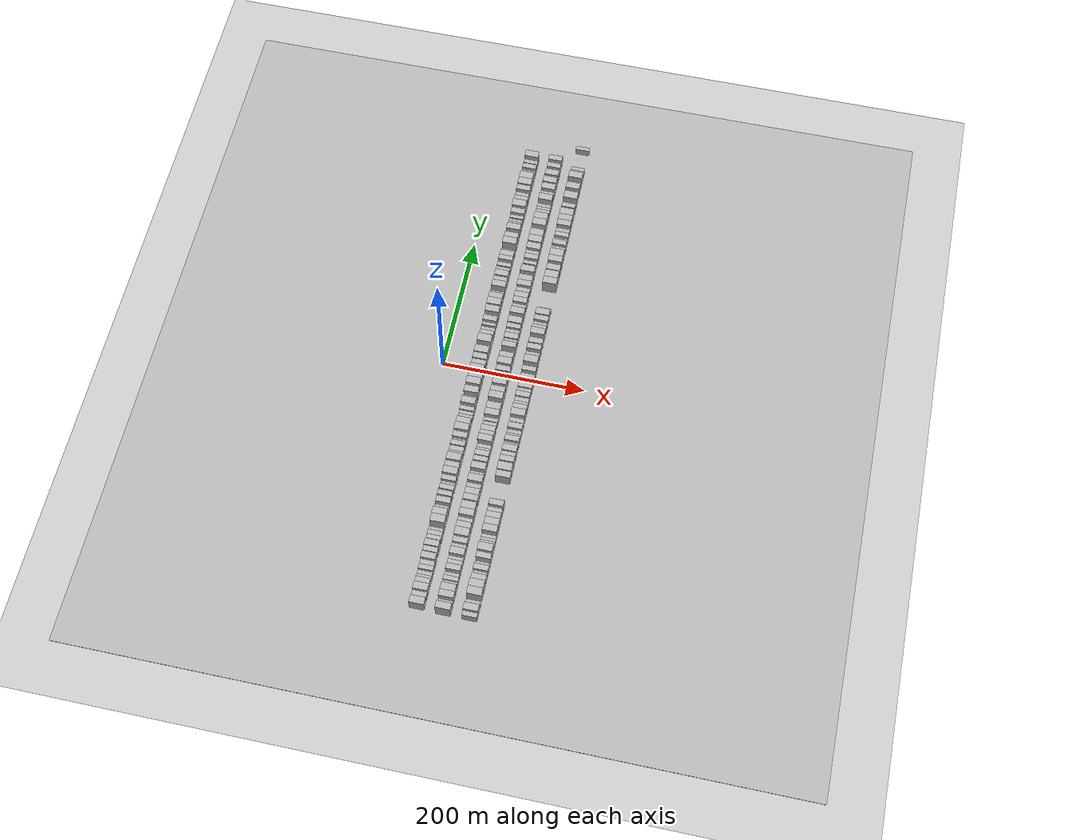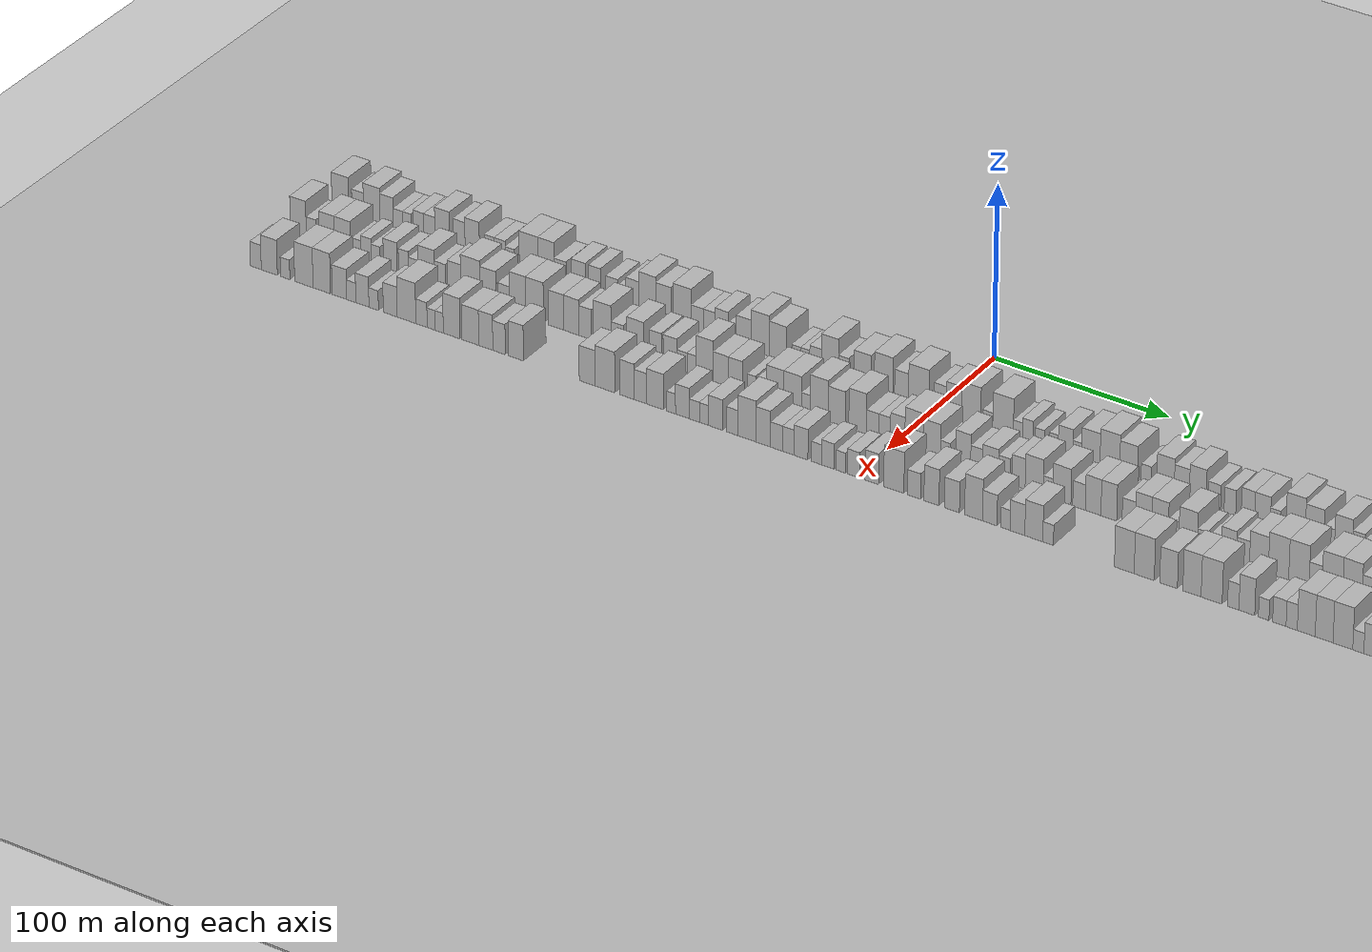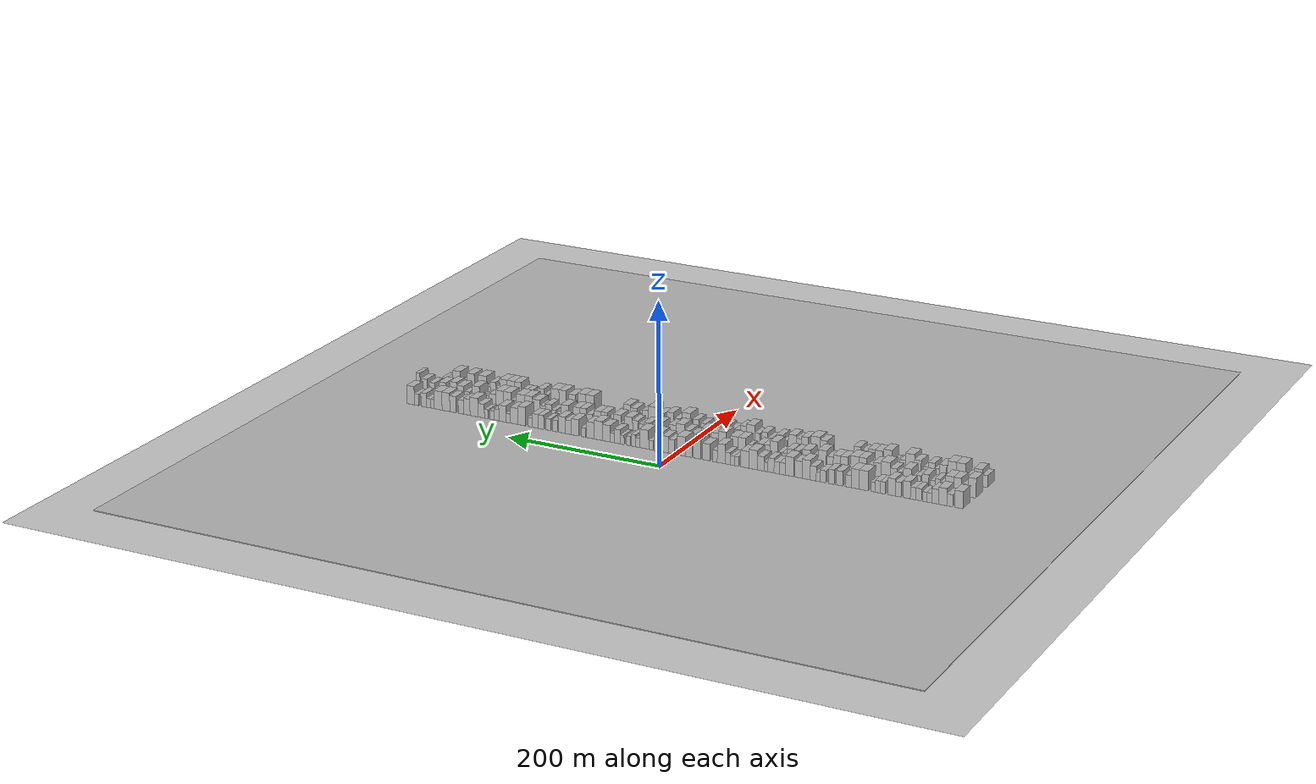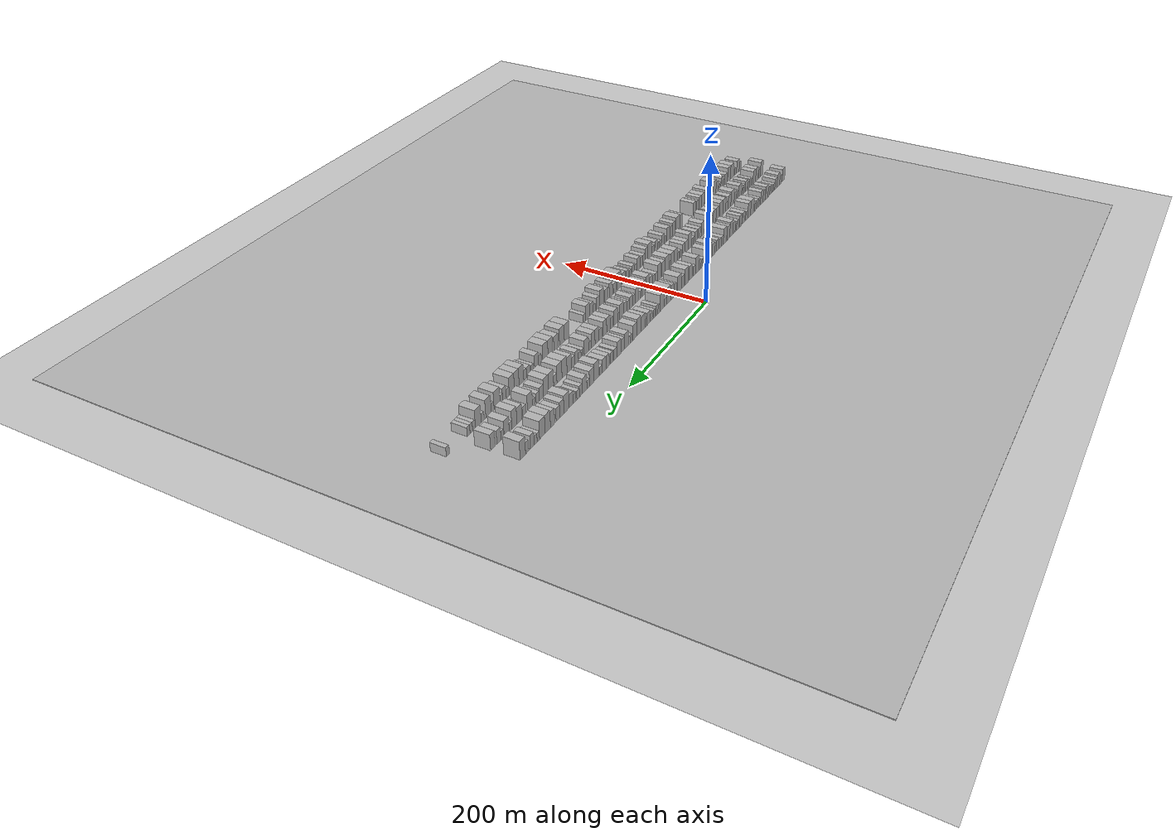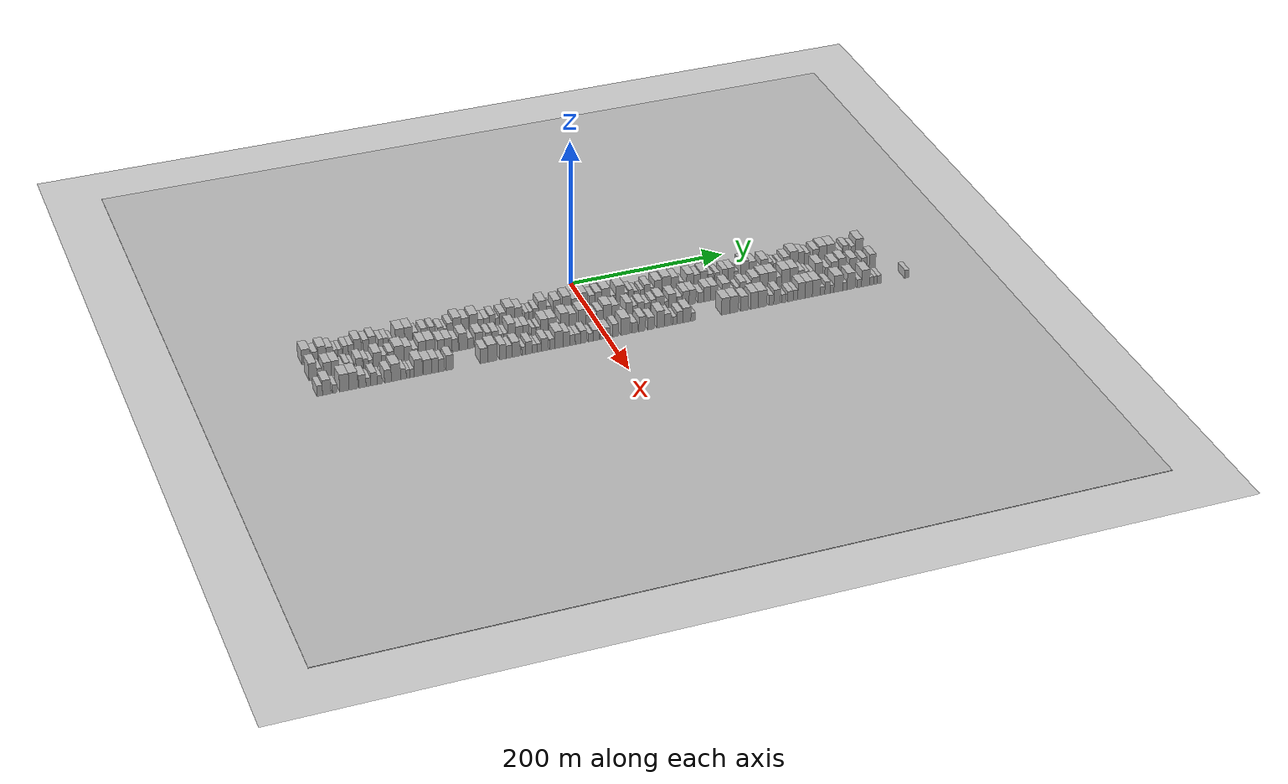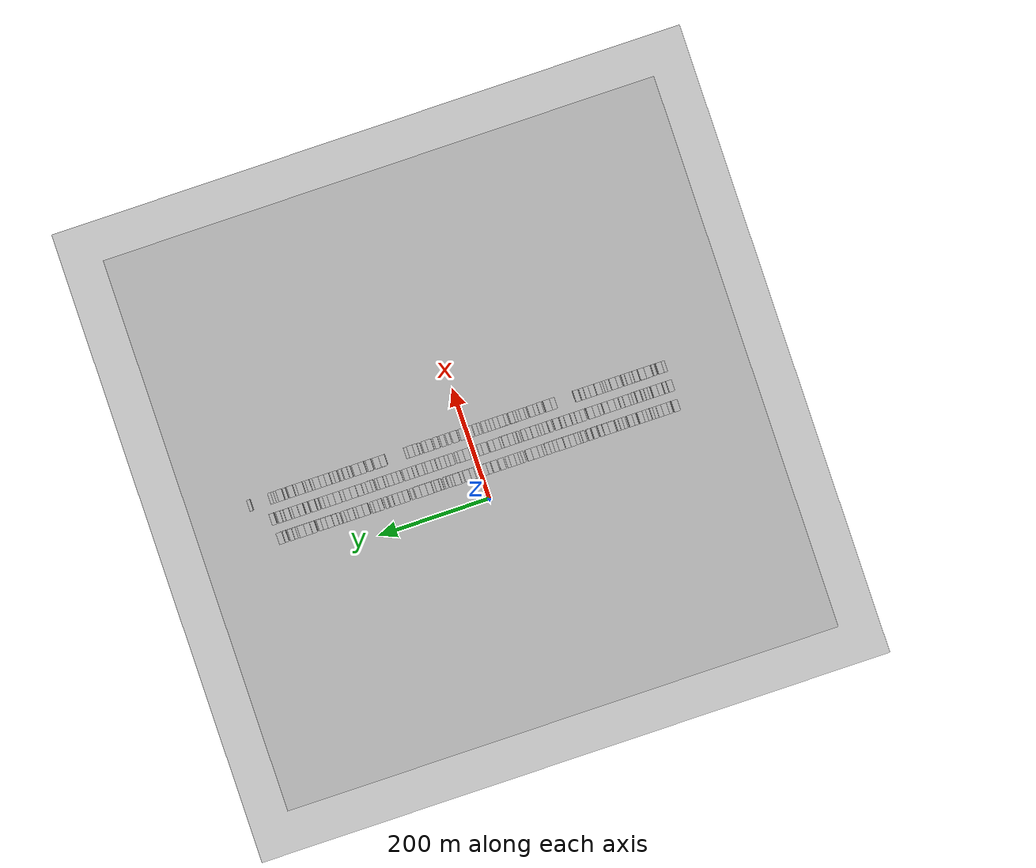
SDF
<?xml version="1.0" encoding="utf-8"?>

<sdf version="1.6">

   <world name="default">

      <gui fullscreen="0">

         <camera name="user_camera">

            <pose>-15 0 4.57585 0 0 0</pose>

            <view_controller>orbit</view_controller>

         </camera>

      </gui>

      <scene>

         <sky>

           <clouds>

             <speed>12</speed>

           </clouds>

         </sky>

         <ambient>0.4 0.4 0.4 1</ambient>

         <background>0.7 0.7 0.7 1</background>

         <shadows>1</shadows>

      </scene>

      <gravity>0 0 -9.8066</gravity>

      <magnetic_field>6e-06 2.3e-05 -4.2e-05</magnetic_field>

      <physics default="0" name="default_physics" type="ode">

         <ode>

            <solver>

               <type>quick</type>

               <iters>10</iters>

               <sor>1.0</sor>

               <use_dynamic_moi_rescaling>0</use_dynamic_moi_rescaling>

            </solver>

            <constraints>

               <cfm>0</cfm>

               <erp>0.2</erp>

               <contact_max_correcting_vel>100</contact_max_correcting_vel>

               <contact_surface_layer>0.001</contact_surface_layer>

            </constraints>

         </ode>

         <max_step_size>0.004</max_step_size>

         <real_time_factor>1</real_time_factor>

         <real_time_update_rate>250</real_time_update_rate>

      </physics>

      <light name="sun" type="directional">

         <cast_shadows>1</cast_shadows>

         <pose>0 0 10 0 0 0</pose>

         <diffuse>0.8 0.8 0.8 1</diffuse>

         <specular>0.2 0.2 0.2 1</specular>

         <attenuation>

            <range>1000</range>

            <constant>0.9</constant>

            <linear>0.01</linear>

            <quadratic>0.001</quadratic>

         </attenuation>

         <direction>-0.5 0.1 -0.9</direction>

      </light>

      <include>

         <name>ground_plane_1</name>

         <uri>model://HANNAS_ground_plane</uri>

         <pose>0 0 0  0 0 0</pose>

      </include>

      <include>

         <name>ground_plane_2</name>

         <uri>model://HANNAS_ground_plane</uri>

         <pose>100 0 0  0 0 0</pose>

      </include>

      <model name="building_1">

         <static>1</static>

         <pose frame="">50.0000 -353.7847 0 0.000000 0.000000 0.000000</pose>

         <link name="link">

            <pose frame="">0 0 10.50 0 0 0</pose>

            <collision name="collision">

               <geometry>

                  <box>

                     <size>20.0000 10.4306 21.0000</size>

                  </box>

               </geometry>

               <max_contacts>10</max_contacts>

               <surface>

                  <contact>

                     <ode/>

                  </contact>

                  <bounce/>

                  <friction>

                     <torsional>

                        <ode/>

                     </torsional>

                     <ode/>

                  </friction>

               </surface>

            </collision>

            <visual name="visual">

               <cast_shadows>0</cast_shadows>

               <geometry>

                  <box>

                     <size>20.0000 10.4306 21.0000</size>

                  </box>

               </geometry>

               <material>

                  <script>

                     <uri>model://HANNAS_wall/materials/scripts</uri>

                     <uri>model://HANNAS_wall/materials/textures</uri>

                     <name>vrc/HANNAS_wall</name>

                  </script>

               </material>

            </visual>

            <self_collide>0</self_collide>

            <enable_wind>0</enable_wind>

            <kinematic>0</kinematic>

         </link>

      </model>

      <model name="building_2">

         <static>1</static>

         <pose frame="">50.0000 -342.9612 0 0.000000 0.000000 0.000000</pose>

         <link name="link">

            <pose frame="">0 0 7.50 0 0 0</pose>

            <collision name="collision">

               <geometry>

                  <box>

                     <size>20.0000 7.2164 15.0000</size>

                  </box>

               </geometry>

               <max_contacts>10</max_contacts>

               <surface>

                  <contact>

                     <ode/>

                  </contact>

                  <bounce/>

                  <friction>

                     <torsional>

                        <ode/>

                     </torsional>

                     <ode/>

                  </friction>

               </surface>

            </collision>

            <visual name="visual">

               <cast_shadows>0</cast_shadows>

               <geometry>

                  <box>

                     <size>20.0000 7.2164 15.0000</size>

                  </box>

               </geometry>

               <material>

                  <script>

                     <uri>model://HANNAS_wall/materials/scripts</uri>

                     <uri>model://HANNAS_wall/materials/textures</uri>

                     <name>vrc/HANNAS_wall</name>

                  </script>

               </material>

            </visual>

            <self_collide>0</self_collide>

            <enable_wind>0</enable_wind>

            <kinematic>0</kinematic>

         </link>

      </model>

      <model name="building_3">

         <static>1</static>

         <pose frame="">50.0000 -334.2786 0 0.000000 0.000000 0.000000</pose>

         <link name="link">

            <pose frame="">0 0 10.50 0 0 0</pose>

            <collision name="collision">

               <geometry>

                  <box>

                     <size>20.0000 10.1488 21.0000</size>

                  </box>

               </geometry>

               <max_contacts>10</max_contacts>

               <surface>

                  <contact>

                     <ode/>

                  </contact>

                  <bounce/>

                  <friction>

                     <torsional>

                        <ode/>

                     </torsional>

                     <ode/>

                  </friction>

               </surface>

            </collision>

            <visual name="visual">

               <cast_shadows>0</cast_shadows>

               <geometry>

                  <box>

                     <size>20.0000 10.1488 21.0000</size>

                  </box>

               </geometry>

               <material>

                  <script>

                     <uri>model://HANNAS_wall/materials/scripts</uri>

                     <uri>model://HANNAS_wall/materials/textures</uri>

                     <name>vrc/HANNAS_wall</name>

                  </script>

               </material>

            </visual>

            <self_collide>0</self_collide>

            <enable_wind>0</enable_wind>

            <kinematic>0</kinematic>

         </link>

      </model>

      <model name="building_4">

         <static>1</static>

         <pose frame="">50.0000 -325.1051 0 0.000000 0.000000 0.000000</pose>

         <link name="link">

            <pose frame="">0 0 9.00 0 0 0</pose>

            <collision name="collision">

               <geometry>

                  <box>

                     <size>20.0000 8.1981 18.0000</size>

                  </box>

               </geometry>

               <max_contacts>10</max_contacts>

               <surface>

                  <contact>

                     <ode/>

                  </contact>

                  <bounce/>

                  <friction>

                     <torsional>

                        <ode/>

                     </torsional>

                     <ode/>

                  </friction>

               </surface>

            </collision>

            <visual name="visual">

               <cast_shadows>0</cast_shadows>

               <geometry>

                  <box>

                     <size>20.0000 8.1981 18.0000</size>

                  </box>

               </geometry>

               <material>

                  <script>

                     <uri>model://HANNAS_wall/materials/scripts</uri>

                     <uri>model://HANNAS_wall/materials/textures</uri>

                     <name>vrc/HANNAS_wall</name>

                  </script>

               </material>

            </visual>

            <self_collide>0</self_collide>

            <enable_wind>0</enable_wind>

            <kinematic>0</kinematic>

         </link>

      </model>

      <model name="building_5">

         <static>1</static>

         <pose frame="">50.0000 -318.0241 0 0.000000 0.000000 0.000000</pose>

         <link name="link">

            <pose frame="">0 0 6.00 0 0 0</pose>

            <collision name="collision">

               <geometry>

                  <box>

                     <size>20.0000 5.9638 12.0000</size>

                  </box>

               </geometry>

               <max_contacts>10</max_contacts>

               <surface>

                  <contact>

                     <ode/>

                  </contact>

                  <bounce/>

                  <friction>

                     <torsional>

                        <ode/>

                     </torsional>

                     <ode/>

                  </friction>

               </surface>

            </collision>

            <visual name="visual">

               <cast_shadows>0</cast_shadows>

               <geometry>

                  <box>

                     <size>20.0000 5.9638 12.0000</size>

                  </box>

               </geometry>

               <material>

                  <script>

                     <uri>model://HANNAS_wall/materials/scripts</uri>

                     <uri>model://HANNAS_wall/materials/textures</uri>

                     <name>vrc/HANNAS_wall</name>

                  </script>

               </material>

            </visual>

            <self_collide>0</self_collide>

            <enable_wind>0</enable_wind>

            <kinematic>0</kinematic>

         </link>

      </model>

      <model name="building_6">

         <static>1</static>

         <pose frame="">50.0000 -312.4131 0 0.000000 0.000000 0.000000</pose>

         <link name="link">

            <pose frame="">0 0 6.00 0 0 0</pose>

            <collision name="collision">

               <geometry>

                  <box>

                     <size>20.0000 5.2583 12.0000</size>

                  </box>

               </geometry>

               <max_contacts>10</max_contacts>

               <surface>

                  <contact>

                     <ode/>

                  </contact>

                  <bounce/>

                  <friction>

                     <torsional>

                        <ode/>

                     </torsional>

                     <ode/>

                  </friction>

               </surface>

            </collision>

            <visual name="visual">

               <cast_shadows>0</cast_shadows>

               <geometry>

                  <box>

                     <size>20.0000 5.2583 12.0000</size>

                  </box>

               </geometry>

               <material>

                  <script>

                     <uri>model://HANNAS_wall/materials/scripts</uri>

                     <uri>model://HANNAS_wall/materials/textures</uri>

                     <name>vrc/HANNAS_wall</name>

                  </script>

               </material>

            </visual>

            <self_collide>0</self_collide>

            <enable_wind>0</enable_wind>

            <kinematic>0</kinematic>

         </link>

      </model>

      <model name="building_7">

         <static>1</static>

         <pose frame="">50.0000 -305.4140 0 0.000000 0.000000 0.000000</pose>

         <link name="link">

            <pose frame="">0 0 7.50 0 0 0</pose>

            <collision name="collision">

               <geometry>

                  <box>

                     <size>20.0000 6.7399 15.0000</size>

                  </box>

               </geometry>

               <max_contacts>10</max_contacts>

               <surface>

                  <contact>

                     <ode/>

                  </contact>

                  <bounce/>

                  <friction>

                     <torsional>

                        <ode/>

                     </torsional>

                     <ode/>

                  </friction>

               </surface>

            </collision>

            <visual name="visual">

               <cast_shadows>0</cast_shadows>

               <geometry>

                  <box>

                     <size>20.0000 6.7399 15.0000</size>

                  </box>

               </geometry>

               <material>

                  <script>

                     <uri>model://HANNAS_wall/materials/scripts</uri>

                     <uri>model://HANNAS_wall/materials/textures</uri>

                     <name>vrc/HANNAS_wall</name>

                  </script>

               </material>

            </visual>

            <self_collide>0</self_collide>

            <enable_wind>0</enable_wind>

            <kinematic>0</kinematic>

         </link>

      </model>

      <model name="building_8">

         <static>1</static>

         <pose frame="">50.0000 -298.6672 0 0.000000 0.000000 0.000000</pose>

         <link name="link">

            <pose frame="">0 0 7.50 0 0 0</pose>

            <collision name="collision">

               <geometry>

                  <box>

                     <size>20.0000 6.7537 15.0000</size>

                  </box>

               </geometry>

               <max_contacts>10</max_contacts>

               <surface>

                  <contact>

                     <ode/>

                  </contact>

                  <bounce/>

                  <friction>

                     <torsional>

                        <ode/>

                     </torsional>

                     <ode/>

                  </friction>

               </surface>

            </collision>

            <visual name="visual">

               <cast_shadows>0</cast_shadows>

               <geometry>

                  <box>

                     <size>20.0000 6.7537 15.0000</size>

                  </box>

               </geometry>

               <material>

                  <script>

                     <uri>model://HANNAS_wall/materials/scripts</uri>

                     <uri>model://HANNAS_wall/materials/textures</uri>

                     <name>vrc/HANNAS_wall</name>

                  </script>

               </material>

            </visual>

            <self_collide>0</self_collide>

            <enable_wind>0</enable_wind>

            <kinematic>0</kinematic>

         </link>

      </model>

      <model name="building_9">

         <static>1</static>

         <pose frame="">50.0000 -290.7151 0 0.000000 0.000000 0.000000</pose>

         <link name="link">

            <pose frame="">0 0 10.50 0 0 0</pose>

            <collision name="collision">

               <geometry>

                  <box>

                     <size>20.0000 9.1503 21.0000</size>

                  </box>

               </geometry>

               <max_contacts>10</max_contacts>

               <surface>

                  <contact>

                     <ode/>

                  </contact>

                  <bounce/>

                  <friction>

                     <torsional>

                        <ode/>

                     </torsional>

                     <ode/>

                  </friction>

               </surface>

            </collision>

            <visual name="visual">

               <cast_shadows>0</cast_shadows>

               <geometry>

                  <box>

                     <size>20.0000 9.1503 21.0000</size>

                  </box>

               </geometry>

               <material>

                  <script>

                     <uri>model://HANNAS_wall/materials/scripts</uri>

                     <uri>model://HANNAS_wall/materials/textures</uri>

                     <name>vrc/HANNAS_wall</name>

                  </script>

               </material>

            </visual>

            <self_collide>0</self_collide>

            <enable_wind>0</enable_wind>

            <kinematic>0</kinematic>

         </link>

      </model>

      <model name="building_10">

         <static>1</static>

         <pose frame="">50.0000 -280.4704 0 0.000000 0.000000 0.000000</pose>

         <link name="link">

            <pose frame="">0 0 9.00 0 0 0</pose>

            <collision name="collision">

               <geometry>

                  <box>

                     <size>20.0000 7.3392 18.0000</size>

                  </box>

               </geometry>

               <max_contacts>10</max_contacts>

               <surface>

                  <contact>

                     <ode/>

                  </contact>

                  <bounce/>

                  <friction>

                     <torsional>

                        <ode/>

                     </torsional>

                     <ode/>

                  </friction>

               </surface>

            </collision>

            <visual name="visual">

               <cast_shadows>0</cast_shadows>

               <geometry>

                  <box>

                     <size>20.0000 7.3392 18.0000</size>

                  </box>

               </geometry>

               <material>

                  <script>

                     <uri>model://HANNAS_wall/materials/scripts</uri>

                     <uri>model://HANNAS_wall/materials/textures</uri>

                     <name>vrc/HANNAS_wall</name>

                  </script>

               </material>

            </visual>

            <self_collide>0</self_collide>

            <enable_wind>0</enable_wind>

            <kinematic>0</kinematic>

         </link>

      </model>

      <model name="building_11">

         <static>1</static>

         <pose frame="">50.0000 -272.4009 0 0.000000 0.000000 0.000000</pose>

         <link name="link">

            <pose frame="">0 0 10.50 0 0 0</pose>

            <collision name="collision">

               <geometry>

                  <box>

                     <size>20.0000 8.7998 21.0000</size>

                  </box>

               </geometry>

               <max_contacts>10</max_contacts>

               <surface>

                  <contact>

                     <ode/>

                  </contact>

                  <bounce/>

                  <friction>

                     <torsional>

                        <ode/>

                     </torsional>

                     <ode/>

                  </friction>

               </surface>

            </collision>

            <visual name="visual">

               <cast_shadows>0</cast_shadows>

               <geometry>

                  <box>

                     <size>20.0000 8.7998 21.0000</size>

                  </box>

               </geometry>

               <material>

                  <script>

                     <uri>model://HANNAS_wall/materials/scripts</uri>

                     <uri>model://HANNAS_wall/materials/textures</uri>

                     <name>vrc/HANNAS_wall</name>

                  </script>

               </material>

            </visual>

            <self_collide>0</self_collide>

            <enable_wind>0</enable_wind>

            <kinematic>0</kinematic>

         </link>

      </model>

      <model name="building_12">

         <static>1</static>

         <pose frame="">50.0000 -261.9339 0 0.000000 0.000000 0.000000</pose>

         <link name="link">

            <pose frame="">0 0 7.50 0 0 0</pose>

            <collision name="collision">

               <geometry>

                  <box>

                     <size>20.0000 6.1342 15.0000</size>

                  </box>

               </geometry>

               <max_contacts>10</max_contacts>

               <surface>

                  <contact>

                     <ode/>

                  </contact>

                  <bounce/>

                  <friction>

                     <torsional>

                        <ode/>

                     </torsional>

                     <ode/>

                  </friction>

               </surface>

            </collision>

            <visual name="visual">

               <cast_shadows>0</cast_shadows>

               <geometry>

                  <box>

                     <size>20.0000 6.1342 15.0000</size>

                  </box>

               </geometry>

               <material>

                  <script>

                     <uri>model://HANNAS_wall/materials/scripts</uri>

                     <uri>model://HANNAS_wall/materials/textures</uri>

                     <name>vrc/HANNAS_wall</name>

                  </script>

               </material>

            </visual>

            <self_collide>0</self_collide>

            <enable_wind>0</enable_wind>

            <kinematic>0</kinematic>

         </link>

      </model>

      <model name="building_13">

         <static>1</static>

         <pose frame="">50.0000 -255.5714 0 0.000000 0.000000 0.000000</pose>

         <link name="link">

            <pose frame="">0 0 7.50 0 0 0</pose>

            <collision name="collision">

               <geometry>

                  <box>

                     <size>20.0000 6.5909 15.0000</size>

                  </box>

               </geometry>

               <max_contacts>10</max_contacts>

               <surface>

                  <contact>

                     <ode/>

                  </contact>

                  <bounce/>

                  <friction>

                     <torsional>

                        <ode/>

                     </torsional>

                     <ode/>

                  </friction>

               </surface>

            </collision>

            <visual name="visual">

               <cast_shadows>0</cast_shadows>

               <geometry>

                  <box>

                     <size>20.0000 6.5909 15.0000</size>

                  </box>

               </geometry>

               <material>

                  <script>

                     <uri>model://HANNAS_wall/materials/scripts</uri>

                     <uri>model://HANNAS_wall/materials/textures</uri>

                     <name>vrc/HANNAS_wall</name>

                  </script>

               </material>

            </visual>

            <self_collide>0</self_collide>

            <enable_wind>0</enable_wind>

            <kinematic>0</kinematic>

         </link>

      </model>

      <model name="building_14">

         <static>1</static>

         <pose frame="">50.0000 -249.4801 0 0.000000 0.000000 0.000000</pose>

         <link name="link">

            <pose frame="">0 0 6.00 0 0 0</pose>

            <collision name="collision">

               <geometry>

                  <box>

                     <size>20.0000 5.5918 12.0000</size>

                  </box>

               </geometry>

               <max_contacts>10</max_contacts>

               <surface>

                  <contact>

                     <ode/>

                  </contact>

                  <bounce/>

                  <friction>

                     <torsional>

                        <ode/>

                     </torsional>

                     <ode/>

                  </friction>

               </surface>

            </collision>

            <visual name="visual">

               <cast_shadows>0</cast_shadows>

               <geometry>

                  <box>

                     <size>20.0000 5.5918 12.0000</size>

                  </box>

               </geometry>

               <material>

                  <script>

                     <uri>model://HANNAS_wall/materials/scripts</uri>

                     <uri>model://HANNAS_wall/materials/textures</uri>

                     <name>vrc/HANNAS_wall</name>

                  </script>

               </material>

            </visual>

            <self_collide>0</self_collide>

            <enable_wind>0</enable_wind>

            <kinematic>0</kinematic>

         </link>

      </model>

      <model name="building_15">

         <static>1</static>

         <pose frame="">50.0000 -238.0136 0 0.000000 0.000000 0.000000</pose>

         <link name="link">

            <pose frame="">0 0 12.00 0 0 0</pose>

            <collision name="collision">

               <geometry>

                  <box>

                     <size>20.0000 11.3412 24.0000</size>

                  </box>

               </geometry>

               <max_contacts>10</max_contacts>

               <surface>

                  <contact>

                     <ode/>

                  </contact>

                  <bounce/>

                  <friction>

                     <torsional>

                        <ode/>

                     </torsional>

                     <ode/>

                  </friction>

               </surface>

            </collision>

            <visual name="visual">

               <cast_shadows>0</cast_shadows>

               <geometry>

                  <box>

                     <size>20.0000 11.3412 24.0000</size>

                  </box>

               </geometry>

               <material>

                  <script>

                     <uri>model://HANNAS_wall/materials/scripts</uri>

                     <uri>model://HANNAS_wall/materials/textures</uri>

                     <name>vrc/HANNAS_wall</name>

                  </script>

               </material>

            </visual>

            <self_collide>0</self_collide>

            <enable_wind>0</enable_wind>

            <kinematic>0</kinematic>

         </link>

      </model>

      <model name="building_16">

         <static>1</static>

         <pose frame="">50.0000 -227.4978 0 0.000000 0.000000 0.000000</pose>

         <link name="link">

            <pose frame="">0 0 12.00 0 0 0</pose>

            <collision name="collision">

               <geometry>

                  <box>

                     <size>20.0000 9.6904 24.0000</size>

                  </box>

               </geometry>

               <max_contacts>10</max_contacts>

               <surface>

                  <contact>

                     <ode/>

                  </contact>

                  <bounce/>

                  <friction>

                     <torsional>

                        <ode/>

                     </torsional>

                     <ode/>

                  </friction>

               </surface>

            </collision>

            <visual name="visual">

               <cast_shadows>0</cast_shadows>

               <geometry>

                  <box>

                     <size>20.0000 9.6904 24.0000</size>

                  </box>

               </geometry>

               <material>

                  <script>

                     <uri>model://HANNAS_wall/materials/scripts</uri>

                     <uri>model://HANNAS_wall/materials/textures</uri>

                     <name>vrc/HANNAS_wall</name>

                  </script>

               </material>

            </visual>

            <self_collide>0</self_collide>

            <enable_wind>0</enable_wind>

            <kinematic>0</kinematic>

         </link>

      </model>

      <model name="building_17">

         <static>1</static>

         <pose frame="">50.0000 -218.9621 0 0.000000 0.000000 0.000000</pose>

         <link name="link">

            <pose frame="">0 0 7.50 0 0 0</pose>

            <collision name="collision">

               <geometry>

                  <box>

                     <size>20.0000 7.3808 15.0000</size>

                  </box>

               </geometry>

               <max_contacts>10</max_contacts>

               <surface>

                  <contact>

                     <ode/>

                  </contact>

                  <bounce/>

                  <friction>

                     <torsional>

                        <ode/>

                     </torsional>

                     <ode/>

                  </friction>

               </surface>

            </collision>

            <visual name="visual">

               <cast_shadows>0</cast_shadows>

               <geometry>

                  <box>

                     <size>20.0000 7.3808 15.0000</size>

                  </box>

               </geometry>

               <material>

                  <script>

                     <uri>model://HANNAS_wall/materials/scripts</uri>

                     <uri>model://HANNAS_wall/materials/textures</uri>

                     <name>vrc/HANNAS_wall</name>

                  </script>

               </material>

            </visual>

            <self_collide>0</self_collide>

            <enable_wind>0</enable_wind>

            <kinematic>0</kinematic>

         </link>

      </model>

      <model name="building_18">

         <static>1</static>

         <pose frame="">50.0000 -207.9963 0 0.000000 0.000000 0.000000</pose>

         <link name="link">

            <pose frame="">0 0 9.00 0 0 0</pose>

            <collision name="collision">

               <geometry>

                  <box>

                     <size>20.0000 8.5509 18.0000</size>

                  </box>

               </geometry>

               <max_contacts>10</max_contacts>

               <surface>

                  <contact>

                     <ode/>

                  </contact>

                  <bounce/>

                  <friction>

                     <torsional>

                        <ode/>

                     </torsional>

                     <ode/>

                  </friction>

               </surface>

            </collision>

            <visual name="visual">

               <cast_shadows>0</cast_shadows>

               <geometry>

                  <box>

                     <size>20.0000 8.5509 18.0000</size>

                  </box>

               </geometry>

               <material>

                  <script>

                     <uri>model://HANNAS_wall/materials/scripts</uri>

                     <uri>model://HANNAS_wall/materials/textures</uri>

                     <name>vrc/HANNAS_wall</name>

                  </script>

               </material>

            </visual>

            <self_collide>0</self_collide>

            <enable_wind>0</enable_wind>

            <kinematic>0</kinematic>

         </link>

      </model>

      <model name="building_19">

         <static>1</static>

         <pose frame="">50.0000 -198.0948 0 0.000000 0.000000 0.000000</pose>

         <link name="link">

            <pose frame="">0 0 9.00 0 0 0</pose>

            <collision name="collision">

               <geometry>

                  <box>

                     <size>20.0000 7.2520 18.0000</size>

                  </box>

               </geometry>

               <max_contacts>10</max_contacts>

               <surface>

                  <contact>

                     <ode/>

                  </contact>

                  <bounce/>

                  <friction>

                     <torsional>

                        <ode/>

                     </torsional>

                     <ode/>

                  </friction>

               </surface>

            </collision>

            <visual name="visual">

               <cast_shadows>0</cast_shadows>

               <geometry>

                  <box>

                     <size>20.0000 7.2520 18.0000</size>

                  </box>

               </geometry>

               <material>

                  <script>

                     <uri>model://HANNAS_wall/materials/scripts</uri>

                     <uri>model://HANNAS_wall/materials/textures</uri>

                     <name>vrc/HANNAS_wall</name>

                  </script>

               </material>

            </visual>

            <self_collide>0</self_collide>

            <enable_wind>0</enable_wind>

            <kinematic>0</kinematic>

         </link>

      </model>

      <model name="building_20">

         <static>1</static>

         <pose frame="">50.0000 -187.8145 0 0.000000 0.000000 0.000000</pose>

         <link name="link">

            <pose frame="">0 0 7.50 0 0 0</pose>

            <collision name="collision">

               <geometry>

                  <box>

                     <size>20.0000 7.3087 15.0000</size>

                  </box>

               </geometry>

               <max_contacts>10</max_contacts>

               <surface>

                  <contact>

                     <ode/>

                  </contact>

                  <bounce/>

                  <friction>

                     <torsional>

                        <ode/>

                     </torsional>

                     <ode/>

                  </friction>

               </surface>

            </collision>

            <visual name="visual">

               <cast_shadows>0</cast_shadows>

               <geometry>

                  <box>

                     <size>20.0000 7.3087 15.0000</size>

                  </box>

               </geometry>

               <material>

                  <script>

                     <uri>model://HANNAS_wall/materials/scripts</uri>

                     <uri>model://HANNAS_wall/materials/textures</uri>

                     <name>vrc/HANNAS_wall</name>

                  </script>

               </material>

            </visual>

            <self_collide>0</self_collide>

            <enable_wind>0</enable_wind>

            <kinematic>0</kinematic>

         </link>

      </model>

      <model name="building_21">

         <static>1</static>

         <pose frame="">50.0000 -181.7357 0 0.000000 0.000000 0.000000</pose>

         <link name="link">

            <pose frame="">0 0 6.00 0 0 0</pose>

            <collision name="collision">

               <geometry>

                  <box>

                     <size>20.0000 4.8490 12.0000</size>

                  </box>

               </geometry>

               <max_contacts>10</max_contacts>

               <surface>

                  <contact>

                     <ode/>

                  </contact>

                  <bounce/>

                  <friction>

                     <torsional>

                        <ode/>

                     </torsional>

                     <ode/>

                  </friction>

               </surface>

            </collision>

            <visual name="visual">

               <cast_shadows>0</cast_shadows>

               <geometry>

                  <box>

                     <size>20.0000 4.8490 12.0000</size>

                  </box>

               </geometry>

               <material>

                  <script>

                     <uri>model://HANNAS_wall/materials/scripts</uri>

                     <uri>model://HANNAS_wall/materials/textures</uri>

                     <name>vrc/HANNAS_wall</name>

                  </script>

               </material>

            </visual>

            <self_collide>0</self_collide>

            <enable_wind>0</enable_wind>

            <kinematic>0</kinematic>

         </link>

      </model>

      <model name="building_22">

         <static>1</static>

         <pose frame="">50.0000 -175.5399 0 0.000000 0.000000 0.000000</pose>

         <link name="link">

            <pose frame="">0 0 9.00 0 0 0</pose>

            <collision name="collision">

               <geometry>

                  <box>

                     <size>20.0000 7.5427 18.0000</size>

                  </box>

               </geometry>

               <max_contacts>10</max_contacts>

               <surface>

                  <contact>

                     <ode/>

                  </contact>

                  <bounce/>

                  <friction>

                     <torsional>

                        <ode/>

                     </torsional>

                     <ode/>

                  </friction>

               </surface>

            </collision>

            <visual name="visual">

               <cast_shadows>0</cast_shadows>

               <geometry>

                  <box>

                     <size>20.0000 7.5427 18.0000</size>

                  </box>

               </geometry>

               <material>

                  <script>

                     <uri>model://HANNAS_wall/materials/scripts</uri>

                     <uri>model://HANNAS_wall/materials/textures</uri>

                     <name>vrc/HANNAS_wall</name>

                  </script>

               </material>

            </visual>

            <self_collide>0</self_collide>

            <enable_wind>0</enable_wind>

            <kinematic>0</kinematic>

         </link>

      </model>

      <model name="building_23">

         <static>1</static>

         <pose frame="">50.0000 -166.6591 0 0.000000 0.000000 0.000000</pose>

         <link name="link">

            <pose frame="">0 0 12.00 0 0 0</pose>

            <collision name="collision">

               <geometry>

                  <box>

                     <size>20.0000 10.2189 24.0000</size>

                  </box>

               </geometry>

               <max_contacts>10</max_contacts>

               <surface>

                  <contact>

                     <ode/>

                  </contact>

                  <bounce/>

                  <friction>

                     <torsional>

                        <ode/>

                     </torsional>

                     <ode/>

                  </friction>

               </surface>

            </collision>

            <visual name="visual">

               <cast_shadows>0</cast_shadows>

               <geometry>

                  <box>

                     <size>20.0000 10.2189 24.0000</size>

                  </box>

               </geometry>

               <material>

                  <script>

                     <uri>model://HANNAS_wall/materials/scripts</uri>

                     <uri>model://HANNAS_wall/materials/textures</uri>

                     <name>vrc/HANNAS_wall</name>

                  </script>

               </material>

            </visual>

            <self_collide>0</self_collide>

            <enable_wind>0</enable_wind>

            <kinematic>0</kinematic>

         </link>

      </model>

      <model name="building_24">

         <static>1</static>

         <pose frame="">50.0000 -156.9002 0 0.000000 0.000000 0.000000</pose>

         <link name="link">

            <pose frame="">0 0 10.50 0 0 0</pose>

            <collision name="collision">

               <geometry>

                  <box>

                     <size>20.0000 9.2989 21.0000</size>

                  </box>

               </geometry>

               <max_contacts>10</max_contacts>

               <surface>

                  <contact>

                     <ode/>

                  </contact>

                  <bounce/>

                  <friction>

                     <torsional>

                        <ode/>

                     </torsional>

                     <ode/>

                  </friction>

               </surface>

            </collision>

            <visual name="visual">

               <cast_shadows>0</cast_shadows>

               <geometry>

                  <box>

                     <size>20.0000 9.2989 21.0000</size>

                  </box>

               </geometry>

               <material>

                  <script>

                     <uri>model://HANNAS_wall/materials/scripts</uri>

                     <uri>model://HANNAS_wall/materials/textures</uri>

                     <name>vrc/HANNAS_wall</name>

                  </script>

               </material>

            </visual>

            <self_collide>0</self_collide>

            <enable_wind>0</enable_wind>

            <kinematic>0</kinematic>

         </link>

      </model>

      <model name="building_25">

         <static>1</static>

         <pose frame="">50.0000 -145.7998 0 0.000000 0.000000 0.000000</pose>

         <link name="link">

            <pose frame="">0 0 12.00 0 0 0</pose>

            <collision name="collision">

               <geometry>

                  <box>

                     <size>20.0000 10.9017 24.0000</size>

                  </box>

               </geometry>

               <max_contacts>10</max_contacts>

               <surface>

                  <contact>

                     <ode/>

                  </contact>

                  <bounce/>

                  <friction>

                     <torsional>

                        <ode/>

                     </torsional>

                     <ode/>

                  </friction>

               </surface>

            </collision>

            <visual name="visual">

               <cast_shadows>0</cast_shadows>

               <geometry>

                  <box>

                     <size>20.0000 10.9017 24.0000</size>

                  </box>

               </geometry>

               <material>

                  <script>

                     <uri>model://HANNAS_wall/materials/scripts</uri>

                     <uri>model://HANNAS_wall/materials/textures</uri>

                     <name>vrc/HANNAS_wall</name>

                  </script>

               </material>

            </visual>

            <self_collide>0</self_collide>

            <enable_wind>0</enable_wind>

            <kinematic>0</kinematic>

         </link>

      </model>

      <model name="building_26">

         <static>1</static>

         <pose frame="">50.0000 -136.7652 0 0.000000 0.000000 0.000000</pose>

         <link name="link">

            <pose frame="">0 0 7.50 0 0 0</pose>

            <collision name="collision">

               <geometry>

                  <box>

                     <size>20.0000 7.1675 15.0000</size>

                  </box>

               </geometry>

               <max_contacts>10</max_contacts>

               <surface>

                  <contact>

                     <ode/>

                  </contact>

                  <bounce/>

                  <friction>

                     <torsional>

                        <ode/>

                     </torsional>

                     <ode/>

                  </friction>

               </surface>

            </collision>

            <visual name="visual">

               <cast_shadows>0</cast_shadows>

               <geometry>

                  <box>

                     <size>20.0000 7.1675 15.0000</size>

                  </box>

               </geometry>

               <material>

                  <script>

                     <uri>model://HANNAS_wall/materials/scripts</uri>

                     <uri>model://HANNAS_wall/materials/textures</uri>

                     <name>vrc/HANNAS_wall</name>

                  </script>

               </material>

            </visual>

            <self_collide>0</self_collide>

            <enable_wind>0</enable_wind>

            <kinematic>0</kinematic>

         </link>

      </model>

      <model name="building_27">

         <static>1</static>

         <pose frame="">50.0000 -129.6550 0 0.000000 0.000000 0.000000</pose>

         <link name="link">

            <pose frame="">0 0 7.50 0 0 0</pose>

            <collision name="collision">

               <geometry>

                  <box>

                     <size>20.0000 7.0529 15.0000</size>

                  </box>

               </geometry>

               <max_contacts>10</max_contacts>

               <surface>

                  <contact>

                     <ode/>

                  </contact>

                  <bounce/>

                  <friction>

                     <torsional>

                        <ode/>

                     </torsional>

                     <ode/>

                  </friction>

               </surface>

            </collision>

            <visual name="visual">

               <cast_shadows>0</cast_shadows>

               <geometry>

                  <box>

                     <size>20.0000 7.0529 15.0000</size>

                  </box>

               </geometry>

               <material>

                  <script>

                     <uri>model://HANNAS_wall/materials/scripts</uri>

                     <uri>model://HANNAS_wall/materials/textures</uri>

                     <name>vrc/HANNAS_wall</name>

                  </script>

               </material>

            </visual>

            <self_collide>0</self_collide>

            <enable_wind>0</enable_wind>

            <kinematic>0</kinematic>

         </link>

      </model>

      <model name="building_28">

         <static>1</static>

         <pose frame="">50.0000 -122.3375 0 0.000000 0.000000 0.000000</pose>

         <link name="link">

            <pose frame="">0 0 9.00 0 0 0</pose>

            <collision name="collision">

               <geometry>

                  <box>

                     <size>20.0000 7.5823 18.0000</size>

                  </box>

               </geometry>

               <max_contacts>10</max_contacts>

               <surface>

                  <contact>

                     <ode/>

                  </contact>

                  <bounce/>

                  <friction>

                     <torsional>

                        <ode/>

                     </torsional>

                     <ode/>

                  </friction>

               </surface>

            </collision>

            <visual name="visual">

               <cast_shadows>0</cast_shadows>

               <geometry>

                  <box>

                     <size>20.0000 7.5823 18.0000</size>

                  </box>

               </geometry>

               <material>

                  <script>

                     <uri>model://HANNAS_wall/materials/scripts</uri>

                     <uri>model://HANNAS_wall/materials/textures</uri>

                     <name>vrc/HANNAS_wall</name>

                  </script>

               </material>

            </visual>

            <self_collide>0</self_collide>

            <enable_wind>0</enable_wind>

            <kinematic>0</kinematic>

         </link>

      </model>

      <model name="building_29">

         <static>1</static>

         <pose frame="">50.0000 -116.0699 0 0.000000 0.000000 0.000000</pose>

         <link name="link">

            <pose frame="">0 0 6.00 0 0 0</pose>

            <collision name="collision">

               <geometry>

                  <box>

                     <size>20.0000 4.9528 12.0000</size>

                  </box>

               </geometry>

               <max_contacts>10</max_contacts>

               <surface>

                  <contact>

                     <ode/>

                  </contact>

                  <bounce/>

                  <friction>

                     <torsional>

                        <ode/>

                     </torsional>

                     <ode/>

                  </friction>

               </surface>

            </collision>

            <visual name="visual">

               <cast_shadows>0</cast_shadows>

               <geometry>

                  <box>

                     <size>20.0000 4.9528 12.0000</size>

                  </box>

               </geometry>

               <material>

                  <script>

                     <uri>model://HANNAS_wall/materials/scripts</uri>

                     <uri>model://HANNAS_wall/materials/textures</uri>

                     <name>vrc/HANNAS_wall</name>

                  </script>

               </material>

            </visual>

            <self_collide>0</self_collide>

            <enable_wind>0</enable_wind>

            <kinematic>0</kinematic>

         </link>

      </model>

      <model name="building_30">

         <static>1</static>

         <pose frame="">50.0000 -109.2747 0 0.000000 0.000000 0.000000</pose>

         <link name="link">

            <pose frame="">0 0 9.00 0 0 0</pose>

            <collision name="collision">

               <geometry>

                  <box>

                     <size>20.0000 8.6376 18.0000</size>

                  </box>

               </geometry>

               <max_contacts>10</max_contacts>

               <surface>

                  <contact>

                     <ode/>

                  </contact>

                  <bounce/>

                  <friction>

                     <torsional>

                        <ode/>

                     </torsional>

                     <ode/>

                  </friction>

               </surface>

            </collision>

            <visual name="visual">

               <cast_shadows>0</cast_shadows>

               <geometry>

                  <box>

                     <size>20.0000 8.6376 18.0000</size>

                  </box>

               </geometry>

               <material>

                  <script>

                     <uri>model://HANNAS_wall/materials/scripts</uri>

                     <uri>model://HANNAS_wall/materials/textures</uri>

                     <name>vrc/HANNAS_wall</name>

                  </script>

               </material>

            </visual>

            <self_collide>0</self_collide>

            <enable_wind>0</enable_wind>

            <kinematic>0</kinematic>

         </link>

      </model>

      <model name="building_31">

         <static>1</static>

         <pose frame="">50.0000 -99.5442 0 0.000000 0.000000 0.000000</pose>

         <link name="link">

            <pose frame="">0 0 12.00 0 0 0</pose>

            <collision name="collision">

               <geometry>

                  <box>

                     <size>20.0000 10.8232 24.0000</size>

                  </box>

               </geometry>

               <max_contacts>10</max_contacts>

               <surface>

                  <contact>

                     <ode/>

                  </contact>

                  <bounce/>

                  <friction>

                     <torsional>

                        <ode/>

                     </torsional>

                     <ode/>

                  </friction>

               </surface>

            </collision>

            <visual name="visual">

               <cast_shadows>0</cast_shadows>

               <geometry>

                  <box>

                     <size>20.0000 10.8232 24.0000</size>

                  </box>

               </geometry>

               <material>

                  <script>

                     <uri>model://HANNAS_wall/materials/scripts</uri>

                     <uri>model://HANNAS_wall/materials/textures</uri>

                     <name>vrc/HANNAS_wall</name>

                  </script>

               </material>

            </visual>

            <self_collide>0</self_collide>

            <enable_wind>0</enable_wind>

            <kinematic>0</kinematic>

         </link>

      </model>

      <model name="building_32">

         <static>1</static>

         <pose frame="">50.0000 -89.0748 0 0.000000 0.000000 0.000000</pose>

         <link name="link">

            <pose frame="">0 0 10.50 0 0 0</pose>

            <collision name="collision">

               <geometry>

                  <box>

                     <size>20.0000 10.1156 21.0000</size>

                  </box>

               </geometry>

               <max_contacts>10</max_contacts>

               <surface>

                  <contact>

                     <ode/>

                  </contact>

                  <bounce/>

                  <friction>

                     <torsional>

                        <ode/>

                     </torsional>

                     <ode/>

                  </friction>

               </surface>

            </collision>

            <visual name="visual">

               <cast_shadows>0</cast_shadows>

               <geometry>

                  <box>

                     <size>20.0000 10.1156 21.0000</size>

                  </box>

               </geometry>

               <material>

                  <script>

                     <uri>model://HANNAS_wall/materials/scripts</uri>

                     <uri>model://HANNAS_wall/materials/textures</uri>

                     <name>vrc/HANNAS_wall</name>

                  </script>

               </material>

            </visual>

            <self_collide>0</self_collide>

            <enable_wind>0</enable_wind>

            <kinematic>0</kinematic>

         </link>

      </model>

      <model name="building_33">

         <static>1</static>

         <pose frame="">50.0000 -78.3237 0 0.000000 0.000000 0.000000</pose>

         <link name="link">

            <pose frame="">0 0 6.00 0 0 0</pose>

            <collision name="collision">

               <geometry>

                  <box>

                     <size>20.0000 5.3867 12.0000</size>

                  </box>

               </geometry>

               <max_contacts>10</max_contacts>

               <surface>

                  <contact>

                     <ode/>

                  </contact>

                  <bounce/>

                  <friction>

                     <torsional>

                        <ode/>

                     </torsional>

                     <ode/>

                  </friction>

               </surface>

            </collision>

            <visual name="visual">

               <cast_shadows>0</cast_shadows>

               <geometry>

                  <box>

                     <size>20.0000 5.3867 12.0000</size>

                  </box>

               </geometry>

               <material>

                  <script>

                     <uri>model://HANNAS_wall/materials/scripts</uri>

                     <uri>model://HANNAS_wall/materials/textures</uri>

                     <name>vrc/HANNAS_wall</name>

                  </script>

               </material>

            </visual>

            <self_collide>0</self_collide>

            <enable_wind>0</enable_wind>

            <kinematic>0</kinematic>

         </link>

      </model>

      <model name="building_34">

         <static>1</static>

         <pose frame="">50.0000 -73.0354 0 0.000000 0.000000 0.000000</pose>

         <link name="link">

            <pose frame="">0 0 6.00 0 0 0</pose>

            <collision name="collision">

               <geometry>

                  <box>

                     <size>20.0000 5.1898 12.0000</size>

                  </box>

               </geometry>

               <max_contacts>10</max_contacts>

               <surface>

                  <contact>

                     <ode/>

                  </contact>

                  <bounce/>

                  <friction>

                     <torsional>

                        <ode/>

                     </torsional>

                     <ode/>

                  </friction>

               </surface>

            </collision>

            <visual name="visual">

               <cast_shadows>0</cast_shadows>

               <geometry>

                  <box>

                     <size>20.0000 5.1898 12.0000</size>

                  </box>

               </geometry>

               <material>

                  <script>

                     <uri>model://HANNAS_wall/materials/scripts</uri>

                     <uri>model://HANNAS_wall/materials/textures</uri>

                     <name>vrc/HANNAS_wall</name>

                  </script>

               </material>

            </visual>

            <self_collide>0</self_collide>

            <enable_wind>0</enable_wind>

            <kinematic>0</kinematic>

         </link>

      </model>

      <model name="building_35">

         <static>1</static>

         <pose frame="">50.0000 -67.0628 0 0.000000 0.000000 0.000000</pose>

         <link name="link">

            <pose frame="">0 0 7.50 0 0 0</pose>

            <collision name="collision">

               <geometry>

                  <box>

                     <size>20.0000 6.7553 15.0000</size>

                  </box>

               </geometry>

               <max_contacts>10</max_contacts>

               <surface>

                  <contact>

                     <ode/>

                  </contact>

                  <bounce/>

                  <friction>

                     <torsional>

                        <ode/>

                     </torsional>

                     <ode/>

                  </friction>

               </surface>

            </collision>

            <visual name="visual">

               <cast_shadows>0</cast_shadows>

               <geometry>

                  <box>

                     <size>20.0000 6.7553 15.0000</size>

                  </box>

               </geometry>

               <material>

                  <script>

                     <uri>model://HANNAS_wall/materials/scripts</uri>

                     <uri>model://HANNAS_wall/materials/textures</uri>

                     <name>vrc/HANNAS_wall</name>

                  </script>

               </material>

            </visual>

            <self_collide>0</self_collide>

            <enable_wind>0</enable_wind>

            <kinematic>0</kinematic>

         </link>

      </model>

      <model name="building_36">

         <static>1</static>

         <pose frame="">50.0000 -58.6973 0 0.000000 0.000000 0.000000</pose>

         <link name="link">

            <pose frame="">0 0 12.00 0 0 0</pose>

            <collision name="collision">

               <geometry>

                  <box>

                     <size>20.0000 9.9757 24.0000</size>

                  </box>

               </geometry>

               <max_contacts>10</max_contacts>

               <surface>

                  <contact>

                     <ode/>

                  </contact>

                  <bounce/>

                  <friction>

                     <torsional>

                        <ode/>

                     </torsional>

                     <ode/>

                  </friction>

               </surface>

            </collision>

            <visual name="visual">

               <cast_shadows>0</cast_shadows>

               <geometry>

                  <box>

                     <size>20.0000 9.9757 24.0000</size>

                  </box>

               </geometry>

               <material>

                  <script>

                     <uri>model://HANNAS_wall/materials/scripts</uri>

                     <uri>model://HANNAS_wall/materials/textures</uri>

                     <name>vrc/HANNAS_wall</name>

                  </script>

               </material>

            </visual>

            <self_collide>0</self_collide>

            <enable_wind>0</enable_wind>

            <kinematic>0</kinematic>

         </link>

      </model>

      <model name="building_37">

         <static>1</static>

         <pose frame="">50.0000 -50.6747 0 0.000000 0.000000 0.000000</pose>

         <link name="link">

            <pose frame="">0 0 7.50 0 0 0</pose>

            <collision name="collision">

               <geometry>

                  <box>

                     <size>20.0000 6.0696 15.0000</size>

                  </box>

               </geometry>

               <max_contacts>10</max_contacts>

               <surface>

                  <contact>

                     <ode/>

                  </contact>

                  <bounce/>

                  <friction>

                     <torsional>

                        <ode/>

                     </torsional>

                     <ode/>

                  </friction>

               </surface>

            </collision>

            <visual name="visual">

               <cast_shadows>0</cast_shadows>

               <geometry>

                  <box>

                     <size>20.0000 6.0696 15.0000</size>

                  </box>

               </geometry>

               <material>

                  <script>

                     <uri>model://HANNAS_wall/materials/scripts</uri>

                     <uri>model://HANNAS_wall/materials/textures</uri>

                     <name>vrc/HANNAS_wall</name>

                  </script>

               </material>

            </visual>

            <self_collide>0</self_collide>

            <enable_wind>0</enable_wind>

            <kinematic>0</kinematic>

         </link>

      </model>

      <model name="building_38">

         <static>1</static>

         <pose frame="">50.0000 -39.7006 0 0.000000 0.000000 0.000000</pose>

         <link name="link">

            <pose frame="">0 0 10.50 0 0 0</pose>

            <collision name="collision">

               <geometry>

                  <box>

                     <size>20.0000 9.8786 21.0000</size>

                  </box>

               </geometry>

               <max_contacts>10</max_contacts>

               <surface>

                  <contact>

                     <ode/>

                  </contact>

                  <bounce/>

                  <friction>

                     <torsional>

                        <ode/>

                     </torsional>

                     <ode/>

                  </friction>

               </surface>

            </collision>

            <visual name="visual">

               <cast_shadows>0</cast_shadows>

               <geometry>

                  <box>

                     <size>20.0000 9.8786 21.0000</size>

                  </box>

               </geometry>

               <material>

                  <script>

                     <uri>model://HANNAS_wall/materials/scripts</uri>

                     <uri>model://HANNAS_wall/materials/textures</uri>

                     <name>vrc/HANNAS_wall</name>

                  </script>

               </material>

            </visual>

            <self_collide>0</self_collide>

            <enable_wind>0</enable_wind>

            <kinematic>0</kinematic>

         </link>

      </model>

      <model name="building_39">

         <static>1</static>

         <pose frame="">50.0000 -27.3961 0 0.000000 0.000000 0.000000</pose>

         <link name="link">

            <pose frame="">0 0 12.00 0 0 0</pose>

            <collision name="collision">

               <geometry>

                  <box>

                     <size>20.0000 10.7304 24.0000</size>

                  </box>

               </geometry>

               <max_contacts>10</max_contacts>

               <surface>

                  <contact>

                     <ode/>

                  </contact>

                  <bounce/>

                  <friction>

                     <torsional>

                        <ode/>

                     </torsional>

                     <ode/>

                  </friction>

               </surface>

            </collision>

            <visual name="visual">

               <cast_shadows>0</cast_shadows>

               <geometry>

                  <box>

                     <size>20.0000 10.7304 24.0000</size>

                  </box>

               </geometry>

               <material>

                  <script>

                     <uri>model://HANNAS_wall/materials/scripts</uri>

                     <uri>model://HANNAS_wall/materials/textures</uri>

                     <name>vrc/HANNAS_wall</name>

                  </script>

               </material>

            </visual>

            <self_collide>0</self_collide>

            <enable_wind>0</enable_wind>

            <kinematic>0</kinematic>

         </link>

      </model>

      <model name="building_40">

         <static>1</static>

         <pose frame="">50.0000 -16.9839 0 0.000000 0.000000 0.000000</pose>

         <link name="link">

            <pose frame="">0 0 9.00 0 0 0</pose>

            <collision name="collision">

               <geometry>

                  <box>

                     <size>20.0000 8.0940 18.0000</size>

                  </box>

               </geometry>

               <max_contacts>10</max_contacts>

               <surface>

                  <contact>

                     <ode/>

                  </contact>

                  <bounce/>

                  <friction>

                     <torsional>

                        <ode/>

                     </torsional>

                     <ode/>

                  </friction>

               </surface>

            </collision>

            <visual name="visual">

               <cast_shadows>0</cast_shadows>

               <geometry>

                  <box>

                     <size>20.0000 8.0940 18.0000</size>

                  </box>

               </geometry>

               <material>

                  <script>

                     <uri>model://HANNAS_wall/materials/scripts</uri>

                     <uri>model://HANNAS_wall/materials/textures</uri>

                     <name>vrc/HANNAS_wall</name>

                  </script>

               </material>

            </visual>

            <self_collide>0</self_collide>

            <enable_wind>0</enable_wind>

            <kinematic>0</kinematic>

         </link>

      </model>

      <model name="building_41">

         <static>1</static>

         <pose frame="">50.0000 -7.0930 0 0.000000 0.000000 0.000000</pose>

         <link name="link">

            <pose frame="">0 0 12.00 0 0 0</pose>

            <collision name="collision">

               <geometry>

                  <box>

                     <size>20.0000 11.6879 24.0000</size>

                  </box>

               </geometry>

               <max_contacts>10</max_contacts>

               <surface>

                  <contact>

                     <ode/>

                  </contact>

                  <bounce/>

                  <friction>

                     <torsional>

                        <ode/>

                     </torsional>

                     <ode/>

                  </friction>

               </surface>

            </collision>

            <visual name="visual">

               <cast_shadows>0</cast_shadows>

               <geometry>

                  <box>

                     <size>20.0000 11.6879 24.0000</size>

                  </box>

               </geometry>

               <material>

                  <script>

                     <uri>model://HANNAS_wall/materials/scripts</uri>

                     <uri>model://HANNAS_wall/materials/textures</uri>

                     <name>vrc/HANNAS_wall</name>

                  </script>

               </material>

            </visual>

            <self_collide>0</self_collide>

            <enable_wind>0</enable_wind>

            <kinematic>0</kinematic>

         </link>

      </model>

      <model name="building_42">

         <static>1</static>

         <pose frame="">50.0000 5.3623 0 0.000000 0.000000 0.000000</pose>

         <link name="link">

            <pose frame="">0 0 9.00 0 0 0</pose>

            <collision name="collision">

               <geometry>

                  <box>

                     <size>20.0000 7.2227 18.0000</size>

                  </box>

               </geometry>

               <max_contacts>10</max_contacts>

               <surface>

                  <contact>

                     <ode/>

                  </contact>

                  <bounce/>

                  <friction>

                     <torsional>

                        <ode/>

                     </torsional>

                     <ode/>

                  </friction>

               </surface>

            </collision>

            <visual name="visual">

               <cast_shadows>0</cast_shadows>

               <geometry>

                  <box>

                     <size>20.0000 7.2227 18.0000</size>

                  </box>

               </geometry>

               <material>

                  <script>

                     <uri>model://HANNAS_wall/materials/scripts</uri>

                     <uri>model://HANNAS_wall/materials/textures</uri>

                     <name>vrc/HANNAS_wall</name>

                  </script>

               </material>

            </visual>

            <self_collide>0</self_collide>

            <enable_wind>0</enable_wind>

            <kinematic>0</kinematic>

         </link>

      </model>

      <model name="building_43">

         <static>1</static>

         <pose frame="">50.0000 13.3807 0 0.000000 0.000000 0.000000</pose>

         <link name="link">

            <pose frame="">0 0 10.50 0 0 0</pose>

            <collision name="collision">

               <geometry>

                  <box>

                     <size>20.0000 8.8141 21.0000</size>

                  </box>

               </geometry>

               <max_contacts>10</max_contacts>

               <surface>

                  <contact>

                     <ode/>

                  </contact>

                  <bounce/>

                  <friction>

                     <torsional>

                        <ode/>

                     </torsional>

                     <ode/>

                  </friction>

               </surface>

            </collision>

            <visual name="visual">

               <cast_shadows>0</cast_shadows>

               <geometry>

                  <box>

                     <size>20.0000 8.8141 21.0000</size>

                  </box>

               </geometry>

               <material>

                  <script>

                     <uri>model://HANNAS_wall/materials/scripts</uri>

                     <uri>model://HANNAS_wall/materials/textures</uri>

                     <name>vrc/HANNAS_wall</name>

                  </script>

               </material>

            </visual>

            <self_collide>0</self_collide>

            <enable_wind>0</enable_wind>

            <kinematic>0</kinematic>

         </link>

      </model>

      <model name="building_44">

         <static>1</static>

         <pose frame="">50.0000 23.2152 0 0.000000 0.000000 0.000000</pose>

         <link name="link">

            <pose frame="">0 0 12.00 0 0 0</pose>

            <collision name="collision">

               <geometry>

                  <box>

                     <size>20.0000 10.8548 24.0000</size>

                  </box>

               </geometry>

               <max_contacts>10</max_contacts>

               <surface>

                  <contact>

                     <ode/>

                  </contact>

                  <bounce/>

                  <friction>

                     <torsional>

                        <ode/>

                     </torsional>

                     <ode/>

                  </friction>

               </surface>

            </collision>

            <visual name="visual">

               <cast_shadows>0</cast_shadows>

               <geometry>

                  <box>

                     <size>20.0000 10.8548 24.0000</size>

                  </box>

               </geometry>

               <material>

                  <script>

                     <uri>model://HANNAS_wall/materials/scripts</uri>

                     <uri>model://HANNAS_wall/materials/textures</uri>

                     <name>vrc/HANNAS_wall</name>

                  </script>

               </material>

            </visual>

            <self_collide>0</self_collide>

            <enable_wind>0</enable_wind>

            <kinematic>0</kinematic>

         </link>

      </model>

      <model name="building_45">

         <static>1</static>

         <pose frame="">50.0000 32.5648 0 0.000000 0.000000 0.000000</pose>

         <link name="link">

            <pose frame="">0 0 6.00 0 0 0</pose>

            <collision name="collision">

               <geometry>

                  <box>

                     <size>20.0000 5.8444 12.0000</size>

                  </box>

               </geometry>

               <max_contacts>10</max_contacts>

               <surface>

                  <contact>

                     <ode/>

                  </contact>

                  <bounce/>

                  <friction>

                     <torsional>

                        <ode/>

                     </torsional>

                     <ode/>

                  </friction>

               </surface>

            </collision>

            <visual name="visual">

               <cast_shadows>0</cast_shadows>

               <geometry>

                  <box>

                     <size>20.0000 5.8444 12.0000</size>

                  </box>

               </geometry>

               <material>

                  <script>

                     <uri>model://HANNAS_wall/materials/scripts</uri>

                     <uri>model://HANNAS_wall/materials/textures</uri>

                     <name>vrc/HANNAS_wall</name>

                  </script>

               </material>

            </visual>

            <self_collide>0</self_collide>

            <enable_wind>0</enable_wind>

            <kinematic>0</kinematic>

         </link>

      </model>

      <model name="building_46">

         <static>1</static>

         <pose frame="">50.0000 41.3841 0 0.000000 0.000000 0.000000</pose>

         <link name="link">

            <pose frame="">0 0 12.00 0 0 0</pose>

            <collision name="collision">

               <geometry>

                  <box>

                     <size>20.0000 11.7943 24.0000</size>

                  </box>

               </geometry>

               <max_contacts>10</max_contacts>

               <surface>

                  <contact>

                     <ode/>

                  </contact>

                  <bounce/>

                  <friction>

                     <torsional>

                        <ode/>

                     </torsional>

                     <ode/>

                  </friction>

               </surface>

            </collision>

            <visual name="visual">

               <cast_shadows>0</cast_shadows>

               <geometry>

                  <box>

                     <size>20.0000 11.7943 24.0000</size>

                  </box>

               </geometry>

               <material>

                  <script>

                     <uri>model://HANNAS_wall/materials/scripts</uri>

                     <uri>model://HANNAS_wall/materials/textures</uri>

                     <name>vrc/HANNAS_wall</name>

                  </script>

               </material>

            </visual>

            <self_collide>0</self_collide>

            <enable_wind>0</enable_wind>

            <kinematic>0</kinematic>

         </link>

      </model>

      <model name="building_47">

         <static>1</static>

         <pose frame="">50.0000 49.8816 0 0.000000 0.000000 0.000000</pose>

         <link name="link">

            <pose frame="">0 0 6.00 0 0 0</pose>

            <collision name="collision">

               <geometry>

                  <box>

                     <size>20.0000 5.2007 12.0000</size>

                  </box>

               </geometry>

               <max_contacts>10</max_contacts>

               <surface>

                  <contact>

                     <ode/>

                  </contact>

                  <bounce/>

                  <friction>

                     <torsional>

                        <ode/>

                     </torsional>

                     <ode/>

                  </friction>

               </surface>

            </collision>

            <visual name="visual">

               <cast_shadows>0</cast_shadows>

               <geometry>

                  <box>

                     <size>20.0000 5.2007 12.0000</size>

                  </box>

               </geometry>

               <material>

                  <script>

                     <uri>model://HANNAS_wall/materials/scripts</uri>

                     <uri>model://HANNAS_wall/materials/textures</uri>

                     <name>vrc/HANNAS_wall</name>

                  </script>

               </material>

            </visual>

            <self_collide>0</self_collide>

            <enable_wind>0</enable_wind>

            <kinematic>0</kinematic>

         </link>

      </model>

      <model name="building_48">

         <static>1</static>

         <pose frame="">50.0000 55.5317 0 0.000000 0.000000 0.000000</pose>

         <link name="link">

            <pose frame="">0 0 7.50 0 0 0</pose>

            <collision name="collision">

               <geometry>

                  <box>

                     <size>20.0000 6.0996 15.0000</size>

                  </box>

               </geometry>

               <max_contacts>10</max_contacts>

               <surface>

                  <contact>

                     <ode/>

                  </contact>

                  <bounce/>

                  <friction>

                     <torsional>

                        <ode/>

                     </torsional>

                     <ode/>

                  </friction>

               </surface>

            </collision>

            <visual name="visual">

               <cast_shadows>0</cast_shadows>

               <geometry>

                  <box>

                     <size>20.0000 6.0996 15.0000</size>

                  </box>

               </geometry>

               <material>

                  <script>

                     <uri>model://HANNAS_wall/materials/scripts</uri>

                     <uri>model://HANNAS_wall/materials/textures</uri>

                     <name>vrc/HANNAS_wall</name>

                  </script>

               </material>

            </visual>

            <self_collide>0</self_collide>

            <enable_wind>0</enable_wind>

            <kinematic>0</kinematic>

         </link>

      </model>

      <model name="building_49">

         <static>1</static>

         <pose frame="">50.0000 62.2439 0 0.000000 0.000000 0.000000</pose>

         <link name="link">

            <pose frame="">0 0 6.00 0 0 0</pose>

            <collision name="collision">

               <geometry>

                  <box>

                     <size>20.0000 5.3247 12.0000</size>

                  </box>

               </geometry>

               <max_contacts>10</max_contacts>

               <surface>

                  <contact>

                     <ode/>

                  </contact>

                  <bounce/>

                  <friction>

                     <torsional>

                        <ode/>

                     </torsional>

                     <ode/>

                  </friction>

               </surface>

            </collision>

            <visual name="visual">

               <cast_shadows>0</cast_shadows>

               <geometry>

                  <box>

                     <size>20.0000 5.3247 12.0000</size>

                  </box>

               </geometry>

               <material>

                  <script>

                     <uri>model://HANNAS_wall/materials/scripts</uri>

                     <uri>model://HANNAS_wall/materials/textures</uri>

                     <name>vrc/HANNAS_wall</name>

                  </script>

               </material>

            </visual>

            <self_collide>0</self_collide>

            <enable_wind>0</enable_wind>

            <kinematic>0</kinematic>

         </link>

      </model>

      <model name="building_50">

         <static>1</static>

         <pose frame="">50.0000 70.3607 0 0.000000 0.000000 0.000000</pose>

         <link name="link">

            <pose frame="">0 0 6.00 0 0 0</pose>

            <collision name="collision">

               <geometry>

                  <box>

                     <size>20.0000 4.9091 12.0000</size>

                  </box>

               </geometry>

               <max_contacts>10</max_contacts>

               <surface>

                  <contact>

                     <ode/>

                  </contact>

                  <bounce/>

                  <friction>

                     <torsional>

                        <ode/>

                     </torsional>

                     <ode/>

                  </friction>

               </surface>

            </collision>

            <visual name="visual">

               <cast_shadows>0</cast_shadows>

               <geometry>

                  <box>

                     <size>20.0000 4.9091 12.0000</size>

                  </box>

               </geometry>

               <material>

                  <script>

                     <uri>model://HANNAS_wall/materials/scripts</uri>

                     <uri>model://HANNAS_wall/materials/textures</uri>

                     <name>vrc/HANNAS_wall</name>

                  </script>

               </material>

            </visual>

            <self_collide>0</self_collide>

            <enable_wind>0</enable_wind>

            <kinematic>0</kinematic>

         </link>

      </model>

      <model name="building_51">

         <static>1</static>

         <pose frame="">50.0000 76.9993 0 0.000000 0.000000 0.000000</pose>

         <link name="link">

            <pose frame="">0 0 9.00 0 0 0</pose>

            <collision name="collision">

               <geometry>

                  <box>

                     <size>20.0000 8.3681 18.0000</size>

                  </box>

               </geometry>

               <max_contacts>10</max_contacts>

               <surface>

                  <contact>

                     <ode/>

                  </contact>

                  <bounce/>

                  <friction>

                     <torsional>

                        <ode/>

                     </torsional>

                     <ode/>

                  </friction>

               </surface>

            </collision>

            <visual name="visual">

               <cast_shadows>0</cast_shadows>

               <geometry>

                  <box>

                     <size>20.0000 8.3681 18.0000</size>

                  </box>

               </geometry>

               <material>

                  <script>

                     <uri>model://HANNAS_wall/materials/scripts</uri>

                     <uri>model://HANNAS_wall/materials/textures</uri>

                     <name>vrc/HANNAS_wall</name>

                  </script>

               </material>

            </visual>

            <self_collide>0</self_collide>

            <enable_wind>0</enable_wind>

            <kinematic>0</kinematic>

         </link>

      </model>

      <model name="building_52">

         <static>1</static>

         <pose frame="">50.0000 83.6288 0 0.000000 0.000000 0.000000</pose>

         <link name="link">

            <pose frame="">0 0 6.00 0 0 0</pose>

            <collision name="collision">

               <geometry>

                  <box>

                     <size>20.0000 4.8908 12.0000</size>

                  </box>

               </geometry>

               <max_contacts>10</max_contacts>

               <surface>

                  <contact>

                     <ode/>

                  </contact>

                  <bounce/>

                  <friction>

                     <torsional>

                        <ode/>

                     </torsional>

                     <ode/>

                  </friction>

               </surface>

            </collision>

            <visual name="visual">

               <cast_shadows>0</cast_shadows>

               <geometry>

                  <box>

                     <size>20.0000 4.8908 12.0000</size>

                  </box>

               </geometry>

               <material>

                  <script>

                     <uri>model://HANNAS_wall/materials/scripts</uri>

                     <uri>model://HANNAS_wall/materials/textures</uri>

                     <name>vrc/HANNAS_wall</name>

                  </script>

               </material>

            </visual>

            <self_collide>0</self_collide>

            <enable_wind>0</enable_wind>

            <kinematic>0</kinematic>

         </link>

      </model>

      <model name="building_53">

         <static>1</static>

         <pose frame="">50.0000 91.2837 0 0.000000 0.000000 0.000000</pose>

         <link name="link">

            <pose frame="">0 0 10.50 0 0 0</pose>

            <collision name="collision">

               <geometry>

                  <box>

                     <size>20.0000 10.4191 21.0000</size>

                  </box>

               </geometry>

               <max_contacts>10</max_contacts>

               <surface>

                  <contact>

                     <ode/>

                  </contact>

                  <bounce/>

                  <friction>

                     <torsional>

                        <ode/>

                     </torsional>

                     <ode/>

                  </friction>

               </surface>

            </collision>

            <visual name="visual">

               <cast_shadows>0</cast_shadows>

               <geometry>

                  <box>

                     <size>20.0000 10.4191 21.0000</size>

                  </box>

               </geometry>

               <material>

                  <script>

                     <uri>model://HANNAS_wall/materials/scripts</uri>

                     <uri>model://HANNAS_wall/materials/textures</uri>

                     <name>vrc/HANNAS_wall</name>

                  </script>

               </material>

            </visual>

            <self_collide>0</self_collide>

            <enable_wind>0</enable_wind>

            <kinematic>0</kinematic>

         </link>

      </model>

      <model name="building_54">

         <static>1</static>

         <pose frame="">50.0000 102.0477 0 0.000000 0.000000 0.000000</pose>

         <link name="link">

            <pose frame="">0 0 12.00 0 0 0</pose>

            <collision name="collision">

               <geometry>

                  <box>

                     <size>20.0000 11.1091 24.0000</size>

                  </box>

               </geometry>

               <max_contacts>10</max_contacts>

               <surface>

                  <contact>

                     <ode/>

                  </contact>

                  <bounce/>

                  <friction>

                     <torsional>

                        <ode/>

                     </torsional>

                     <ode/>

                  </friction>

               </surface>

            </collision>

            <visual name="visual">

               <cast_shadows>0</cast_shadows>

               <geometry>

                  <box>

                     <size>20.0000 11.1091 24.0000</size>

                  </box>

               </geometry>

               <material>

                  <script>

                     <uri>model://HANNAS_wall/materials/scripts</uri>

                     <uri>model://HANNAS_wall/materials/textures</uri>

                     <name>vrc/HANNAS_wall</name>

                  </script>

               </material>

            </visual>

            <self_collide>0</self_collide>

            <enable_wind>0</enable_wind>

            <kinematic>0</kinematic>

         </link>

      </model>

      <model name="building_55">

         <static>1</static>

         <pose frame="">50.0000 112.6221 0 0.000000 0.000000 0.000000</pose>

         <link name="link">

            <pose frame="">0 0 10.50 0 0 0</pose>

            <collision name="collision">

               <geometry>

                  <box>

                     <size>20.0000 10.0397 21.0000</size>

                  </box>

               </geometry>

               <max_contacts>10</max_contacts>

               <surface>

                  <contact>

                     <ode/>

                  </contact>

                  <bounce/>

                  <friction>

                     <torsional>

                        <ode/>

                     </torsional>

                     <ode/>

                  </friction>

               </surface>

            </collision>

            <visual name="visual">

               <cast_shadows>0</cast_shadows>

               <geometry>

                  <box>

                     <size>20.0000 10.0397 21.0000</size>

                  </box>

               </geometry>

               <material>

                  <script>

                     <uri>model://HANNAS_wall/materials/scripts</uri>

                     <uri>model://HANNAS_wall/materials/textures</uri>

                     <name>vrc/HANNAS_wall</name>

                  </script>

               </material>

            </visual>

            <self_collide>0</self_collide>

            <enable_wind>0</enable_wind>

            <kinematic>0</kinematic>

         </link>

      </model>

      <model name="building_56">

         <static>1</static>

         <pose frame="">50.0000 122.5321 0 0.000000 0.000000 0.000000</pose>

         <link name="link">

            <pose frame="">0 0 6.00 0 0 0</pose>

            <collision name="collision">

               <geometry>

                  <box>

                     <size>20.0000 5.7802 12.0000</size>

                  </box>

               </geometry>

               <max_contacts>10</max_contacts>

               <surface>

                  <contact>

                     <ode/>

                  </contact>

                  <bounce/>

                  <friction>

                     <torsional>

                        <ode/>

                     </torsional>

                     <ode/>

                  </friction>

               </surface>

            </collision>

            <visual name="visual">

               <cast_shadows>0</cast_shadows>

               <geometry>

                  <box>

                     <size>20.0000 5.7802 12.0000</size>

                  </box>

               </geometry>

               <material>

                  <script>

                     <uri>model://HANNAS_wall/materials/scripts</uri>

                     <uri>model://HANNAS_wall/materials/textures</uri>

                     <name>vrc/HANNAS_wall</name>

                  </script>

               </material>

            </visual>

            <self_collide>0</self_collide>

            <enable_wind>0</enable_wind>

            <kinematic>0</kinematic>

         </link>

      </model>

      <model name="building_57">

         <static>1</static>

         <pose frame="">50.0000 133.3213 0 0.000000 0.000000 0.000000</pose>

         <link name="link">

            <pose frame="">0 0 10.50 0 0 0</pose>

            <collision name="collision">

               <geometry>

                  <box>

                     <size>20.0000 9.7981 21.0000</size>

                  </box>

               </geometry>

               <max_contacts>10</max_contacts>

               <surface>

                  <contact>

                     <ode/>

                  </contact>

                  <bounce/>

                  <friction>

                     <torsional>

                        <ode/>

                     </torsional>

                     <ode/>

                  </friction>

               </surface>

            </collision>

            <visual name="visual">

               <cast_shadows>0</cast_shadows>

               <geometry>

                  <box>

                     <size>20.0000 9.7981 21.0000</size>

                  </box>

               </geometry>

               <material>

                  <script>

                     <uri>model://HANNAS_wall/materials/scripts</uri>

                     <uri>model://HANNAS_wall/materials/textures</uri>

                     <name>vrc/HANNAS_wall</name>

                  </script>

               </material>

            </visual>

            <self_collide>0</self_collide>

            <enable_wind>0</enable_wind>

            <kinematic>0</kinematic>

         </link>

      </model>

      <model name="building_58">

         <static>1</static>

         <pose frame="">50.0000 142.4377 0 0.000000 0.000000 0.000000</pose>

         <link name="link">

            <pose frame="">0 0 9.00 0 0 0</pose>

            <collision name="collision">

               <geometry>

                  <box>

                     <size>20.0000 8.4347 18.0000</size>

                  </box>

               </geometry>

               <max_contacts>10</max_contacts>

               <surface>

                  <contact>

                     <ode/>

                  </contact>

                  <bounce/>

                  <friction>

                     <torsional>

                        <ode/>

                     </torsional>

                     <ode/>

                  </friction>

               </surface>

            </collision>

            <visual name="visual">

               <cast_shadows>0</cast_shadows>

               <geometry>

                  <box>

                     <size>20.0000 8.4347 18.0000</size>

                  </box>

               </geometry>

               <material>

                  <script>

                     <uri>model://HANNAS_wall/materials/scripts</uri>

                     <uri>model://HANNAS_wall/materials/textures</uri>

                     <name>vrc/HANNAS_wall</name>

                  </script>

               </material>

            </visual>

            <self_collide>0</self_collide>

            <enable_wind>0</enable_wind>

            <kinematic>0</kinematic>

         </link>

      </model>

      <model name="building_59">

         <static>1</static>

         <pose frame="">50.0000 151.3625 0 0.000000 0.000000 0.000000</pose>

         <link name="link">

            <pose frame="">0 0 10.50 0 0 0</pose>

            <collision name="collision">

               <geometry>

                  <box>

                     <size>20.0000 9.4147 21.0000</size>

                  </box>

               </geometry>

               <max_contacts>10</max_contacts>

               <surface>

                  <contact>

                     <ode/>

                  </contact>

                  <bounce/>

                  <friction>

                     <torsional>

                        <ode/>

                     </torsional>

                     <ode/>

                  </friction>

               </surface>

            </collision>

            <visual name="visual">

               <cast_shadows>0</cast_shadows>

               <geometry>

                  <box>

                     <size>20.0000 9.4147 21.0000</size>

                  </box>

               </geometry>

               <material>

                  <script>

                     <uri>model://HANNAS_wall/materials/scripts</uri>

                     <uri>model://HANNAS_wall/materials/textures</uri>

                     <name>vrc/HANNAS_wall</name>

                  </script>

               </material>

            </visual>

            <self_collide>0</self_collide>

            <enable_wind>0</enable_wind>

            <kinematic>0</kinematic>

         </link>

      </model>

      <model name="building_60">

         <static>1</static>

         <pose frame="">50.0000 160.6010 0 0.000000 0.000000 0.000000</pose>

         <link name="link">

            <pose frame="">0 0 7.50 0 0 0</pose>

            <collision name="collision">

               <geometry>

                  <box>

                     <size>20.0000 7.0624 15.0000</size>

                  </box>

               </geometry>

               <max_contacts>10</max_contacts>

               <surface>

                  <contact>

                     <ode/>

                  </contact>

                  <bounce/>

                  <friction>

                     <torsional>

                        <ode/>

                     </torsional>

                     <ode/>

                  </friction>

               </surface>

            </collision>

            <visual name="visual">

               <cast_shadows>0</cast_shadows>

               <geometry>

                  <box>

                     <size>20.0000 7.0624 15.0000</size>

                  </box>

               </geometry>

               <material>

                  <script>

                     <uri>model://HANNAS_wall/materials/scripts</uri>

                     <uri>model://HANNAS_wall/materials/textures</uri>

                     <name>vrc/HANNAS_wall</name>

                  </script>

               </material>

            </visual>

            <self_collide>0</self_collide>

            <enable_wind>0</enable_wind>

            <kinematic>0</kinematic>

         </link>

      </model>

      <model name="building_61">

         <static>1</static>

         <pose frame="">50.0000 169.3668 0 0.000000 0.000000 0.000000</pose>

         <link name="link">

            <pose frame="">0 0 7.50 0 0 0</pose>

            <collision name="collision">

               <geometry>

                  <box>

                     <size>20.0000 6.4691 15.0000</size>

                  </box>

               </geometry>

               <max_contacts>10</max_contacts>

               <surface>

                  <contact>

                     <ode/>

                  </contact>

                  <bounce/>

                  <friction>

                     <torsional>

                        <ode/>

                     </torsional>

                     <ode/>

                  </friction>

               </surface>

            </collision>

            <visual name="visual">

               <cast_shadows>0</cast_shadows>

               <geometry>

                  <box>

                     <size>20.0000 6.4691 15.0000</size>

                  </box>

               </geometry>

               <material>

                  <script>

                     <uri>model://HANNAS_wall/materials/scripts</uri>

                     <uri>model://HANNAS_wall/materials/textures</uri>

                     <name>vrc/HANNAS_wall</name>

                  </script>

               </material>

            </visual>

            <self_collide>0</self_collide>

            <enable_wind>0</enable_wind>

            <kinematic>0</kinematic>

         </link>

      </model>

      <model name="building_62">

         <static>1</static>

         <pose frame="">50.0000 179.3316 0 0.000000 0.000000 0.000000</pose>

         <link name="link">

            <pose frame="">0 0 9.00 0 0 0</pose>

            <collision name="collision">

               <geometry>

                  <box>

                     <size>20.0000 7.4606 18.0000</size>

                  </box>

               </geometry>

               <max_contacts>10</max_contacts>

               <surface>

                  <contact>

                     <ode/>

                  </contact>

                  <bounce/>

                  <friction>

                     <torsional>

                        <ode/>

                     </torsional>

                     <ode/>

                  </friction>

               </surface>

            </collision>

            <visual name="visual">

               <cast_shadows>0</cast_shadows>

               <geometry>

                  <box>

                     <size>20.0000 7.4606 18.0000</size>

                  </box>

               </geometry>

               <material>

                  <script>

                     <uri>model://HANNAS_wall/materials/scripts</uri>

                     <uri>model://HANNAS_wall/materials/textures</uri>

                     <name>vrc/HANNAS_wall</name>

                  </script>

               </material>

            </visual>

            <self_collide>0</self_collide>

            <enable_wind>0</enable_wind>

            <kinematic>0</kinematic>

         </link>

      </model>

      <model name="building_63">

         <static>1</static>

         <pose frame="">50.0000 187.3936 0 0.000000 0.000000 0.000000</pose>

         <link name="link">

            <pose frame="">0 0 9.00 0 0 0</pose>

            <collision name="collision">

               <geometry>

                  <box>

                     <size>20.0000 8.6634 18.0000</size>

                  </box>

               </geometry>

               <max_contacts>10</max_contacts>

               <surface>

                  <contact>

                     <ode/>

                  </contact>

                  <bounce/>

                  <friction>

                     <torsional>

                        <ode/>

                     </torsional>

                     <ode/>

                  </friction>

               </surface>

            </collision>

            <visual name="visual">

               <cast_shadows>0</cast_shadows>

               <geometry>

                  <box>

                     <size>20.0000 8.6634 18.0000</size>

                  </box>

               </geometry>

               <material>

                  <script>

                     <uri>model://HANNAS_wall/materials/scripts</uri>

                     <uri>model://HANNAS_wall/materials/textures</uri>

                     <name>vrc/HANNAS_wall</name>

                  </script>

               </material>

            </visual>

            <self_collide>0</self_collide>

            <enable_wind>0</enable_wind>

            <kinematic>0</kinematic>

         </link>

      </model>

      <model name="building_64">

         <static>1</static>

         <pose frame="">50.0000 194.5093 0 0.000000 0.000000 0.000000</pose>

         <link name="link">

            <pose frame="">0 0 6.00 0 0 0</pose>

            <collision name="collision">

               <geometry>

                  <box>

                     <size>20.0000 5.5681 12.0000</size>

                  </box>

               </geometry>

               <max_contacts>10</max_contacts>

               <surface>

                  <contact>

                     <ode/>

                  </contact>

                  <bounce/>

                  <friction>

                     <torsional>

                        <ode/>

                     </torsional>

                     <ode/>

                  </friction>

               </surface>

            </collision>

            <visual name="visual">

               <cast_shadows>0</cast_shadows>

               <geometry>

                  <box>

                     <size>20.0000 5.5681 12.0000</size>

                  </box>

               </geometry>

               <material>

                  <script>

                     <uri>model://HANNAS_wall/materials/scripts</uri>

                     <uri>model://HANNAS_wall/materials/textures</uri>

                     <name>vrc/HANNAS_wall</name>

                  </script>

               </material>

            </visual>

            <self_collide>0</self_collide>

            <enable_wind>0</enable_wind>

            <kinematic>0</kinematic>

         </link>

      </model>

      <model name="building_65">

         <static>1</static>

         <pose frame="">50.0000 205.6154 0 0.000000 0.000000 0.000000</pose>

         <link name="link">

            <pose frame="">0 0 12.00 0 0 0</pose>

            <collision name="collision">

               <geometry>

                  <box>

                     <size>20.0000 10.6441 24.0000</size>

                  </box>

               </geometry>

               <max_contacts>10</max_contacts>

               <surface>

                  <contact>

                     <ode/>

                  </contact>

                  <bounce/>

                  <friction>

                     <torsional>

                        <ode/>

                     </torsional>

                     <ode/>

                  </friction>

               </surface>

            </collision>

            <visual name="visual">

               <cast_shadows>0</cast_shadows>

               <geometry>

                  <box>

                     <size>20.0000 10.6441 24.0000</size>

                  </box>

               </geometry>

               <material>

                  <script>

                     <uri>model://HANNAS_wall/materials/scripts</uri>

                     <uri>model://HANNAS_wall/materials/textures</uri>

                     <name>vrc/HANNAS_wall</name>

                  </script>

               </material>

            </visual>

            <self_collide>0</self_collide>

            <enable_wind>0</enable_wind>

            <kinematic>0</kinematic>

         </link>

      </model>

      <model name="building_66">

         <static>1</static>

         <pose frame="">50.0000 216.1090 0 0.000000 0.000000 0.000000</pose>

         <link name="link">

            <pose frame="">0 0 10.50 0 0 0</pose>

            <collision name="collision">

               <geometry>

                  <box>

                     <size>20.0000 10.3431 21.0000</size>

                  </box>

               </geometry>

               <max_contacts>10</max_contacts>

               <surface>

                  <contact>

                     <ode/>

                  </contact>

                  <bounce/>

                  <friction>

                     <torsional>

                        <ode/>

                     </torsional>

                     <ode/>

                  </friction>

               </surface>

            </collision>

            <visual name="visual">

               <cast_shadows>0</cast_shadows>

               <geometry>

                  <box>

                     <size>20.0000 10.3431 21.0000</size>

                  </box>

               </geometry>

               <material>

                  <script>

                     <uri>model://HANNAS_wall/materials/scripts</uri>

                     <uri>model://HANNAS_wall/materials/textures</uri>

                     <name>vrc/HANNAS_wall</name>

                  </script>

               </material>

            </visual>

            <self_collide>0</self_collide>

            <enable_wind>0</enable_wind>

            <kinematic>0</kinematic>

         </link>

      </model>

      <model name="building_67">

         <static>1</static>

         <pose frame="">50.0000 224.1829 0 0.000000 0.000000 0.000000</pose>

         <link name="link">

            <pose frame="">0 0 6.00 0 0 0</pose>

            <collision name="collision">

               <geometry>

                  <box>

                     <size>20.0000 5.8047 12.0000</size>

                  </box>

               </geometry>

               <max_contacts>10</max_contacts>

               <surface>

                  <contact>

                     <ode/>

                  </contact>

                  <bounce/>

                  <friction>

                     <torsional>

                        <ode/>

                     </torsional>

                     <ode/>

                  </friction>

               </surface>

            </collision>

            <visual name="visual">

               <cast_shadows>0</cast_shadows>

               <geometry>

                  <box>

                     <size>20.0000 5.8047 12.0000</size>

                  </box>

               </geometry>

               <material>

                  <script>

                     <uri>model://HANNAS_wall/materials/scripts</uri>

                     <uri>model://HANNAS_wall/materials/textures</uri>

                     <name>vrc/HANNAS_wall</name>

                  </script>

               </material>

            </visual>

            <self_collide>0</self_collide>

            <enable_wind>0</enable_wind>

            <kinematic>0</kinematic>

         </link>

      </model>

      <model name="building_68">

         <static>1</static>

         <pose frame="">50.0000 232.0032 0 0.000000 0.000000 0.000000</pose>

         <link name="link">

            <pose frame="">0 0 10.50 0 0 0</pose>

            <collision name="collision">

               <geometry>

                  <box>

                     <size>20.0000 9.8358 21.0000</size>

                  </box>

               </geometry>

               <max_contacts>10</max_contacts>

               <surface>

                  <contact>

                     <ode/>

                  </contact>

                  <bounce/>

                  <friction>

                     <torsional>

                        <ode/>

                     </torsional>

                     <ode/>

                  </friction>

               </surface>

            </collision>

            <visual name="visual">

               <cast_shadows>0</cast_shadows>

               <geometry>

                  <box>

                     <size>20.0000 9.8358 21.0000</size>

                  </box>

               </geometry>

               <material>

                  <script>

                     <uri>model://HANNAS_wall/materials/scripts</uri>

                     <uri>model://HANNAS_wall/materials/textures</uri>

                     <name>vrc/HANNAS_wall</name>

                  </script>

               </material>

            </visual>

            <self_collide>0</self_collide>

            <enable_wind>0</enable_wind>

            <kinematic>0</kinematic>

         </link>

      </model>

      <model name="building_69">

         <static>1</static>

         <pose frame="">50.0000 240.2073 0 0.000000 0.000000 0.000000</pose>

         <link name="link">

            <pose frame="">0 0 7.50 0 0 0</pose>

            <collision name="collision">

               <geometry>

                  <box>

                     <size>20.0000 6.5724 15.0000</size>

                  </box>

               </geometry>

               <max_contacts>10</max_contacts>

               <surface>

                  <contact>

                     <ode/>

                  </contact>

                  <bounce/>

                  <friction>

                     <torsional>

                        <ode/>

                     </torsional>

                     <ode/>

                  </friction>

               </surface>

            </collision>

            <visual name="visual">

               <cast_shadows>0</cast_shadows>

               <geometry>

                  <box>

                     <size>20.0000 6.5724 15.0000</size>

                  </box>

               </geometry>

               <material>

                  <script>

                     <uri>model://HANNAS_wall/materials/scripts</uri>

                     <uri>model://HANNAS_wall/materials/textures</uri>

                     <name>vrc/HANNAS_wall</name>

                  </script>

               </material>

            </visual>

            <self_collide>0</self_collide>

            <enable_wind>0</enable_wind>

            <kinematic>0</kinematic>

         </link>

      </model>

      <model name="building_70">

         <static>1</static>

         <pose frame="">50.0000 246.4229 0 0.000000 0.000000 0.000000</pose>

         <link name="link">

            <pose frame="">0 0 6.00 0 0 0</pose>

            <collision name="collision">

               <geometry>

                  <box>

                     <size>20.0000 5.8589 12.0000</size>

                  </box>

               </geometry>

               <max_contacts>10</max_contacts>

               <surface>

                  <contact>

                     <ode/>

                  </contact>

                  <bounce/>

                  <friction>

                     <torsional>

                        <ode/>

                     </torsional>

                     <ode/>

                  </friction>

               </surface>

            </collision>

            <visual name="visual">

               <cast_shadows>0</cast_shadows>

               <geometry>

                  <box>

                     <size>20.0000 5.8589 12.0000</size>

                  </box>

               </geometry>

               <material>

                  <script>

                     <uri>model://HANNAS_wall/materials/scripts</uri>

                     <uri>model://HANNAS_wall/materials/textures</uri>

                     <name>vrc/HANNAS_wall</name>

                  </script>

               </material>

            </visual>

            <self_collide>0</self_collide>

            <enable_wind>0</enable_wind>

            <kinematic>0</kinematic>

         </link>

      </model>

      <model name="building_71">

         <static>1</static>

         <pose frame="">50.0000 254.1927 0 0.000000 0.000000 0.000000</pose>

         <link name="link">

            <pose frame="">0 0 6.00 0 0 0</pose>

            <collision name="collision">

               <geometry>

                  <box>

                     <size>20.0000 5.6807 12.0000</size>

                  </box>

               </geometry>

               <max_contacts>10</max_contacts>

               <surface>

                  <contact>

                     <ode/>

                  </contact>

                  <bounce/>

                  <friction>

                     <torsional>

                        <ode/>

                     </torsional>

                     <ode/>

                  </friction>

               </surface>

            </collision>

            <visual name="visual">

               <cast_shadows>0</cast_shadows>

               <geometry>

                  <box>

                     <size>20.0000 5.6807 12.0000</size>

                  </box>

               </geometry>

               <material>

                  <script>

                     <uri>model://HANNAS_wall/materials/scripts</uri>

                     <uri>model://HANNAS_wall/materials/textures</uri>

                     <name>vrc/HANNAS_wall</name>

                  </script>

               </material>

            </visual>

            <self_collide>0</self_collide>

            <enable_wind>0</enable_wind>

            <kinematic>0</kinematic>

         </link>

      </model>

      <model name="building_72">

         <static>1</static>

         <pose frame="">50.0000 261.4831 0 0.000000 0.000000 0.000000</pose>

         <link name="link">

            <pose frame="">0 0 9.00 0 0 0</pose>

            <collision name="collision">

               <geometry>

                  <box>

                     <size>20.0000 8.9001 18.0000</size>

                  </box>

               </geometry>

               <max_contacts>10</max_contacts>

               <surface>

                  <contact>

                     <ode/>

                  </contact>

                  <bounce/>

                  <friction>

                     <torsional>

                        <ode/>

                     </torsional>

                     <ode/>

                  </friction>

               </surface>

            </collision>

            <visual name="visual">

               <cast_shadows>0</cast_shadows>

               <geometry>

                  <box>

                     <size>20.0000 8.9001 18.0000</size>

                  </box>

               </geometry>

               <material>

                  <script>

                     <uri>model://HANNAS_wall/materials/scripts</uri>

                     <uri>model://HANNAS_wall/materials/textures</uri>

                     <name>vrc/HANNAS_wall</name>

                  </script>

               </material>

            </visual>

            <self_collide>0</self_collide>

            <enable_wind>0</enable_wind>

            <kinematic>0</kinematic>

         </link>

      </model>

      <model name="building_73">

         <static>1</static>

         <pose frame="">50.0000 271.4764 0 0.000000 0.000000 0.000000</pose>

         <link name="link">

            <pose frame="">0 0 12.00 0 0 0</pose>

            <collision name="collision">

               <geometry>

                  <box>

                     <size>20.0000 11.0864 24.0000</size>

                  </box>

               </geometry>

               <max_contacts>10</max_contacts>

               <surface>

                  <contact>

                     <ode/>

                  </contact>

                  <bounce/>

                  <friction>

                     <torsional>

                        <ode/>

                     </torsional>

                     <ode/>

                  </friction>

               </surface>

            </collision>

            <visual name="visual">

               <cast_shadows>0</cast_shadows>

               <geometry>

                  <box>

                     <size>20.0000 11.0864 24.0000</size>

                  </box>

               </geometry>

               <material>

                  <script>

                     <uri>model://HANNAS_wall/materials/scripts</uri>

                     <uri>model://HANNAS_wall/materials/textures</uri>

                     <name>vrc/HANNAS_wall</name>

                  </script>

               </material>

            </visual>

            <self_collide>0</self_collide>

            <enable_wind>0</enable_wind>

            <kinematic>0</kinematic>

         </link>

      </model>

      <model name="building_74">

         <static>1</static>

         <pose frame="">50.0000 281.3821 0 0.000000 0.000000 0.000000</pose>

         <link name="link">

            <pose frame="">0 0 10.50 0 0 0</pose>

            <collision name="collision">

               <geometry>

                  <box>

                     <size>20.0000 8.7251 21.0000</size>

                  </box>

               </geometry>

               <max_contacts>10</max_contacts>

               <surface>

                  <contact>

                     <ode/>

                  </contact>

                  <bounce/>

                  <friction>

                     <torsional>

                        <ode/>

                     </torsional>

                     <ode/>

                  </friction>

               </surface>

            </collision>

            <visual name="visual">

               <cast_shadows>0</cast_shadows>

               <geometry>

                  <box>

                     <size>20.0000 8.7251 21.0000</size>

                  </box>

               </geometry>

               <material>

                  <script>

                     <uri>model://HANNAS_wall/materials/scripts</uri>

                     <uri>model://HANNAS_wall/materials/textures</uri>

                     <name>vrc/HANNAS_wall</name>

                  </script>

               </material>

            </visual>

            <self_collide>0</self_collide>

            <enable_wind>0</enable_wind>

            <kinematic>0</kinematic>

         </link>

      </model>

      <model name="building_75">

         <static>1</static>

         <pose frame="">50.0000 289.5670 0 0.000000 0.000000 0.000000</pose>

         <link name="link">

            <pose frame="">0 0 9.00 0 0 0</pose>

            <collision name="collision">

               <geometry>

                  <box>

                     <size>20.0000 7.6448 18.0000</size>

                  </box>

               </geometry>

               <max_contacts>10</max_contacts>

               <surface>

                  <contact>

                     <ode/>

                  </contact>

                  <bounce/>

                  <friction>

                     <torsional>

                        <ode/>

                     </torsional>

                     <ode/>

                  </friction>

               </surface>

            </collision>

            <visual name="visual">

               <cast_shadows>0</cast_shadows>

               <geometry>

                  <box>

                     <size>20.0000 7.6448 18.0000</size>

                  </box>

               </geometry>

               <material>

                  <script>

                     <uri>model://HANNAS_wall/materials/scripts</uri>

                     <uri>model://HANNAS_wall/materials/textures</uri>

                     <name>vrc/HANNAS_wall</name>

                  </script>

               </material>

            </visual>

            <self_collide>0</self_collide>

            <enable_wind>0</enable_wind>

            <kinematic>0</kinematic>

         </link>

      </model>

      <model name="building_76">

         <static>1</static>

         <pose frame="">50.0000 300.7373 0 0.000000 0.000000 0.000000</pose>

         <link name="link">

            <pose frame="">0 0 10.50 0 0 0</pose>

            <collision name="collision">

               <geometry>

                  <box>

                     <size>20.0000 8.6957 21.0000</size>

                  </box>

               </geometry>

               <max_contacts>10</max_contacts>

               <surface>

                  <contact>

                     <ode/>

                  </contact>

                  <bounce/>

                  <friction>

                     <torsional>

                        <ode/>

                     </torsional>

                     <ode/>

                  </friction>

               </surface>

            </collision>

            <visual name="visual">

               <cast_shadows>0</cast_shadows>

               <geometry>

                  <box>

                     <size>20.0000 8.6957 21.0000</size>

                  </box>

               </geometry>

               <material>

                  <script>

                     <uri>model://HANNAS_wall/materials/scripts</uri>

                     <uri>model://HANNAS_wall/materials/textures</uri>

                     <name>vrc/HANNAS_wall</name>

                  </script>

               </material>

            </visual>

            <self_collide>0</self_collide>

            <enable_wind>0</enable_wind>

            <kinematic>0</kinematic>

         </link>

      </model>

      <model name="building_77">

         <static>1</static>

         <pose frame="">50.0000 310.5409 0 0.000000 0.000000 0.000000</pose>

         <link name="link">

            <pose frame="">0 0 12.00 0 0 0</pose>

            <collision name="collision">

               <geometry>

                  <box>

                     <size>20.0000 10.9115 24.0000</size>

                  </box>

               </geometry>

               <max_contacts>10</max_contacts>

               <surface>

                  <contact>

                     <ode/>

                  </contact>

                  <bounce/>

                  <friction>

                     <torsional>

                        <ode/>

                     </torsional>

                     <ode/>

                  </friction>

               </surface>

            </collision>

            <visual name="visual">

               <cast_shadows>0</cast_shadows>

               <geometry>

                  <box>

                     <size>20.0000 10.9115 24.0000</size>

                  </box>

               </geometry>

               <material>

                  <script>

                     <uri>model://HANNAS_wall/materials/scripts</uri>

                     <uri>model://HANNAS_wall/materials/textures</uri>

                     <name>vrc/HANNAS_wall</name>

                  </script>

               </material>

            </visual>

            <self_collide>0</self_collide>

            <enable_wind>0</enable_wind>

            <kinematic>0</kinematic>

         </link>

      </model>

      <model name="building_78">

         <static>1</static>

         <pose frame="">50.0000 321.6092 0 0.000000 0.000000 0.000000</pose>

         <link name="link">

            <pose frame="">0 0 12.00 0 0 0</pose>

            <collision name="collision">

               <geometry>

                  <box>

                     <size>20.0000 11.2251 24.0000</size>

                  </box>

               </geometry>

               <max_contacts>10</max_contacts>

               <surface>

                  <contact>

                     <ode/>

                  </contact>

                  <bounce/>

                  <friction>

                     <torsional>

                        <ode/>

                     </torsional>

                     <ode/>

                  </friction>

               </surface>

            </collision>

            <visual name="visual">

               <cast_shadows>0</cast_shadows>

               <geometry>

                  <box>

                     <size>20.0000 11.2251 24.0000</size>

                  </box>

               </geometry>

               <material>

                  <script>

                     <uri>model://HANNAS_wall/materials/scripts</uri>

                     <uri>model://HANNAS_wall/materials/textures</uri>

                     <name>vrc/HANNAS_wall</name>

                  </script>

               </material>

            </visual>

            <self_collide>0</self_collide>

            <enable_wind>0</enable_wind>

            <kinematic>0</kinematic>

         </link>

      </model>

      <model name="building_79">

         <static>1</static>

         <pose frame="">50.0000 329.6249 0 0.000000 0.000000 0.000000</pose>

         <link name="link">

            <pose frame="">0 0 6.00 0 0 0</pose>

            <collision name="collision">

               <geometry>

                  <box>

                     <size>20.0000 4.8063 12.0000</size>

                  </box>

               </geometry>

               <max_contacts>10</max_contacts>

               <surface>

                  <contact>

                     <ode/>

                  </contact>

                  <bounce/>

                  <friction>

                     <torsional>

                        <ode/>

                     </torsional>

                     <ode/>

                  </friction>

               </surface>

            </collision>

            <visual name="visual">

               <cast_shadows>0</cast_shadows>

               <geometry>

                  <box>

                     <size>20.0000 4.8063 12.0000</size>

                  </box>

               </geometry>

               <material>

                  <script>

                     <uri>model://HANNAS_wall/materials/scripts</uri>

                     <uri>model://HANNAS_wall/materials/textures</uri>

                     <name>vrc/HANNAS_wall</name>

                  </script>

               </material>

            </visual>

            <self_collide>0</self_collide>

            <enable_wind>0</enable_wind>

            <kinematic>0</kinematic>

         </link>

      </model>

      <model name="building_80">

         <static>1</static>

         <pose frame="">50.0000 334.9151 0 0.000000 0.000000 0.000000</pose>

         <link name="link">

            <pose frame="">0 0 6.00 0 0 0</pose>

            <collision name="collision">

               <geometry>

                  <box>

                     <size>20.0000 5.7741 12.0000</size>

                  </box>

               </geometry>

               <max_contacts>10</max_contacts>

               <surface>

                  <contact>

                     <ode/>

                  </contact>

                  <bounce/>

                  <friction>

                     <torsional>

                        <ode/>

                     </torsional>

                     <ode/>

                  </friction>

               </surface>

            </collision>

            <visual name="visual">

               <cast_shadows>0</cast_shadows>

               <geometry>

                  <box>

                     <size>20.0000 5.7741 12.0000</size>

                  </box>

               </geometry>

               <material>

                  <script>

                     <uri>model://HANNAS_wall/materials/scripts</uri>

                     <uri>model://HANNAS_wall/materials/textures</uri>

                     <name>vrc/HANNAS_wall</name>

                  </script>

               </material>

            </visual>

            <self_collide>0</self_collide>

            <enable_wind>0</enable_wind>

            <kinematic>0</kinematic>

         </link>

      </model>

      <model name="building_81">

         <static>1</static>

         <pose frame="">50.0000 341.6799 0 0.000000 0.000000 0.000000</pose>

         <link name="link">

            <pose frame="">0 0 9.00 0 0 0</pose>

            <collision name="collision">

               <geometry>

                  <box>

                     <size>20.0000 7.7554 18.0000</size>

                  </box>

               </geometry>

               <max_contacts>10</max_contacts>

               <surface>

                  <contact>

                     <ode/>

                  </contact>

                  <bounce/>

                  <friction>

                     <torsional>

                        <ode/>

                     </torsional>

                     <ode/>

                  </friction>

               </surface>

            </collision>

            <visual name="visual">

               <cast_shadows>0</cast_shadows>

               <geometry>

                  <box>

                     <size>20.0000 7.7554 18.0000</size>

                  </box>

               </geometry>

               <material>

                  <script>

                     <uri>model://HANNAS_wall/materials/scripts</uri>

                     <uri>model://HANNAS_wall/materials/textures</uri>

                     <name>vrc/HANNAS_wall</name>

                  </script>

               </material>

            </visual>

            <self_collide>0</self_collide>

            <enable_wind>0</enable_wind>

            <kinematic>0</kinematic>

         </link>

      </model>

      <model name="building_82">

         <static>1</static>

         <pose frame="">50.0000 351.6924 0 0.000000 0.000000 0.000000</pose>

         <link name="link">

            <pose frame="">0 0 7.50 0 0 0</pose>

            <collision name="collision">

               <geometry>

                  <box>

                     <size>20.0000 6.2697 15.0000</size>

                  </box>

               </geometry>

               <max_contacts>10</max_contacts>

               <surface>

                  <contact>

                     <ode/>

                  </contact>

                  <bounce/>

                  <friction>

                     <torsional>

                        <ode/>

                     </torsional>

                     <ode/>

                  </friction>

               </surface>

            </collision>

            <visual name="visual">

               <cast_shadows>0</cast_shadows>

               <geometry>

                  <box>

                     <size>20.0000 6.2697 15.0000</size>

                  </box>

               </geometry>

               <material>

                  <script>

                     <uri>model://HANNAS_wall/materials/scripts</uri>

                     <uri>model://HANNAS_wall/materials/textures</uri>

                     <name>vrc/HANNAS_wall</name>

                  </script>

               </material>

            </visual>

            <self_collide>0</self_collide>

            <enable_wind>0</enable_wind>

            <kinematic>0</kinematic>

         </link>

      </model>

      <model name="building_83">

         <static>1</static>

         <pose frame="">50.0000 360.0272 0 0.000000 0.000000 0.000000</pose>

         <link name="link">

            <pose frame="">0 0 12.00 0 0 0</pose>

            <collision name="collision">

               <geometry>

                  <box>

                     <size>20.0000 10.4000 24.0000</size>

                  </box>

               </geometry>

               <max_contacts>10</max_contacts>

               <surface>

                  <contact>

                     <ode/>

                  </contact>

                  <bounce/>

                  <friction>

                     <torsional>

                        <ode/>

                     </torsional>

                     <ode/>

                  </friction>

               </surface>

            </collision>

            <visual name="visual">

               <cast_shadows>0</cast_shadows>

               <geometry>

                  <box>

                     <size>20.0000 10.4000 24.0000</size>

                  </box>

               </geometry>

               <material>

                  <script>

                     <uri>model://HANNAS_wall/materials/scripts</uri>

                     <uri>model://HANNAS_wall/materials/textures</uri>

                     <name>vrc/HANNAS_wall</name>

                  </script>

               </material>

            </visual>

            <self_collide>0</self_collide>

            <enable_wind>0</enable_wind>

            <kinematic>0</kinematic>

         </link>

      </model>

      <model name="building_84">

         <static>1</static>

         <pose frame="">85.0000 -355.1100 0 0.000000 0.000000 0.000000</pose>

         <link name="link">

            <pose frame="">0 0 12.00 0 0 0</pose>

            <collision name="collision">

               <geometry>

                  <box>

                     <size>20.0000 9.7801 24.0000</size>

                  </box>

               </geometry>

               <max_contacts>10</max_contacts>

               <surface>

                  <contact>

                     <ode/>

                  </contact>

                  <bounce/>

                  <friction>

                     <torsional>

                        <ode/>

                     </torsional>

                     <ode/>

                  </friction>

               </surface>

            </collision>

            <visual name="visual">

               <cast_shadows>0</cast_shadows>

               <geometry>

                  <box>

                     <size>20.0000 9.7801 24.0000</size>

                  </box>

               </geometry>

               <material>

                  <script>

                     <uri>model://HANNAS_wall/materials/scripts</uri>

                     <uri>model://HANNAS_wall/materials/textures</uri>

                     <name>vrc/HANNAS_wall</name>

                  </script>

               </material>

            </visual>

            <self_collide>0</self_collide>

            <enable_wind>0</enable_wind>

            <kinematic>0</kinematic>

         </link>

      </model>

      <model name="building_85">

         <static>1</static>

         <pose frame="">85.0000 -347.1397 0 0.000000 0.000000 0.000000</pose>

         <link name="link">

            <pose frame="">0 0 7.50 0 0 0</pose>

            <collision name="collision">

               <geometry>

                  <box>

                     <size>20.0000 6.1606 15.0000</size>

                  </box>

               </geometry>

               <max_contacts>10</max_contacts>

               <surface>

                  <contact>

                     <ode/>

                  </contact>

                  <bounce/>

                  <friction>

                     <torsional>

                        <ode/>

                     </torsional>

                     <ode/>

                  </friction>

               </surface>

            </collision>

            <visual name="visual">

               <cast_shadows>0</cast_shadows>

               <geometry>

                  <box>

                     <size>20.0000 6.1606 15.0000</size>

                  </box>

               </geometry>

               <material>

                  <script>

                     <uri>model://HANNAS_wall/materials/scripts</uri>

                     <uri>model://HANNAS_wall/materials/textures</uri>

                     <name>vrc/HANNAS_wall</name>

                  </script>

               </material>

            </visual>

            <self_collide>0</self_collide>

            <enable_wind>0</enable_wind>

            <kinematic>0</kinematic>

         </link>

      </model>

      <model name="building_86">

         <static>1</static>

         <pose frame="">85.0000 -337.3845 0 0.000000 0.000000 0.000000</pose>

         <link name="link">

            <pose frame="">0 0 10.50 0 0 0</pose>

            <collision name="collision">

               <geometry>

                  <box>

                     <size>20.0000 9.3498 21.0000</size>

                  </box>

               </geometry>

               <max_contacts>10</max_contacts>

               <surface>

                  <contact>

                     <ode/>

                  </contact>

                  <bounce/>

                  <friction>

                     <torsional>

                        <ode/>

                     </torsional>

                     <ode/>

                  </friction>

               </surface>

            </collision>

            <visual name="visual">

               <cast_shadows>0</cast_shadows>

               <geometry>

                  <box>

                     <size>20.0000 9.3498 21.0000</size>

                  </box>

               </geometry>

               <material>

                  <script>

                     <uri>model://HANNAS_wall/materials/scripts</uri>

                     <uri>model://HANNAS_wall/materials/textures</uri>

                     <name>vrc/HANNAS_wall</name>

                  </script>

               </material>

            </visual>

            <self_collide>0</self_collide>

            <enable_wind>0</enable_wind>

            <kinematic>0</kinematic>

         </link>

      </model>

      <model name="building_87">

         <static>1</static>

         <pose frame="">85.0000 -327.7934 0 0.000000 0.000000 0.000000</pose>

         <link name="link">

            <pose frame="">0 0 10.50 0 0 0</pose>

            <collision name="collision">

               <geometry>

                  <box>

                     <size>20.0000 9.8323 21.0000</size>

                  </box>

               </geometry>

               <max_contacts>10</max_contacts>

               <surface>

                  <contact>

                     <ode/>

                  </contact>

                  <bounce/>

                  <friction>

                     <torsional>

                        <ode/>

                     </torsional>

                     <ode/>

                  </friction>

               </surface>

            </collision>

            <visual name="visual">

               <cast_shadows>0</cast_shadows>

               <geometry>

                  <box>

                     <size>20.0000 9.8323 21.0000</size>

                  </box>

               </geometry>

               <material>

                  <script>

                     <uri>model://HANNAS_wall/materials/scripts</uri>

                     <uri>model://HANNAS_wall/materials/textures</uri>

                     <name>vrc/HANNAS_wall</name>

                  </script>

               </material>

            </visual>

            <self_collide>0</self_collide>

            <enable_wind>0</enable_wind>

            <kinematic>0</kinematic>

         </link>

      </model>

      <model name="building_88">

         <static>1</static>

         <pose frame="">85.0000 -319.2483 0 0.000000 0.000000 0.000000</pose>

         <link name="link">

            <pose frame="">0 0 6.00 0 0 0</pose>

            <collision name="collision">

               <geometry>

                  <box>

                     <size>20.0000 5.2579 12.0000</size>

                  </box>

               </geometry>

               <max_contacts>10</max_contacts>

               <surface>

                  <contact>

                     <ode/>

                  </contact>

                  <bounce/>

                  <friction>

                     <torsional>

                        <ode/>

                     </torsional>

                     <ode/>

                  </friction>

               </surface>

            </collision>

            <visual name="visual">

               <cast_shadows>0</cast_shadows>

               <geometry>

                  <box>

                     <size>20.0000 5.2579 12.0000</size>

                  </box>

               </geometry>

               <material>

                  <script>

                     <uri>model://HANNAS_wall/materials/scripts</uri>

                     <uri>model://HANNAS_wall/materials/textures</uri>

                     <name>vrc/HANNAS_wall</name>

                  </script>

               </material>

            </visual>

            <self_collide>0</self_collide>

            <enable_wind>0</enable_wind>

            <kinematic>0</kinematic>

         </link>

      </model>

      <model name="building_89">

         <static>1</static>

         <pose frame="">85.0000 -313.4360 0 0.000000 0.000000 0.000000</pose>

         <link name="link">

            <pose frame="">0 0 7.50 0 0 0</pose>

            <collision name="collision">

               <geometry>

                  <box>

                     <size>20.0000 6.3667 15.0000</size>

                  </box>

               </geometry>

               <max_contacts>10</max_contacts>

               <surface>

                  <contact>

                     <ode/>

                  </contact>

                  <bounce/>

                  <friction>

                     <torsional>

                        <ode/>

                     </torsional>

                     <ode/>

                  </friction>

               </surface>

            </collision>

            <visual name="visual">

               <cast_shadows>0</cast_shadows>

               <geometry>

                  <box>

                     <size>20.0000 6.3667 15.0000</size>

                  </box>

               </geometry>

               <material>

                  <script>

                     <uri>model://HANNAS_wall/materials/scripts</uri>

                     <uri>model://HANNAS_wall/materials/textures</uri>

                     <name>vrc/HANNAS_wall</name>

                  </script>

               </material>

            </visual>

            <self_collide>0</self_collide>

            <enable_wind>0</enable_wind>

            <kinematic>0</kinematic>

         </link>

      </model>

      <model name="building_90">

         <static>1</static>

         <pose frame="">85.0000 -307.4719 0 0.000000 0.000000 0.000000</pose>

         <link name="link">

            <pose frame="">0 0 6.00 0 0 0</pose>

            <collision name="collision">

               <geometry>

                  <box>

                     <size>20.0000 5.5613 12.0000</size>

                  </box>

               </geometry>

               <max_contacts>10</max_contacts>

               <surface>

                  <contact>

                     <ode/>

                  </contact>

                  <bounce/>

                  <friction>

                     <torsional>

                        <ode/>

                     </torsional>

                     <ode/>

                  </friction>

               </surface>

            </collision>

            <visual name="visual">

               <cast_shadows>0</cast_shadows>

               <geometry>

                  <box>

                     <size>20.0000 5.5613 12.0000</size>

                  </box>

               </geometry>

               <material>

                  <script>

                     <uri>model://HANNAS_wall/materials/scripts</uri>

                     <uri>model://HANNAS_wall/materials/textures</uri>

                     <name>vrc/HANNAS_wall</name>

                  </script>

               </material>

            </visual>

            <self_collide>0</self_collide>

            <enable_wind>0</enable_wind>

            <kinematic>0</kinematic>

         </link>

      </model>

      <model name="building_91">

         <static>1</static>

         <pose frame="">85.0000 -298.5580 0 0.000000 0.000000 0.000000</pose>

         <link name="link">

            <pose frame="">0 0 9.00 0 0 0</pose>

            <collision name="collision">

               <geometry>

                  <box>

                     <size>20.0000 8.2666 18.0000</size>

                  </box>

               </geometry>

               <max_contacts>10</max_contacts>

               <surface>

                  <contact>

                     <ode/>

                  </contact>

                  <bounce/>

                  <friction>

                     <torsional>

                        <ode/>

                     </torsional>

                     <ode/>

                  </friction>

               </surface>

            </collision>

            <visual name="visual">

               <cast_shadows>0</cast_shadows>

               <geometry>

                  <box>

                     <size>20.0000 8.2666 18.0000</size>

                  </box>

               </geometry>

               <material>

                  <script>

                     <uri>model://HANNAS_wall/materials/scripts</uri>

                     <uri>model://HANNAS_wall/materials/textures</uri>

                     <name>vrc/HANNAS_wall</name>

                  </script>

               </material>

            </visual>

            <self_collide>0</self_collide>

            <enable_wind>0</enable_wind>

            <kinematic>0</kinematic>

         </link>

      </model>

      <model name="building_92">

         <static>1</static>

         <pose frame="">85.0000 -290.3776 0 0.000000 0.000000 0.000000</pose>

         <link name="link">

            <pose frame="">0 0 7.50 0 0 0</pose>

            <collision name="collision">

               <geometry>

                  <box>

                     <size>20.0000 6.0943 15.0000</size>

                  </box>

               </geometry>

               <max_contacts>10</max_contacts>

               <surface>

                  <contact>

                     <ode/>

                  </contact>

                  <bounce/>

                  <friction>

                     <torsional>

                        <ode/>

                     </torsional>

                     <ode/>

                  </friction>

               </surface>

            </collision>

            <visual name="visual">

               <cast_shadows>0</cast_shadows>

               <geometry>

                  <box>

                     <size>20.0000 6.0943 15.0000</size>

                  </box>

               </geometry>

               <material>

                  <script>

                     <uri>model://HANNAS_wall/materials/scripts</uri>

                     <uri>model://HANNAS_wall/materials/textures</uri>

                     <name>vrc/HANNAS_wall</name>

                  </script>

               </material>

            </visual>

            <self_collide>0</self_collide>

            <enable_wind>0</enable_wind>

            <kinematic>0</kinematic>

         </link>

      </model>

      <model name="building_93">

         <static>1</static>

         <pose frame="">85.0000 -284.4278 0 0.000000 0.000000 0.000000</pose>

         <link name="link">

            <pose frame="">0 0 6.00 0 0 0</pose>

            <collision name="collision">

               <geometry>

                  <box>

                     <size>20.0000 5.8053 12.0000</size>

                  </box>

               </geometry>

               <max_contacts>10</max_contacts>

               <surface>

                  <contact>

                     <ode/>

                  </contact>

                  <bounce/>

                  <friction>

                     <torsional>

                        <ode/>

                     </torsional>

                     <ode/>

                  </friction>

               </surface>

            </collision>

            <visual name="visual">

               <cast_shadows>0</cast_shadows>

               <geometry>

                  <box>

                     <size>20.0000 5.8053 12.0000</size>

                  </box>

               </geometry>

               <material>

                  <script>

                     <uri>model://HANNAS_wall/materials/scripts</uri>

                     <uri>model://HANNAS_wall/materials/textures</uri>

                     <name>vrc/HANNAS_wall</name>

                  </script>

               </material>

            </visual>

            <self_collide>0</self_collide>

            <enable_wind>0</enable_wind>

            <kinematic>0</kinematic>

         </link>

      </model>

      <model name="building_94">

         <static>1</static>

         <pose frame="">85.0000 -276.5124 0 0.000000 0.000000 0.000000</pose>

         <link name="link">

            <pose frame="">0 0 10.50 0 0 0</pose>

            <collision name="collision">

               <geometry>

                  <box>

                     <size>20.0000 10.0254 21.0000</size>

                  </box>

               </geometry>

               <max_contacts>10</max_contacts>

               <surface>

                  <contact>

                     <ode/>

                  </contact>

                  <bounce/>

                  <friction>

                     <torsional>

                        <ode/>

                     </torsional>

                     <ode/>

                  </friction>

               </surface>

            </collision>

            <visual name="visual">

               <cast_shadows>0</cast_shadows>

               <geometry>

                  <box>

                     <size>20.0000 10.0254 21.0000</size>

                  </box>

               </geometry>

               <material>

                  <script>

                     <uri>model://HANNAS_wall/materials/scripts</uri>

                     <uri>model://HANNAS_wall/materials/textures</uri>

                     <name>vrc/HANNAS_wall</name>

                  </script>

               </material>

            </visual>

            <self_collide>0</self_collide>

            <enable_wind>0</enable_wind>

            <kinematic>0</kinematic>

         </link>

      </model>

      <model name="building_95">

         <static>1</static>

         <pose frame="">85.0000 -268.0182 0 0.000000 0.000000 0.000000</pose>

         <link name="link">

            <pose frame="">0 0 7.50 0 0 0</pose>

            <collision name="collision">

               <geometry>

                  <box>

                     <size>20.0000 6.9631 15.0000</size>

                  </box>

               </geometry>

               <max_contacts>10</max_contacts>

               <surface>

                  <contact>

                     <ode/>

                  </contact>

                  <bounce/>

                  <friction>

                     <torsional>

                        <ode/>

                     </torsional>

                     <ode/>

                  </friction>

               </surface>

            </collision>

            <visual name="visual">

               <cast_shadows>0</cast_shadows>

               <geometry>

                  <box>

                     <size>20.0000 6.9631 15.0000</size>

                  </box>

               </geometry>

               <material>

                  <script>

                     <uri>model://HANNAS_wall/materials/scripts</uri>

                     <uri>model://HANNAS_wall/materials/textures</uri>

                     <name>vrc/HANNAS_wall</name>

                  </script>

               </material>

            </visual>

            <self_collide>0</self_collide>

            <enable_wind>0</enable_wind>

            <kinematic>0</kinematic>

         </link>

      </model>

      <model name="building_96">

         <static>1</static>

         <pose frame="">85.0000 -259.5233 0 0.000000 0.000000 0.000000</pose>

         <link name="link">

            <pose frame="">0 0 9.00 0 0 0</pose>

            <collision name="collision">

               <geometry>

                  <box>

                     <size>20.0000 8.0266 18.0000</size>

                  </box>

               </geometry>

               <max_contacts>10</max_contacts>

               <surface>

                  <contact>

                     <ode/>

                  </contact>

                  <bounce/>

                  <friction>

                     <torsional>

                        <ode/>

                     </torsional>

                     <ode/>

                  </friction>

               </surface>

            </collision>

            <visual name="visual">

               <cast_shadows>0</cast_shadows>

               <geometry>

                  <box>

                     <size>20.0000 8.0266 18.0000</size>

                  </box>

               </geometry>

               <material>

                  <script>

                     <uri>model://HANNAS_wall/materials/scripts</uri>

                     <uri>model://HANNAS_wall/materials/textures</uri>

                     <name>vrc/HANNAS_wall</name>

                  </script>

               </material>

            </visual>

            <self_collide>0</self_collide>

            <enable_wind>0</enable_wind>

            <kinematic>0</kinematic>

         </link>

      </model>

      <model name="building_97">

         <static>1</static>

         <pose frame="">85.0000 -249.6416 0 0.000000 0.000000 0.000000</pose>

         <link name="link">

            <pose frame="">0 0 12.00 0 0 0</pose>

            <collision name="collision">

               <geometry>

                  <box>

                     <size>20.0000 11.7367 24.0000</size>

                  </box>

               </geometry>

               <max_contacts>10</max_contacts>

               <surface>

                  <contact>

                     <ode/>

                  </contact>

                  <bounce/>

                  <friction>

                     <torsional>

                        <ode/>

                     </torsional>

                     <ode/>

                  </friction>

               </surface>

            </collision>

            <visual name="visual">

               <cast_shadows>0</cast_shadows>

               <geometry>

                  <box>

                     <size>20.0000 11.7367 24.0000</size>

                  </box>

               </geometry>

               <material>

                  <script>

                     <uri>model://HANNAS_wall/materials/scripts</uri>

                     <uri>model://HANNAS_wall/materials/textures</uri>

                     <name>vrc/HANNAS_wall</name>

                  </script>

               </material>

            </visual>

            <self_collide>0</self_collide>

            <enable_wind>0</enable_wind>

            <kinematic>0</kinematic>

         </link>

      </model>

      <model name="building_98">

         <static>1</static>

         <pose frame="">85.0000 -238.9714 0 0.000000 0.000000 0.000000</pose>

         <link name="link">

            <pose frame="">0 0 10.50 0 0 0</pose>

            <collision name="collision">

               <geometry>

                  <box>

                     <size>20.0000 9.6037 21.0000</size>

                  </box>

               </geometry>

               <max_contacts>10</max_contacts>

               <surface>

                  <contact>

                     <ode/>

                  </contact>

                  <bounce/>

                  <friction>

                     <torsional>

                        <ode/>

                     </torsional>

                     <ode/>

                  </friction>

               </surface>

            </collision>

            <visual name="visual">

               <cast_shadows>0</cast_shadows>

               <geometry>

                  <box>

                     <size>20.0000 9.6037 21.0000</size>

                  </box>

               </geometry>

               <material>

                  <script>

                     <uri>model://HANNAS_wall/materials/scripts</uri>

                     <uri>model://HANNAS_wall/materials/textures</uri>

                     <name>vrc/HANNAS_wall</name>

                  </script>

               </material>

            </visual>

            <self_collide>0</self_collide>

            <enable_wind>0</enable_wind>

            <kinematic>0</kinematic>

         </link>

      </model>

      <model name="building_99">

         <static>1</static>

         <pose frame="">85.0000 -229.6328 0 0.000000 0.000000 0.000000</pose>

         <link name="link">

            <pose frame="">0 0 7.50 0 0 0</pose>

            <collision name="collision">

               <geometry>

                  <box>

                     <size>20.0000 7.0736 15.0000</size>

                  </box>

               </geometry>

               <max_contacts>10</max_contacts>

               <surface>

                  <contact>

                     <ode/>

                  </contact>

                  <bounce/>

                  <friction>

                     <torsional>

                        <ode/>

                     </torsional>

                     <ode/>

                  </friction>

               </surface>

            </collision>

            <visual name="visual">

               <cast_shadows>0</cast_shadows>

               <geometry>

                  <box>

                     <size>20.0000 7.0736 15.0000</size>

                  </box>

               </geometry>

               <material>

                  <script>

                     <uri>model://HANNAS_wall/materials/scripts</uri>

                     <uri>model://HANNAS_wall/materials/textures</uri>

                     <name>vrc/HANNAS_wall</name>

                  </script>

               </material>

            </visual>

            <self_collide>0</self_collide>

            <enable_wind>0</enable_wind>

            <kinematic>0</kinematic>

         </link>

      </model>

      <model name="building_100">

         <static>1</static>

         <pose frame="">85.0000 -221.1986 0 0.000000 0.000000 0.000000</pose>

         <link name="link">

            <pose frame="">0 0 12.00 0 0 0</pose>

            <collision name="collision">

               <geometry>

                  <box>

                     <size>20.0000 9.7948 24.0000</size>

                  </box>

               </geometry>

               <max_contacts>10</max_contacts>

               <surface>

                  <contact>

                     <ode/>

                  </contact>

                  <bounce/>

                  <friction>

                     <torsional>

                        <ode/>

                     </torsional>

                     <ode/>

                  </friction>

               </surface>

            </collision>

            <visual name="visual">

               <cast_shadows>0</cast_shadows>

               <geometry>

                  <box>

                     <size>20.0000 9.7948 24.0000</size>

                  </box>

               </geometry>

               <material>

                  <script>

                     <uri>model://HANNAS_wall/materials/scripts</uri>

                     <uri>model://HANNAS_wall/materials/textures</uri>

                     <name>vrc/HANNAS_wall</name>

                  </script>

               </material>

            </visual>

            <self_collide>0</self_collide>

            <enable_wind>0</enable_wind>

            <kinematic>0</kinematic>

         </link>

      </model>

      <model name="building_101">

         <static>1</static>

         <pose frame="">85.0000 -210.9186 0 0.000000 0.000000 0.000000</pose>

         <link name="link">

            <pose frame="">0 0 12.00 0 0 0</pose>

            <collision name="collision">

               <geometry>

                  <box>

                     <size>20.0000 10.7653 24.0000</size>

                  </box>

               </geometry>

               <max_contacts>10</max_contacts>

               <surface>

                  <contact>

                     <ode/>

                  </contact>

                  <bounce/>

                  <friction>

                     <torsional>

                        <ode/>

                     </torsional>

                     <ode/>

                  </friction>

               </surface>

            </collision>

            <visual name="visual">

               <cast_shadows>0</cast_shadows>

               <geometry>

                  <box>

                     <size>20.0000 10.7653 24.0000</size>

                  </box>

               </geometry>

               <material>

                  <script>

                     <uri>model://HANNAS_wall/materials/scripts</uri>

                     <uri>model://HANNAS_wall/materials/textures</uri>

                     <name>vrc/HANNAS_wall</name>

                  </script>

               </material>

            </visual>

            <self_collide>0</self_collide>

            <enable_wind>0</enable_wind>

            <kinematic>0</kinematic>

         </link>

      </model>

      <model name="building_102">

         <static>1</static>

         <pose frame="">85.0000 -198.0443 0 0.000000 0.000000 0.000000</pose>

         <link name="link">

            <pose frame="">0 0 10.50 0 0 0</pose>

            <collision name="collision">

               <geometry>

                  <box>

                     <size>20.0000 8.9832 21.0000</size>

                  </box>

               </geometry>

               <max_contacts>10</max_contacts>

               <surface>

                  <contact>

                     <ode/>

                  </contact>

                  <bounce/>

                  <friction>

                     <torsional>

                        <ode/>

                     </torsional>

                     <ode/>

                  </friction>

               </surface>

            </collision>

            <visual name="visual">

               <cast_shadows>0</cast_shadows>

               <geometry>

                  <box>

                     <size>20.0000 8.9832 21.0000</size>

                  </box>

               </geometry>

               <material>

                  <script>

                     <uri>model://HANNAS_wall/materials/scripts</uri>

                     <uri>model://HANNAS_wall/materials/textures</uri>

                     <name>vrc/HANNAS_wall</name>

                  </script>

               </material>

            </visual>

            <self_collide>0</self_collide>

            <enable_wind>0</enable_wind>

            <kinematic>0</kinematic>

         </link>

      </model>

      <model name="building_103">

         <static>1</static>

         <pose frame="">85.0000 -188.9369 0 0.000000 0.000000 0.000000</pose>

         <link name="link">

            <pose frame="">0 0 10.50 0 0 0</pose>

            <collision name="collision">

               <geometry>

                  <box>

                     <size>20.0000 9.2317 21.0000</size>

                  </box>

               </geometry>

               <max_contacts>10</max_contacts>

               <surface>

                  <contact>

                     <ode/>

                  </contact>

                  <bounce/>

                  <friction>

                     <torsional>

                        <ode/>

                     </torsional>

                     <ode/>

                  </friction>

               </surface>

            </collision>

            <visual name="visual">

               <cast_shadows>0</cast_shadows>

               <geometry>

                  <box>

                     <size>20.0000 9.2317 21.0000</size>

                  </box>

               </geometry>

               <material>

                  <script>

                     <uri>model://HANNAS_wall/materials/scripts</uri>

                     <uri>model://HANNAS_wall/materials/textures</uri>

                     <name>vrc/HANNAS_wall</name>

                  </script>

               </material>

            </visual>

            <self_collide>0</self_collide>

            <enable_wind>0</enable_wind>

            <kinematic>0</kinematic>

         </link>

      </model>

      <model name="building_104">

         <static>1</static>

         <pose frame="">85.0000 -180.5309 0 0.000000 0.000000 0.000000</pose>

         <link name="link">

            <pose frame="">0 0 9.00 0 0 0</pose>

            <collision name="collision">

               <geometry>

                  <box>

                     <size>20.0000 7.5802 18.0000</size>

                  </box>

               </geometry>

               <max_contacts>10</max_contacts>

               <surface>

                  <contact>

                     <ode/>

                  </contact>

                  <bounce/>

                  <friction>

                     <torsional>

                        <ode/>

                     </torsional>

                     <ode/>

                  </friction>

               </surface>

            </collision>

            <visual name="visual">

               <cast_shadows>0</cast_shadows>

               <geometry>

                  <box>

                     <size>20.0000 7.5802 18.0000</size>

                  </box>

               </geometry>

               <material>

                  <script>

                     <uri>model://HANNAS_wall/materials/scripts</uri>

                     <uri>model://HANNAS_wall/materials/textures</uri>

                     <name>vrc/HANNAS_wall</name>

                  </script>

               </material>

            </visual>

            <self_collide>0</self_collide>

            <enable_wind>0</enable_wind>

            <kinematic>0</kinematic>

         </link>

      </model>

      <model name="building_105">

         <static>1</static>

         <pose frame="">85.0000 -170.4434 0 0.000000 0.000000 0.000000</pose>

         <link name="link">

            <pose frame="">0 0 12.00 0 0 0</pose>

            <collision name="collision">

               <geometry>

                  <box>

                     <size>20.0000 10.5948 24.0000</size>

                  </box>

               </geometry>

               <max_contacts>10</max_contacts>

               <surface>

                  <contact>

                     <ode/>

                  </contact>

                  <bounce/>

                  <friction>

                     <torsional>

                        <ode/>

                     </torsional>

                     <ode/>

                  </friction>

               </surface>

            </collision>

            <visual name="visual">

               <cast_shadows>0</cast_shadows>

               <geometry>

                  <box>

                     <size>20.0000 10.5948 24.0000</size>

                  </box>

               </geometry>

               <material>

                  <script>

                     <uri>model://HANNAS_wall/materials/scripts</uri>

                     <uri>model://HANNAS_wall/materials/textures</uri>

                     <name>vrc/HANNAS_wall</name>

                  </script>

               </material>

            </visual>

            <self_collide>0</self_collide>

            <enable_wind>0</enable_wind>

            <kinematic>0</kinematic>

         </link>

      </model>

      <model name="building_106">

         <static>1</static>

         <pose frame="">85.0000 -161.4108 0 0.000000 0.000000 0.000000</pose>

         <link name="link">

            <pose frame="">0 0 7.50 0 0 0</pose>

            <collision name="collision">

               <geometry>

                  <box>

                     <size>20.0000 7.4703 15.0000</size>

                  </box>

               </geometry>

               <max_contacts>10</max_contacts>

               <surface>

                  <contact>

                     <ode/>

                  </contact>

                  <bounce/>

                  <friction>

                     <torsional>

                        <ode/>

                     </torsional>

                     <ode/>

                  </friction>

               </surface>

            </collision>

            <visual name="visual">

               <cast_shadows>0</cast_shadows>

               <geometry>

                  <box>

                     <size>20.0000 7.4703 15.0000</size>

                  </box>

               </geometry>

               <material>

                  <script>

                     <uri>model://HANNAS_wall/materials/scripts</uri>

                     <uri>model://HANNAS_wall/materials/textures</uri>

                     <name>vrc/HANNAS_wall</name>

                  </script>

               </material>

            </visual>

            <self_collide>0</self_collide>

            <enable_wind>0</enable_wind>

            <kinematic>0</kinematic>

         </link>

      </model>

      <model name="building_107">

         <static>1</static>

         <pose frame="">85.0000 -150.6119 0 0.000000 0.000000 0.000000</pose>

         <link name="link">

            <pose frame="">0 0 10.50 0 0 0</pose>

            <collision name="collision">

               <geometry>

                  <box>

                     <size>20.0000 10.1276 21.0000</size>

                  </box>

               </geometry>

               <max_contacts>10</max_contacts>

               <surface>

                  <contact>

                     <ode/>

                  </contact>

                  <bounce/>

                  <friction>

                     <torsional>

                        <ode/>

                     </torsional>

                     <ode/>

                  </friction>

               </surface>

            </collision>

            <visual name="visual">

               <cast_shadows>0</cast_shadows>

               <geometry>

                  <box>

                     <size>20.0000 10.1276 21.0000</size>

                  </box>

               </geometry>

               <material>

                  <script>

                     <uri>model://HANNAS_wall/materials/scripts</uri>

                     <uri>model://HANNAS_wall/materials/textures</uri>

                     <name>vrc/HANNAS_wall</name>

                  </script>

               </material>

            </visual>

            <self_collide>0</self_collide>

            <enable_wind>0</enable_wind>

            <kinematic>0</kinematic>

         </link>

      </model>

      <model name="building_108">

         <static>1</static>

         <pose frame="">85.0000 -138.8390 0 0.000000 0.000000 0.000000</pose>

         <link name="link">

            <pose frame="">0 0 9.00 0 0 0</pose>

            <collision name="collision">

               <geometry>

                  <box>

                     <size>20.0000 7.4181 18.0000</size>

                  </box>

               </geometry>

               <max_contacts>10</max_contacts>

               <surface>

                  <contact>

                     <ode/>

                  </contact>

                  <bounce/>

                  <friction>

                     <torsional>

                        <ode/>

                     </torsional>

                     <ode/>

                  </friction>

               </surface>

            </collision>

            <visual name="visual">

               <cast_shadows>0</cast_shadows>

               <geometry>

                  <box>

                     <size>20.0000 7.4181 18.0000</size>

                  </box>

               </geometry>

               <material>

                  <script>

                     <uri>model://HANNAS_wall/materials/scripts</uri>

                     <uri>model://HANNAS_wall/materials/textures</uri>

                     <name>vrc/HANNAS_wall</name>

                  </script>

               </material>

            </visual>

            <self_collide>0</self_collide>

            <enable_wind>0</enable_wind>

            <kinematic>0</kinematic>

         </link>

      </model>

      <model name="building_109">

         <static>1</static>

         <pose frame="">85.0000 -130.0337 0 0.000000 0.000000 0.000000</pose>

         <link name="link">

            <pose frame="">0 0 9.00 0 0 0</pose>

            <collision name="collision">

               <geometry>

                  <box>

                     <size>20.0000 8.1925 18.0000</size>

                  </box>

               </geometry>

               <max_contacts>10</max_contacts>

               <surface>

                  <contact>

                     <ode/>

                  </contact>

                  <bounce/>

                  <friction>

                     <torsional>

                        <ode/>

                     </torsional>

                     <ode/>

                  </friction>

               </surface>

            </collision>

            <visual name="visual">

               <cast_shadows>0</cast_shadows>

               <geometry>

                  <box>

                     <size>20.0000 8.1925 18.0000</size>

                  </box>

               </geometry>

               <material>

                  <script>

                     <uri>model://HANNAS_wall/materials/scripts</uri>

                     <uri>model://HANNAS_wall/materials/textures</uri>

                     <name>vrc/HANNAS_wall</name>

                  </script>

               </material>

            </visual>

            <self_collide>0</self_collide>

            <enable_wind>0</enable_wind>

            <kinematic>0</kinematic>

         </link>

      </model>

      <model name="building_110">

         <static>1</static>

         <pose frame="">85.0000 -122.9651 0 0.000000 0.000000 0.000000</pose>

         <link name="link">

            <pose frame="">0 0 6.00 0 0 0</pose>

            <collision name="collision">

               <geometry>

                  <box>

                     <size>20.0000 5.9447 12.0000</size>

                  </box>

               </geometry>

               <max_contacts>10</max_contacts>

               <surface>

                  <contact>

                     <ode/>

                  </contact>

                  <bounce/>

                  <friction>

                     <torsional>

                        <ode/>

                     </torsional>

                     <ode/>

                  </friction>

               </surface>

            </collision>

            <visual name="visual">

               <cast_shadows>0</cast_shadows>

               <geometry>

                  <box>

                     <size>20.0000 5.9447 12.0000</size>

                  </box>

               </geometry>

               <material>

                  <script>

                     <uri>model://HANNAS_wall/materials/scripts</uri>

                     <uri>model://HANNAS_wall/materials/textures</uri>

                     <name>vrc/HANNAS_wall</name>

                  </script>

               </material>

            </visual>

            <self_collide>0</self_collide>

            <enable_wind>0</enable_wind>

            <kinematic>0</kinematic>

         </link>

      </model>

      <model name="building_111">

         <static>1</static>

         <pose frame="">85.0000 -117.2494 0 0.000000 0.000000 0.000000</pose>

         <link name="link">

            <pose frame="">0 0 6.00 0 0 0</pose>

            <collision name="collision">

               <geometry>

                  <box>

                     <size>20.0000 5.4867 12.0000</size>

                  </box>

               </geometry>

               <max_contacts>10</max_contacts>

               <surface>

                  <contact>

                     <ode/>

                  </contact>

                  <bounce/>

                  <friction>

                     <torsional>

                        <ode/>

                     </torsional>

                     <ode/>

                  </friction>

               </surface>

            </collision>

            <visual name="visual">

               <cast_shadows>0</cast_shadows>

               <geometry>

                  <box>

                     <size>20.0000 5.4867 12.0000</size>

                  </box>

               </geometry>

               <material>

                  <script>

                     <uri>model://HANNAS_wall/materials/scripts</uri>

                     <uri>model://HANNAS_wall/materials/textures</uri>

                     <name>vrc/HANNAS_wall</name>

                  </script>

               </material>

            </visual>

            <self_collide>0</self_collide>

            <enable_wind>0</enable_wind>

            <kinematic>0</kinematic>

         </link>

      </model>

      <model name="building_112">

         <static>1</static>

         <pose frame="">85.0000 -109.5679 0 0.000000 0.000000 0.000000</pose>

         <link name="link">

            <pose frame="">0 0 12.00 0 0 0</pose>

            <collision name="collision">

               <geometry>

                  <box>

                     <size>20.0000 9.8763 24.0000</size>

                  </box>

               </geometry>

               <max_contacts>10</max_contacts>

               <surface>

                  <contact>

                     <ode/>

                  </contact>

                  <bounce/>

                  <friction>

                     <torsional>

                        <ode/>

                     </torsional>

                     <ode/>

                  </friction>

               </surface>

            </collision>

            <visual name="visual">

               <cast_shadows>0</cast_shadows>

               <geometry>

                  <box>

                     <size>20.0000 9.8763 24.0000</size>

                  </box>

               </geometry>

               <material>

                  <script>

                     <uri>model://HANNAS_wall/materials/scripts</uri>

                     <uri>model://HANNAS_wall/materials/textures</uri>

                     <name>vrc/HANNAS_wall</name>

                  </script>

               </material>

            </visual>

            <self_collide>0</self_collide>

            <enable_wind>0</enable_wind>

            <kinematic>0</kinematic>

         </link>

      </model>

      <model name="building_113">

         <static>1</static>

         <pose frame="">85.0000 -100.1705 0 0.000000 0.000000 0.000000</pose>

         <link name="link">

            <pose frame="">0 0 9.00 0 0 0</pose>

            <collision name="collision">

               <geometry>

                  <box>

                     <size>20.0000 8.9186 18.0000</size>

                  </box>

               </geometry>

               <max_contacts>10</max_contacts>

               <surface>

                  <contact>

                     <ode/>

                  </contact>

                  <bounce/>

                  <friction>

                     <torsional>

                        <ode/>

                     </torsional>

                     <ode/>

                  </friction>

               </surface>

            </collision>

            <visual name="visual">

               <cast_shadows>0</cast_shadows>

               <geometry>

                  <box>

                     <size>20.0000 8.9186 18.0000</size>

                  </box>

               </geometry>

               <material>

                  <script>

                     <uri>model://HANNAS_wall/materials/scripts</uri>

                     <uri>model://HANNAS_wall/materials/textures</uri>

                     <name>vrc/HANNAS_wall</name>

                  </script>

               </material>

            </visual>

            <self_collide>0</self_collide>

            <enable_wind>0</enable_wind>

            <kinematic>0</kinematic>

         </link>

      </model>

      <model name="building_114">

         <static>1</static>

         <pose frame="">85.0000 -91.6580 0 0.000000 0.000000 0.000000</pose>

         <link name="link">

            <pose frame="">0 0 9.00 0 0 0</pose>

            <collision name="collision">

               <geometry>

                  <box>

                     <size>20.0000 8.1062 18.0000</size>

                  </box>

               </geometry>

               <max_contacts>10</max_contacts>

               <surface>

                  <contact>

                     <ode/>

                  </contact>

                  <bounce/>

                  <friction>

                     <torsional>

                        <ode/>

                     </torsional>

                     <ode/>

                  </friction>

               </surface>

            </collision>

            <visual name="visual">

               <cast_shadows>0</cast_shadows>

               <geometry>

                  <box>

                     <size>20.0000 8.1062 18.0000</size>

                  </box>

               </geometry>

               <material>

                  <script>

                     <uri>model://HANNAS_wall/materials/scripts</uri>

                     <uri>model://HANNAS_wall/materials/textures</uri>

                     <name>vrc/HANNAS_wall</name>

                  </script>

               </material>

            </visual>

            <self_collide>0</self_collide>

            <enable_wind>0</enable_wind>

            <kinematic>0</kinematic>

         </link>

      </model>

      <model name="building_115">

         <static>1</static>

         <pose frame="">85.0000 -82.1719 0 0.000000 0.000000 0.000000</pose>

         <link name="link">

            <pose frame="">0 0 6.00 0 0 0</pose>

            <collision name="collision">

               <geometry>

                  <box>

                     <size>20.0000 4.8661 12.0000</size>

                  </box>

               </geometry>

               <max_contacts>10</max_contacts>

               <surface>

                  <contact>

                     <ode/>

                  </contact>

                  <bounce/>

                  <friction>

                     <torsional>

                        <ode/>

                     </torsional>

                     <ode/>

                  </friction>

               </surface>

            </collision>

            <visual name="visual">

               <cast_shadows>0</cast_shadows>

               <geometry>

                  <box>

                     <size>20.0000 4.8661 12.0000</size>

                  </box>

               </geometry>

               <material>

                  <script>

                     <uri>model://HANNAS_wall/materials/scripts</uri>

                     <uri>model://HANNAS_wall/materials/textures</uri>

                     <name>vrc/HANNAS_wall</name>

                  </script>

               </material>

            </visual>

            <self_collide>0</self_collide>

            <enable_wind>0</enable_wind>

            <kinematic>0</kinematic>

         </link>

      </model>

      <model name="building_116">

         <static>1</static>

         <pose frame="">85.0000 -76.0202 0 0.000000 0.000000 0.000000</pose>

         <link name="link">

            <pose frame="">0 0 6.00 0 0 0</pose>

            <collision name="collision">

               <geometry>

                  <box>

                     <size>20.0000 5.4373 12.0000</size>

                  </box>

               </geometry>

               <max_contacts>10</max_contacts>

               <surface>

                  <contact>

                     <ode/>

                  </contact>

                  <bounce/>

                  <friction>

                     <torsional>

                        <ode/>

                     </torsional>

                     <ode/>

                  </friction>

               </surface>

            </collision>

            <visual name="visual">

               <cast_shadows>0</cast_shadows>

               <geometry>

                  <box>

                     <size>20.0000 5.4373 12.0000</size>

                  </box>

               </geometry>

               <material>

                  <script>

                     <uri>model://HANNAS_wall/materials/scripts</uri>

                     <uri>model://HANNAS_wall/materials/textures</uri>

                     <name>vrc/HANNAS_wall</name>

                  </script>

               </material>

            </visual>

            <self_collide>0</self_collide>

            <enable_wind>0</enable_wind>

            <kinematic>0</kinematic>

         </link>

      </model>

      <model name="building_117">

         <static>1</static>

         <pose frame="">85.0000 -68.2478 0 0.000000 0.000000 0.000000</pose>

         <link name="link">

            <pose frame="">0 0 10.50 0 0 0</pose>

            <collision name="collision">

               <geometry>

                  <box>

                     <size>20.0000 10.1073 21.0000</size>

                  </box>

               </geometry>

               <max_contacts>10</max_contacts>

               <surface>

                  <contact>

                     <ode/>

                  </contact>

                  <bounce/>

                  <friction>

                     <torsional>

                        <ode/>

                     </torsional>

                     <ode/>

                  </friction>

               </surface>

            </collision>

            <visual name="visual">

               <cast_shadows>0</cast_shadows>

               <geometry>

                  <box>

                     <size>20.0000 10.1073 21.0000</size>

                  </box>

               </geometry>

               <material>

                  <script>

                     <uri>model://HANNAS_wall/materials/scripts</uri>

                     <uri>model://HANNAS_wall/materials/textures</uri>

                     <name>vrc/HANNAS_wall</name>

                  </script>

               </material>

            </visual>

            <self_collide>0</self_collide>

            <enable_wind>0</enable_wind>

            <kinematic>0</kinematic>

         </link>

      </model>

      <model name="building_118">

         <static>1</static>

         <pose frame="">85.0000 -58.0601 0 0.000000 0.000000 0.000000</pose>

         <link name="link">

            <pose frame="">0 0 10.50 0 0 0</pose>

            <collision name="collision">

               <geometry>

                  <box>

                     <size>20.0000 10.2682 21.0000</size>

                  </box>

               </geometry>

               <max_contacts>10</max_contacts>

               <surface>

                  <contact>

                     <ode/>

                  </contact>

                  <bounce/>

                  <friction>

                     <torsional>

                        <ode/>

                     </torsional>

                     <ode/>

                  </friction>

               </surface>

            </collision>

            <visual name="visual">

               <cast_shadows>0</cast_shadows>

               <geometry>

                  <box>

                     <size>20.0000 10.2682 21.0000</size>

                  </box>

               </geometry>

               <material>

                  <script>

                     <uri>model://HANNAS_wall/materials/scripts</uri>

                     <uri>model://HANNAS_wall/materials/textures</uri>

                     <name>vrc/HANNAS_wall</name>

                  </script>

               </material>

            </visual>

            <self_collide>0</self_collide>

            <enable_wind>0</enable_wind>

            <kinematic>0</kinematic>

         </link>

      </model>

      <model name="building_119">

         <static>1</static>

         <pose frame="">85.0000 -50.4531 0 0.000000 0.000000 0.000000</pose>

         <link name="link">

            <pose frame="">0 0 6.00 0 0 0</pose>

            <collision name="collision">

               <geometry>

                  <box>

                     <size>20.0000 4.9458 12.0000</size>

                  </box>

               </geometry>

               <max_contacts>10</max_contacts>

               <surface>

                  <contact>

                     <ode/>

                  </contact>

                  <bounce/>

                  <friction>

                     <torsional>

                        <ode/>

                     </torsional>

                     <ode/>

                  </friction>

               </surface>

            </collision>

            <visual name="visual">

               <cast_shadows>0</cast_shadows>

               <geometry>

                  <box>

                     <size>20.0000 4.9458 12.0000</size>

                  </box>

               </geometry>

               <material>

                  <script>

                     <uri>model://HANNAS_wall/materials/scripts</uri>

                     <uri>model://HANNAS_wall/materials/textures</uri>

                     <name>vrc/HANNAS_wall</name>

                  </script>

               </material>

            </visual>

            <self_collide>0</self_collide>

            <enable_wind>0</enable_wind>

            <kinematic>0</kinematic>

         </link>

      </model>

      <model name="building_120">

         <static>1</static>

         <pose frame="">85.0000 -42.6387 0 0.000000 0.000000 0.000000</pose>

         <link name="link">

            <pose frame="">0 0 12.00 0 0 0</pose>

            <collision name="collision">

               <geometry>

                  <box>

                     <size>20.0000 10.6828 24.0000</size>

                  </box>

               </geometry>

               <max_contacts>10</max_contacts>

               <surface>

                  <contact>

                     <ode/>

                  </contact>

                  <bounce/>

                  <friction>

                     <torsional>

                        <ode/>

                     </torsional>

                     <ode/>

                  </friction>

               </surface>

            </collision>

            <visual name="visual">

               <cast_shadows>0</cast_shadows>

               <geometry>

                  <box>

                     <size>20.0000 10.6828 24.0000</size>

                  </box>

               </geometry>

               <material>

                  <script>

                     <uri>model://HANNAS_wall/materials/scripts</uri>

                     <uri>model://HANNAS_wall/materials/textures</uri>

                     <name>vrc/HANNAS_wall</name>

                  </script>

               </material>

            </visual>

            <self_collide>0</self_collide>

            <enable_wind>0</enable_wind>

            <kinematic>0</kinematic>

         </link>

      </model>

      <model name="building_121">

         <static>1</static>

         <pose frame="">85.0000 -32.4315 0 0.000000 0.000000 0.000000</pose>

         <link name="link">

            <pose frame="">0 0 10.50 0 0 0</pose>

            <collision name="collision">

               <geometry>

                  <box>

                     <size>20.0000 9.7316 21.0000</size>

                  </box>

               </geometry>

               <max_contacts>10</max_contacts>

               <surface>

                  <contact>

                     <ode/>

                  </contact>

                  <bounce/>

                  <friction>

                     <torsional>

                        <ode/>

                     </torsional>

                     <ode/>

                  </friction>

               </surface>

            </collision>

            <visual name="visual">

               <cast_shadows>0</cast_shadows>

               <geometry>

                  <box>

                     <size>20.0000 9.7316 21.0000</size>

                  </box>

               </geometry>

               <material>

                  <script>

                     <uri>model://HANNAS_wall/materials/scripts</uri>

                     <uri>model://HANNAS_wall/materials/textures</uri>

                     <name>vrc/HANNAS_wall</name>

                  </script>

               </material>

            </visual>

            <self_collide>0</self_collide>

            <enable_wind>0</enable_wind>

            <kinematic>0</kinematic>

         </link>

      </model>

      <model name="building_122">

         <static>1</static>

         <pose frame="">85.0000 -20.4180 0 0.000000 0.000000 0.000000</pose>

         <link name="link">

            <pose frame="">0 0 12.00 0 0 0</pose>

            <collision name="collision">

               <geometry>

                  <box>

                     <size>20.0000 10.2954 24.0000</size>

                  </box>

               </geometry>

               <max_contacts>10</max_contacts>

               <surface>

                  <contact>

                     <ode/>

                  </contact>

                  <bounce/>

                  <friction>

                     <torsional>

                        <ode/>

                     </torsional>

                     <ode/>

                  </friction>

               </surface>

            </collision>

            <visual name="visual">

               <cast_shadows>0</cast_shadows>

               <geometry>

                  <box>

                     <size>20.0000 10.2954 24.0000</size>

                  </box>

               </geometry>

               <material>

                  <script>

                     <uri>model://HANNAS_wall/materials/scripts</uri>

                     <uri>model://HANNAS_wall/materials/textures</uri>

                     <name>vrc/HANNAS_wall</name>

                  </script>

               </material>

            </visual>

            <self_collide>0</self_collide>

            <enable_wind>0</enable_wind>

            <kinematic>0</kinematic>

         </link>

      </model>

      <model name="building_123">

         <static>1</static>

         <pose frame="">85.0000 -11.6659 0 0.000000 0.000000 0.000000</pose>

         <link name="link">

            <pose frame="">0 0 7.50 0 0 0</pose>

            <collision name="collision">

               <geometry>

                  <box>

                     <size>20.0000 7.2089 15.0000</size>

                  </box>

               </geometry>

               <max_contacts>10</max_contacts>

               <surface>

                  <contact>

                     <ode/>

                  </contact>

                  <bounce/>

                  <friction>

                     <torsional>

                        <ode/>

                     </torsional>

                     <ode/>

                  </friction>

               </surface>

            </collision>

            <visual name="visual">

               <cast_shadows>0</cast_shadows>

               <geometry>

                  <box>

                     <size>20.0000 7.2089 15.0000</size>

                  </box>

               </geometry>

               <material>

                  <script>

                     <uri>model://HANNAS_wall/materials/scripts</uri>

                     <uri>model://HANNAS_wall/materials/textures</uri>

                     <name>vrc/HANNAS_wall</name>

                  </script>

               </material>

            </visual>

            <self_collide>0</self_collide>

            <enable_wind>0</enable_wind>

            <kinematic>0</kinematic>

         </link>

      </model>

      <model name="building_124">

         <static>1</static>

         <pose frame="">85.0000 -4.7768 0 0.000000 0.000000 0.000000</pose>

         <link name="link">

            <pose frame="">0 0 7.50 0 0 0</pose>

            <collision name="collision">

               <geometry>

                  <box>

                     <size>20.0000 6.5692 15.0000</size>

                  </box>

               </geometry>

               <max_contacts>10</max_contacts>

               <surface>

                  <contact>

                     <ode/>

                  </contact>

                  <bounce/>

                  <friction>

                     <torsional>

                        <ode/>

                     </torsional>

                     <ode/>

                  </friction>

               </surface>

            </collision>

            <visual name="visual">

               <cast_shadows>0</cast_shadows>

               <geometry>

                  <box>

                     <size>20.0000 6.5692 15.0000</size>

                  </box>

               </geometry>

               <material>

                  <script>

                     <uri>model://HANNAS_wall/materials/scripts</uri>

                     <uri>model://HANNAS_wall/materials/textures</uri>

                     <name>vrc/HANNAS_wall</name>

                  </script>

               </material>

            </visual>

            <self_collide>0</self_collide>

            <enable_wind>0</enable_wind>

            <kinematic>0</kinematic>

         </link>

      </model>

      <model name="building_125">

         <static>1</static>

         <pose frame="">85.0000 2.6177 0 0.000000 0.000000 0.000000</pose>

         <link name="link">

            <pose frame="">0 0 9.00 0 0 0</pose>

            <collision name="collision">

               <geometry>

                  <box>

                     <size>20.0000 8.2199 18.0000</size>

                  </box>

               </geometry>

               <max_contacts>10</max_contacts>

               <surface>

                  <contact>

                     <ode/>

                  </contact>

                  <bounce/>

                  <friction>

                     <torsional>

                        <ode/>

                     </torsional>

                     <ode/>

                  </friction>

               </surface>

            </collision>

            <visual name="visual">

               <cast_shadows>0</cast_shadows>

               <geometry>

                  <box>

                     <size>20.0000 8.2199 18.0000</size>

                  </box>

               </geometry>

               <material>

                  <script>

                     <uri>model://HANNAS_wall/materials/scripts</uri>

                     <uri>model://HANNAS_wall/materials/textures</uri>

                     <name>vrc/HANNAS_wall</name>

                  </script>

               </material>

            </visual>

            <self_collide>0</self_collide>

            <enable_wind>0</enable_wind>

            <kinematic>0</kinematic>

         </link>

      </model>

      <model name="building_126">

         <static>1</static>

         <pose frame="">85.0000 12.1356 0 0.000000 0.000000 0.000000</pose>

         <link name="link">

            <pose frame="">0 0 12.00 0 0 0</pose>

            <collision name="collision">

               <geometry>

                  <box>

                     <size>20.0000 10.8159 24.0000</size>

                  </box>

               </geometry>

               <max_contacts>10</max_contacts>

               <surface>

                  <contact>

                     <ode/>

                  </contact>

                  <bounce/>

                  <friction>

                     <torsional>

                        <ode/>

                     </torsional>

                     <ode/>

                  </friction>

               </surface>

            </collision>

            <visual name="visual">

               <cast_shadows>0</cast_shadows>

               <geometry>

                  <box>

                     <size>20.0000 10.8159 24.0000</size>

                  </box>

               </geometry>

               <material>

                  <script>

                     <uri>model://HANNAS_wall/materials/scripts</uri>

                     <uri>model://HANNAS_wall/materials/textures</uri>

                     <name>vrc/HANNAS_wall</name>

                  </script>

               </material>

            </visual>

            <self_collide>0</self_collide>

            <enable_wind>0</enable_wind>

            <kinematic>0</kinematic>

         </link>

      </model>

      <model name="building_127">

         <static>1</static>

         <pose frame="">85.0000 22.3559 0 0.000000 0.000000 0.000000</pose>

         <link name="link">

            <pose frame="">0 0 10.50 0 0 0</pose>

            <collision name="collision">

               <geometry>

                  <box>

                     <size>20.0000 9.6248 21.0000</size>

                  </box>

               </geometry>

               <max_contacts>10</max_contacts>

               <surface>

                  <contact>

                     <ode/>

                  </contact>

                  <bounce/>

                  <friction>

                     <torsional>

                        <ode/>

                     </torsional>

                     <ode/>

                  </friction>

               </surface>

            </collision>

            <visual name="visual">

               <cast_shadows>0</cast_shadows>

               <geometry>

                  <box>

                     <size>20.0000 9.6248 21.0000</size>

                  </box>

               </geometry>

               <material>

                  <script>

                     <uri>model://HANNAS_wall/materials/scripts</uri>

                     <uri>model://HANNAS_wall/materials/textures</uri>

                     <name>vrc/HANNAS_wall</name>

                  </script>

               </material>

            </visual>

            <self_collide>0</self_collide>

            <enable_wind>0</enable_wind>

            <kinematic>0</kinematic>

         </link>

      </model>

      <model name="building_128">

         <static>1</static>

         <pose frame="">85.0000 29.9320 0 0.000000 0.000000 0.000000</pose>

         <link name="link">

            <pose frame="">0 0 6.00 0 0 0</pose>

            <collision name="collision">

               <geometry>

                  <box>

                     <size>20.0000 5.5274 12.0000</size>

                  </box>

               </geometry>

               <max_contacts>10</max_contacts>

               <surface>

                  <contact>

                     <ode/>

                  </contact>

                  <bounce/>

                  <friction>

                     <torsional>

                        <ode/>

                     </torsional>

                     <ode/>

                  </friction>

               </surface>

            </collision>

            <visual name="visual">

               <cast_shadows>0</cast_shadows>

               <geometry>

                  <box>

                     <size>20.0000 5.5274 12.0000</size>

                  </box>

               </geometry>

               <material>

                  <script>

                     <uri>model://HANNAS_wall/materials/scripts</uri>

                     <uri>model://HANNAS_wall/materials/textures</uri>

                     <name>vrc/HANNAS_wall</name>

                  </script>

               </material>

            </visual>

            <self_collide>0</self_collide>

            <enable_wind>0</enable_wind>

            <kinematic>0</kinematic>

         </link>

      </model>

      <model name="building_129">

         <static>1</static>

         <pose frame="">85.0000 40.0095 0 0.000000 0.000000 0.000000</pose>

         <link name="link">

            <pose frame="">0 0 10.50 0 0 0</pose>

            <collision name="collision">

               <geometry>

                  <box>

                     <size>20.0000 8.6275 21.0000</size>

                  </box>

               </geometry>

               <max_contacts>10</max_contacts>

               <surface>

                  <contact>

                     <ode/>

                  </contact>

                  <bounce/>

                  <friction>

                     <torsional>

                        <ode/>

                     </torsional>

                     <ode/>

                  </friction>

               </surface>

            </collision>

            <visual name="visual">

               <cast_shadows>0</cast_shadows>

               <geometry>

                  <box>

                     <size>20.0000 8.6275 21.0000</size>

                  </box>

               </geometry>

               <material>

                  <script>

                     <uri>model://HANNAS_wall/materials/scripts</uri>

                     <uri>model://HANNAS_wall/materials/textures</uri>

                     <name>vrc/HANNAS_wall</name>

                  </script>

               </material>

            </visual>

            <self_collide>0</self_collide>

            <enable_wind>0</enable_wind>

            <kinematic>0</kinematic>

         </link>

      </model>

      <model name="building_130">

         <static>1</static>

         <pose frame="">85.0000 47.7166 0 0.000000 0.000000 0.000000</pose>

         <link name="link">

            <pose frame="">0 0 7.50 0 0 0</pose>

            <collision name="collision">

               <geometry>

                  <box>

                     <size>20.0000 6.7866 15.0000</size>

                  </box>

               </geometry>

               <max_contacts>10</max_contacts>

               <surface>

                  <contact>

                     <ode/>

                  </contact>

                  <bounce/>

                  <friction>

                     <torsional>

                        <ode/>

                     </torsional>

                     <ode/>

                  </friction>

               </surface>

            </collision>

            <visual name="visual">

               <cast_shadows>0</cast_shadows>

               <geometry>

                  <box>

                     <size>20.0000 6.7866 15.0000</size>

                  </box>

               </geometry>

               <material>

                  <script>

                     <uri>model://HANNAS_wall/materials/scripts</uri>

                     <uri>model://HANNAS_wall/materials/textures</uri>

                     <name>vrc/HANNAS_wall</name>

                  </script>

               </material>

            </visual>

            <self_collide>0</self_collide>

            <enable_wind>0</enable_wind>

            <kinematic>0</kinematic>

         </link>

      </model>

      <model name="building_131">

         <static>1</static>

         <pose frame="">85.0000 55.6029 0 0.000000 0.000000 0.000000</pose>

         <link name="link">

            <pose frame="">0 0 9.00 0 0 0</pose>

            <collision name="collision">

               <geometry>

                  <box>

                     <size>20.0000 8.9859 18.0000</size>

                  </box>

               </geometry>

               <max_contacts>10</max_contacts>

               <surface>

                  <contact>

                     <ode/>

                  </contact>

                  <bounce/>

                  <friction>

                     <torsional>

                        <ode/>

                     </torsional>

                     <ode/>

                  </friction>

               </surface>

            </collision>

            <visual name="visual">

               <cast_shadows>0</cast_shadows>

               <geometry>

                  <box>

                     <size>20.0000 8.9859 18.0000</size>

                  </box>

               </geometry>

               <material>

                  <script>

                     <uri>model://HANNAS_wall/materials/scripts</uri>

                     <uri>model://HANNAS_wall/materials/textures</uri>

                     <name>vrc/HANNAS_wall</name>

                  </script>

               </material>

            </visual>

            <self_collide>0</self_collide>

            <enable_wind>0</enable_wind>

            <kinematic>0</kinematic>

         </link>

      </model>

      <model name="building_132">

         <static>1</static>

         <pose frame="">85.0000 63.4794 0 0.000000 0.000000 0.000000</pose>

         <link name="link">

            <pose frame="">0 0 7.50 0 0 0</pose>

            <collision name="collision">

               <geometry>

                  <box>

                     <size>20.0000 6.7671 15.0000</size>

                  </box>

               </geometry>

               <max_contacts>10</max_contacts>

               <surface>

                  <contact>

                     <ode/>

                  </contact>

                  <bounce/>

                  <friction>

                     <torsional>

                        <ode/>

                     </torsional>

                     <ode/>

                  </friction>

               </surface>

            </collision>

            <visual name="visual">

               <cast_shadows>0</cast_shadows>

               <geometry>

                  <box>

                     <size>20.0000 6.7671 15.0000</size>

                  </box>

               </geometry>

               <material>

                  <script>

                     <uri>model://HANNAS_wall/materials/scripts</uri>

                     <uri>model://HANNAS_wall/materials/textures</uri>

                     <name>vrc/HANNAS_wall</name>

                  </script>

               </material>

            </visual>

            <self_collide>0</self_collide>

            <enable_wind>0</enable_wind>

            <kinematic>0</kinematic>

         </link>

      </model>

      <model name="building_133">

         <static>1</static>

         <pose frame="">85.0000 71.5794 0 0.000000 0.000000 0.000000</pose>

         <link name="link">

            <pose frame="">0 0 9.00 0 0 0</pose>

            <collision name="collision">

               <geometry>

                  <box>

                     <size>20.0000 7.4329 18.0000</size>

                  </box>

               </geometry>

               <max_contacts>10</max_contacts>

               <surface>

                  <contact>

                     <ode/>

                  </contact>

                  <bounce/>

                  <friction>

                     <torsional>

                        <ode/>

                     </torsional>

                     <ode/>

                  </friction>

               </surface>

            </collision>

            <visual name="visual">

               <cast_shadows>0</cast_shadows>

               <geometry>

                  <box>

                     <size>20.0000 7.4329 18.0000</size>

                  </box>

               </geometry>

               <material>

                  <script>

                     <uri>model://HANNAS_wall/materials/scripts</uri>

                     <uri>model://HANNAS_wall/materials/textures</uri>

                     <name>vrc/HANNAS_wall</name>

                  </script>

               </material>

            </visual>

            <self_collide>0</self_collide>

            <enable_wind>0</enable_wind>

            <kinematic>0</kinematic>

         </link>

      </model>

      <model name="building_134">

         <static>1</static>

         <pose frame="">85.0000 80.4297 0 0.000000 0.000000 0.000000</pose>

         <link name="link">

            <pose frame="">0 0 10.50 0 0 0</pose>

            <collision name="collision">

               <geometry>

                  <box>

                     <size>20.0000 10.2678 21.0000</size>

                  </box>

               </geometry>

               <max_contacts>10</max_contacts>

               <surface>

                  <contact>

                     <ode/>

                  </contact>

                  <bounce/>

                  <friction>

                     <torsional>

                        <ode/>

                     </torsional>

                     <ode/>

                  </friction>

               </surface>

            </collision>

            <visual name="visual">

               <cast_shadows>0</cast_shadows>

               <geometry>

                  <box>

                     <size>20.0000 10.2678 21.0000</size>

                  </box>

               </geometry>

               <material>

                  <script>

                     <uri>model://HANNAS_wall/materials/scripts</uri>

                     <uri>model://HANNAS_wall/materials/textures</uri>

                     <name>vrc/HANNAS_wall</name>

                  </script>

               </material>

            </visual>

            <self_collide>0</self_collide>

            <enable_wind>0</enable_wind>

            <kinematic>0</kinematic>

         </link>

      </model>

      <model name="building_135">

         <static>1</static>

         <pose frame="">85.0000 88.2273 0 0.000000 0.000000 0.000000</pose>

         <link name="link">

            <pose frame="">0 0 6.00 0 0 0</pose>

            <collision name="collision">

               <geometry>

                  <box>

                     <size>20.0000 5.3273 12.0000</size>

                  </box>

               </geometry>

               <max_contacts>10</max_contacts>

               <surface>

                  <contact>

                     <ode/>

                  </contact>

                  <bounce/>

                  <friction>

                     <torsional>

                        <ode/>

                     </torsional>

                     <ode/>

                  </friction>

               </surface>

            </collision>

            <visual name="visual">

               <cast_shadows>0</cast_shadows>

               <geometry>

                  <box>

                     <size>20.0000 5.3273 12.0000</size>

                  </box>

               </geometry>

               <material>

                  <script>

                     <uri>model://HANNAS_wall/materials/scripts</uri>

                     <uri>model://HANNAS_wall/materials/textures</uri>

                     <name>vrc/HANNAS_wall</name>

                  </script>

               </material>

            </visual>

            <self_collide>0</self_collide>

            <enable_wind>0</enable_wind>

            <kinematic>0</kinematic>

         </link>

      </model>

      <model name="building_136">

         <static>1</static>

         <pose frame="">85.0000 96.0037 0 0.000000 0.000000 0.000000</pose>

         <link name="link">

            <pose frame="">0 0 10.50 0 0 0</pose>

            <collision name="collision">

               <geometry>

                  <box>

                     <size>20.0000 10.2254 21.0000</size>

                  </box>

               </geometry>

               <max_contacts>10</max_contacts>

               <surface>

                  <contact>

                     <ode/>

                  </contact>

                  <bounce/>

                  <friction>

                     <torsional>

                        <ode/>

                     </torsional>

                     <ode/>

                  </friction>

               </surface>

            </collision>

            <visual name="visual">

               <cast_shadows>0</cast_shadows>

               <geometry>

                  <box>

                     <size>20.0000 10.2254 21.0000</size>

                  </box>

               </geometry>

               <material>

                  <script>

                     <uri>model://HANNAS_wall/materials/scripts</uri>

                     <uri>model://HANNAS_wall/materials/textures</uri>

                     <name>vrc/HANNAS_wall</name>

                  </script>

               </material>

            </visual>

            <self_collide>0</self_collide>

            <enable_wind>0</enable_wind>

            <kinematic>0</kinematic>

         </link>

      </model>

      <model name="building_137">

         <static>1</static>

         <pose frame="">85.0000 105.6505 0 0.000000 0.000000 0.000000</pose>

         <link name="link">

            <pose frame="">0 0 7.50 0 0 0</pose>

            <collision name="collision">

               <geometry>

                  <box>

                     <size>20.0000 7.0683 15.0000</size>

                  </box>

               </geometry>

               <max_contacts>10</max_contacts>

               <surface>

                  <contact>

                     <ode/>

                  </contact>

                  <bounce/>

                  <friction>

                     <torsional>

                        <ode/>

                     </torsional>

                     <ode/>

                  </friction>

               </surface>

            </collision>

            <visual name="visual">

               <cast_shadows>0</cast_shadows>

               <geometry>

                  <box>

                     <size>20.0000 7.0683 15.0000</size>

                  </box>

               </geometry>

               <material>

                  <script>

                     <uri>model://HANNAS_wall/materials/scripts</uri>

                     <uri>model://HANNAS_wall/materials/textures</uri>

                     <name>vrc/HANNAS_wall</name>

                  </script>

               </material>

            </visual>

            <self_collide>0</self_collide>

            <enable_wind>0</enable_wind>

            <kinematic>0</kinematic>

         </link>

      </model>

      <model name="building_138">

         <static>1</static>

         <pose frame="">85.0000 113.5730 0 0.000000 0.000000 0.000000</pose>

         <link name="link">

            <pose frame="">0 0 10.50 0 0 0</pose>

            <collision name="collision">

               <geometry>

                  <box>

                     <size>20.0000 8.7768 21.0000</size>

                  </box>

               </geometry>

               <max_contacts>10</max_contacts>

               <surface>

                  <contact>

                     <ode/>

                  </contact>

                  <bounce/>

                  <friction>

                     <torsional>

                        <ode/>

                     </torsional>

                     <ode/>

                  </friction>

               </surface>

            </collision>

            <visual name="visual">

               <cast_shadows>0</cast_shadows>

               <geometry>

                  <box>

                     <size>20.0000 8.7768 21.0000</size>

                  </box>

               </geometry>

               <material>

                  <script>

                     <uri>model://HANNAS_wall/materials/scripts</uri>

                     <uri>model://HANNAS_wall/materials/textures</uri>

                     <name>vrc/HANNAS_wall</name>

                  </script>

               </material>

            </visual>

            <self_collide>0</self_collide>

            <enable_wind>0</enable_wind>

            <kinematic>0</kinematic>

         </link>

      </model>

      <model name="building_139">

         <static>1</static>

         <pose frame="">85.0000 122.3743 0 0.000000 0.000000 0.000000</pose>

         <link name="link">

            <pose frame="">0 0 10.50 0 0 0</pose>

            <collision name="collision">

               <geometry>

                  <box>

                     <size>20.0000 8.8257 21.0000</size>

                  </box>

               </geometry>

               <max_contacts>10</max_contacts>

               <surface>

                  <contact>

                     <ode/>

                  </contact>

                  <bounce/>

                  <friction>

                     <torsional>

                        <ode/>

                     </torsional>

                     <ode/>

                  </friction>

               </surface>

            </collision>

            <visual name="visual">

               <cast_shadows>0</cast_shadows>

               <geometry>

                  <box>

                     <size>20.0000 8.8257 21.0000</size>

                  </box>

               </geometry>

               <material>

                  <script>

                     <uri>model://HANNAS_wall/materials/scripts</uri>

                     <uri>model://HANNAS_wall/materials/textures</uri>

                     <name>vrc/HANNAS_wall</name>

                  </script>

               </material>

            </visual>

            <self_collide>0</self_collide>

            <enable_wind>0</enable_wind>

            <kinematic>0</kinematic>

         </link>

      </model>

      <model name="building_140">

         <static>1</static>

         <pose frame="">85.0000 133.4580 0 0.000000 0.000000 0.000000</pose>

         <link name="link">

            <pose frame="">0 0 7.50 0 0 0</pose>

            <collision name="collision">

               <geometry>

                  <box>

                     <size>20.0000 7.3418 15.0000</size>

                  </box>

               </geometry>

               <max_contacts>10</max_contacts>

               <surface>

                  <contact>

                     <ode/>

                  </contact>

                  <bounce/>

                  <friction>

                     <torsional>

                        <ode/>

                     </torsional>

                     <ode/>

                  </friction>

               </surface>

            </collision>

            <visual name="visual">

               <cast_shadows>0</cast_shadows>

               <geometry>

                  <box>

                     <size>20.0000 7.3418 15.0000</size>

                  </box>

               </geometry>

               <material>

                  <script>

                     <uri>model://HANNAS_wall/materials/scripts</uri>

                     <uri>model://HANNAS_wall/materials/textures</uri>

                     <name>vrc/HANNAS_wall</name>

                  </script>

               </material>

            </visual>

            <self_collide>0</self_collide>

            <enable_wind>0</enable_wind>

            <kinematic>0</kinematic>

         </link>

      </model>

      <model name="building_141">

         <static>1</static>

         <pose frame="">85.0000 141.6331 0 0.000000 0.000000 0.000000</pose>

         <link name="link">

            <pose frame="">0 0 10.50 0 0 0</pose>

            <collision name="collision">

               <geometry>

                  <box>

                     <size>20.0000 9.0083 21.0000</size>

                  </box>

               </geometry>

               <max_contacts>10</max_contacts>

               <surface>

                  <contact>

                     <ode/>

                  </contact>

                  <bounce/>

                  <friction>

                     <torsional>

                        <ode/>

                     </torsional>

                     <ode/>

                  </friction>

               </surface>

            </collision>

            <visual name="visual">

               <cast_shadows>0</cast_shadows>

               <geometry>

                  <box>

                     <size>20.0000 9.0083 21.0000</size>

                  </box>

               </geometry>

               <material>

                  <script>

                     <uri>model://HANNAS_wall/materials/scripts</uri>

                     <uri>model://HANNAS_wall/materials/textures</uri>

                     <name>vrc/HANNAS_wall</name>

                  </script>

               </material>

            </visual>

            <self_collide>0</self_collide>

            <enable_wind>0</enable_wind>

            <kinematic>0</kinematic>

         </link>

      </model>

      <model name="building_142">

         <static>1</static>

         <pose frame="">85.0000 150.7855 0 0.000000 0.000000 0.000000</pose>

         <link name="link">

            <pose frame="">0 0 10.50 0 0 0</pose>

            <collision name="collision">

               <geometry>

                  <box>

                     <size>20.0000 9.2964 21.0000</size>

                  </box>

               </geometry>

               <max_contacts>10</max_contacts>

               <surface>

                  <contact>

                     <ode/>

                  </contact>

                  <bounce/>

                  <friction>

                     <torsional>

                        <ode/>

                     </torsional>

                     <ode/>

                  </friction>

               </surface>

            </collision>

            <visual name="visual">

               <cast_shadows>0</cast_shadows>

               <geometry>

                  <box>

                     <size>20.0000 9.2964 21.0000</size>

                  </box>

               </geometry>

               <material>

                  <script>

                     <uri>model://HANNAS_wall/materials/scripts</uri>

                     <uri>model://HANNAS_wall/materials/textures</uri>

                     <name>vrc/HANNAS_wall</name>

                  </script>

               </material>

            </visual>

            <self_collide>0</self_collide>

            <enable_wind>0</enable_wind>

            <kinematic>0</kinematic>

         </link>

      </model>

      <model name="building_143">

         <static>1</static>

         <pose frame="">85.0000 158.3916 0 0.000000 0.000000 0.000000</pose>

         <link name="link">

            <pose frame="">0 0 6.00 0 0 0</pose>

            <collision name="collision">

               <geometry>

                  <box>

                     <size>20.0000 5.9157 12.0000</size>

                  </box>

               </geometry>

               <max_contacts>10</max_contacts>

               <surface>

                  <contact>

                     <ode/>

                  </contact>

                  <bounce/>

                  <friction>

                     <torsional>

                        <ode/>

                     </torsional>

                     <ode/>

                  </friction>

               </surface>

            </collision>

            <visual name="visual">

               <cast_shadows>0</cast_shadows>

               <geometry>

                  <box>

                     <size>20.0000 5.9157 12.0000</size>

                  </box>

               </geometry>

               <material>

                  <script>

                     <uri>model://HANNAS_wall/materials/scripts</uri>

                     <uri>model://HANNAS_wall/materials/textures</uri>

                     <name>vrc/HANNAS_wall</name>

                  </script>

               </material>

            </visual>

            <self_collide>0</self_collide>

            <enable_wind>0</enable_wind>

            <kinematic>0</kinematic>

         </link>

      </model>

      <model name="building_144">

         <static>1</static>

         <pose frame="">85.0000 166.5102 0 0.000000 0.000000 0.000000</pose>

         <link name="link">

            <pose frame="">0 0 10.50 0 0 0</pose>

            <collision name="collision">

               <geometry>

                  <box>

                     <size>20.0000 10.3215 21.0000</size>

                  </box>

               </geometry>

               <max_contacts>10</max_contacts>

               <surface>

                  <contact>

                     <ode/>

                  </contact>

                  <bounce/>

                  <friction>

                     <torsional>

                        <ode/>

                     </torsional>

                     <ode/>

                  </friction>

               </surface>

            </collision>

            <visual name="visual">

               <cast_shadows>0</cast_shadows>

               <geometry>

                  <box>

                     <size>20.0000 10.3215 21.0000</size>

                  </box>

               </geometry>

               <material>

                  <script>

                     <uri>model://HANNAS_wall/materials/scripts</uri>

                     <uri>model://HANNAS_wall/materials/textures</uri>

                     <name>vrc/HANNAS_wall</name>

                  </script>

               </material>

            </visual>

            <self_collide>0</self_collide>

            <enable_wind>0</enable_wind>

            <kinematic>0</kinematic>

         </link>

      </model>

      <model name="building_145">

         <static>1</static>

         <pose frame="">85.0000 174.3309 0 0.000000 0.000000 0.000000</pose>

         <link name="link">

            <pose frame="">0 0 6.00 0 0 0</pose>

            <collision name="collision">

               <geometry>

                  <box>

                     <size>20.0000 5.3200 12.0000</size>

                  </box>

               </geometry>

               <max_contacts>10</max_contacts>

               <surface>

                  <contact>

                     <ode/>

                  </contact>

                  <bounce/>

                  <friction>

                     <torsional>

                        <ode/>

                     </torsional>

                     <ode/>

                  </friction>

               </surface>

            </collision>

            <visual name="visual">

               <cast_shadows>0</cast_shadows>

               <geometry>

                  <box>

                     <size>20.0000 5.3200 12.0000</size>

                  </box>

               </geometry>

               <material>

                  <script>

                     <uri>model://HANNAS_wall/materials/scripts</uri>

                     <uri>model://HANNAS_wall/materials/textures</uri>

                     <name>vrc/HANNAS_wall</name>

                  </script>

               </material>

            </visual>

            <self_collide>0</self_collide>

            <enable_wind>0</enable_wind>

            <kinematic>0</kinematic>

         </link>

      </model>

      <model name="building_146">

         <static>1</static>

         <pose frame="">85.0000 181.9582 0 0.000000 0.000000 0.000000</pose>

         <link name="link">

            <pose frame="">0 0 6.00 0 0 0</pose>

            <collision name="collision">

               <geometry>

                  <box>

                     <size>20.0000 5.9347 12.0000</size>

                  </box>

               </geometry>

               <max_contacts>10</max_contacts>

               <surface>

                  <contact>

                     <ode/>

                  </contact>

                  <bounce/>

                  <friction>

                     <torsional>

                        <ode/>

                     </torsional>

                     <ode/>

                  </friction>

               </surface>

            </collision>

            <visual name="visual">

               <cast_shadows>0</cast_shadows>

               <geometry>

                  <box>

                     <size>20.0000 5.9347 12.0000</size>

                  </box>

               </geometry>

               <material>

                  <script>

                     <uri>model://HANNAS_wall/materials/scripts</uri>

                     <uri>model://HANNAS_wall/materials/textures</uri>

                     <name>vrc/HANNAS_wall</name>

                  </script>

               </material>

            </visual>

            <self_collide>0</self_collide>

            <enable_wind>0</enable_wind>

            <kinematic>0</kinematic>

         </link>

      </model>

      <model name="building_147">

         <static>1</static>

         <pose frame="">85.0000 189.0412 0 0.000000 0.000000 0.000000</pose>

         <link name="link">

            <pose frame="">0 0 9.00 0 0 0</pose>

            <collision name="collision">

               <geometry>

                  <box>

                     <size>20.0000 8.2312 18.0000</size>

                  </box>

               </geometry>

               <max_contacts>10</max_contacts>

               <surface>

                  <contact>

                     <ode/>

                  </contact>

                  <bounce/>

                  <friction>

                     <torsional>

                        <ode/>

                     </torsional>

                     <ode/>

                  </friction>

               </surface>

            </collision>

            <visual name="visual">

               <cast_shadows>0</cast_shadows>

               <geometry>

                  <box>

                     <size>20.0000 8.2312 18.0000</size>

                  </box>

               </geometry>

               <material>

                  <script>

                     <uri>model://HANNAS_wall/materials/scripts</uri>

                     <uri>model://HANNAS_wall/materials/textures</uri>

                     <name>vrc/HANNAS_wall</name>

                  </script>

               </material>

            </visual>

            <self_collide>0</self_collide>

            <enable_wind>0</enable_wind>

            <kinematic>0</kinematic>

         </link>

      </model>

      <model name="building_148">

         <static>1</static>

         <pose frame="">85.0000 196.7764 0 0.000000 0.000000 0.000000</pose>

         <link name="link">

            <pose frame="">0 0 7.50 0 0 0</pose>

            <collision name="collision">

               <geometry>

                  <box>

                     <size>20.0000 7.2391 15.0000</size>

                  </box>

               </geometry>

               <max_contacts>10</max_contacts>

               <surface>

                  <contact>

                     <ode/>

                  </contact>

                  <bounce/>

                  <friction>

                     <torsional>

                        <ode/>

                     </torsional>

                     <ode/>

                  </friction>

               </surface>

            </collision>

            <visual name="visual">

               <cast_shadows>0</cast_shadows>

               <geometry>

                  <box>

                     <size>20.0000 7.2391 15.0000</size>

                  </box>

               </geometry>

               <material>

                  <script>

                     <uri>model://HANNAS_wall/materials/scripts</uri>

                     <uri>model://HANNAS_wall/materials/textures</uri>

                     <name>vrc/HANNAS_wall</name>

                  </script>

               </material>

            </visual>

            <self_collide>0</self_collide>

            <enable_wind>0</enable_wind>

            <kinematic>0</kinematic>

         </link>

      </model>

      <model name="building_149">

         <static>1</static>

         <pose frame="">85.0000 205.5823 0 0.000000 0.000000 0.000000</pose>

         <link name="link">

            <pose frame="">0 0 10.50 0 0 0</pose>

            <collision name="collision">

               <geometry>

                  <box>

                     <size>20.0000 10.3728 21.0000</size>

                  </box>

               </geometry>

               <max_contacts>10</max_contacts>

               <surface>

                  <contact>

                     <ode/>

                  </contact>

                  <bounce/>

                  <friction>

                     <torsional>

                        <ode/>

                     </torsional>

                     <ode/>

                  </friction>

               </surface>

            </collision>

            <visual name="visual">

               <cast_shadows>0</cast_shadows>

               <geometry>

                  <box>

                     <size>20.0000 10.3728 21.0000</size>

                  </box>

               </geometry>

               <material>

                  <script>

                     <uri>model://HANNAS_wall/materials/scripts</uri>

                     <uri>model://HANNAS_wall/materials/textures</uri>

                     <name>vrc/HANNAS_wall</name>

                  </script>

               </material>

            </visual>

            <self_collide>0</self_collide>

            <enable_wind>0</enable_wind>

            <kinematic>0</kinematic>

         </link>

      </model>

      <model name="building_150">

         <static>1</static>

         <pose frame="">85.0000 216.3478 0 0.000000 0.000000 0.000000</pose>

         <link name="link">

            <pose frame="">0 0 12.00 0 0 0</pose>

            <collision name="collision">

               <geometry>

                  <box>

                     <size>20.0000 11.1581 24.0000</size>

                  </box>

               </geometry>

               <max_contacts>10</max_contacts>

               <surface>

                  <contact>

                     <ode/>

                  </contact>

                  <bounce/>

                  <friction>

                     <torsional>

                        <ode/>

                     </torsional>

                     <ode/>

                  </friction>

               </surface>

            </collision>

            <visual name="visual">

               <cast_shadows>0</cast_shadows>

               <geometry>

                  <box>

                     <size>20.0000 11.1581 24.0000</size>

                  </box>

               </geometry>

               <material>

                  <script>

                     <uri>model://HANNAS_wall/materials/scripts</uri>

                     <uri>model://HANNAS_wall/materials/textures</uri>

                     <name>vrc/HANNAS_wall</name>

                  </script>

               </material>

            </visual>

            <self_collide>0</self_collide>

            <enable_wind>0</enable_wind>

            <kinematic>0</kinematic>

         </link>

      </model>

      <model name="building_151">

         <static>1</static>

         <pose frame="">85.0000 227.4856 0 0.000000 0.000000 0.000000</pose>

         <link name="link">

            <pose frame="">0 0 12.00 0 0 0</pose>

            <collision name="collision">

               <geometry>

                  <box>

                     <size>20.0000 11.1177 24.0000</size>

                  </box>

               </geometry>

               <max_contacts>10</max_contacts>

               <surface>

                  <contact>

                     <ode/>

                  </contact>

                  <bounce/>

                  <friction>

                     <torsional>

                        <ode/>

                     </torsional>

                     <ode/>

                  </friction>

               </surface>

            </collision>

            <visual name="visual">

               <cast_shadows>0</cast_shadows>

               <geometry>

                  <box>

                     <size>20.0000 11.1177 24.0000</size>

                  </box>

               </geometry>

               <material>

                  <script>

                     <uri>model://HANNAS_wall/materials/scripts</uri>

                     <uri>model://HANNAS_wall/materials/textures</uri>

                     <name>vrc/HANNAS_wall</name>

                  </script>

               </material>

            </visual>

            <self_collide>0</self_collide>

            <enable_wind>0</enable_wind>

            <kinematic>0</kinematic>

         </link>

      </model>

      <model name="building_152">

         <static>1</static>

         <pose frame="">85.0000 236.5525 0 0.000000 0.000000 0.000000</pose>

         <link name="link">

            <pose frame="">0 0 7.50 0 0 0</pose>

            <collision name="collision">

               <geometry>

                  <box>

                     <size>20.0000 7.0161 15.0000</size>

                  </box>

               </geometry>

               <max_contacts>10</max_contacts>

               <surface>

                  <contact>

                     <ode/>

                  </contact>

                  <bounce/>

                  <friction>

                     <torsional>

                        <ode/>

                     </torsional>

                     <ode/>

                  </friction>

               </surface>

            </collision>

            <visual name="visual">

               <cast_shadows>0</cast_shadows>

               <geometry>

                  <box>

                     <size>20.0000 7.0161 15.0000</size>

                  </box>

               </geometry>

               <material>

                  <script>

                     <uri>model://HANNAS_wall/materials/scripts</uri>

                     <uri>model://HANNAS_wall/materials/textures</uri>

                     <name>vrc/HANNAS_wall</name>

                  </script>

               </material>

            </visual>

            <self_collide>0</self_collide>

            <enable_wind>0</enable_wind>

            <kinematic>0</kinematic>

         </link>

      </model>

      <model name="building_153">

         <static>1</static>

         <pose frame="">85.0000 245.6819 0 0.000000 0.000000 0.000000</pose>

         <link name="link">

            <pose frame="">0 0 12.00 0 0 0</pose>

            <collision name="collision">

               <geometry>

                  <box>

                     <size>20.0000 11.2426 24.0000</size>

                  </box>

               </geometry>

               <max_contacts>10</max_contacts>

               <surface>

                  <contact>

                     <ode/>

                  </contact>

                  <bounce/>

                  <friction>

                     <torsional>

                        <ode/>

                     </torsional>

                     <ode/>

                  </friction>

               </surface>

            </collision>

            <visual name="visual">

               <cast_shadows>0</cast_shadows>

               <geometry>

                  <box>

                     <size>20.0000 11.2426 24.0000</size>

                  </box>

               </geometry>

               <material>

                  <script>

                     <uri>model://HANNAS_wall/materials/scripts</uri>

                     <uri>model://HANNAS_wall/materials/textures</uri>

                     <name>vrc/HANNAS_wall</name>

                  </script>

               </material>

            </visual>

            <self_collide>0</self_collide>

            <enable_wind>0</enable_wind>

            <kinematic>0</kinematic>

         </link>

      </model>

      <model name="building_154">

         <static>1</static>

         <pose frame="">85.0000 256.5313 0 0.000000 0.000000 0.000000</pose>

         <link name="link">

            <pose frame="">0 0 12.00 0 0 0</pose>

            <collision name="collision">

               <geometry>

                  <box>

                     <size>20.0000 10.4563 24.0000</size>

                  </box>

               </geometry>

               <max_contacts>10</max_contacts>

               <surface>

                  <contact>

                     <ode/>

                  </contact>

                  <bounce/>

                  <friction>

                     <torsional>

                        <ode/>

                     </torsional>

                     <ode/>

                  </friction>

               </surface>

            </collision>

            <visual name="visual">

               <cast_shadows>0</cast_shadows>

               <geometry>

                  <box>

                     <size>20.0000 10.4563 24.0000</size>

                  </box>

               </geometry>

               <material>

                  <script>

                     <uri>model://HANNAS_wall/materials/scripts</uri>

                     <uri>model://HANNAS_wall/materials/textures</uri>

                     <name>vrc/HANNAS_wall</name>

                  </script>

               </material>

            </visual>

            <self_collide>0</self_collide>

            <enable_wind>0</enable_wind>

            <kinematic>0</kinematic>

         </link>

      </model>

      <model name="building_155">

         <static>1</static>

         <pose frame="">85.0000 266.1989 0 0.000000 0.000000 0.000000</pose>

         <link name="link">

            <pose frame="">0 0 9.00 0 0 0</pose>

            <collision name="collision">

               <geometry>

                  <box>

                     <size>20.0000 8.8788 18.0000</size>

                  </box>

               </geometry>

               <max_contacts>10</max_contacts>

               <surface>

                  <contact>

                     <ode/>

                  </contact>

                  <bounce/>

                  <friction>

                     <torsional>

                        <ode/>

                     </torsional>

                     <ode/>

                  </friction>

               </surface>

            </collision>

            <visual name="visual">

               <cast_shadows>0</cast_shadows>

               <geometry>

                  <box>

                     <size>20.0000 8.8788 18.0000</size>

                  </box>

               </geometry>

               <material>

                  <script>

                     <uri>model://HANNAS_wall/materials/scripts</uri>

                     <uri>model://HANNAS_wall/materials/textures</uri>

                     <name>vrc/HANNAS_wall</name>

                  </script>

               </material>

            </visual>

            <self_collide>0</self_collide>

            <enable_wind>0</enable_wind>

            <kinematic>0</kinematic>

         </link>

      </model>

      <model name="building_156">

         <static>1</static>

         <pose frame="">85.0000 273.8310 0 0.000000 0.000000 0.000000</pose>

         <link name="link">

            <pose frame="">0 0 7.50 0 0 0</pose>

            <collision name="collision">

               <geometry>

                  <box>

                     <size>20.0000 6.3854 15.0000</size>

                  </box>

               </geometry>

               <max_contacts>10</max_contacts>

               <surface>

                  <contact>

                     <ode/>

                  </contact>

                  <bounce/>

                  <friction>

                     <torsional>

                        <ode/>

                     </torsional>

                     <ode/>

                  </friction>

               </surface>

            </collision>

            <visual name="visual">

               <cast_shadows>0</cast_shadows>

               <geometry>

                  <box>

                     <size>20.0000 6.3854 15.0000</size>

                  </box>

               </geometry>

               <material>

                  <script>

                     <uri>model://HANNAS_wall/materials/scripts</uri>

                     <uri>model://HANNAS_wall/materials/textures</uri>

                     <name>vrc/HANNAS_wall</name>

                  </script>

               </material>

            </visual>

            <self_collide>0</self_collide>

            <enable_wind>0</enable_wind>

            <kinematic>0</kinematic>

         </link>

      </model>

      <model name="building_157">

         <static>1</static>

         <pose frame="">85.0000 281.6886 0 0.000000 0.000000 0.000000</pose>

         <link name="link">

            <pose frame="">0 0 6.00 0 0 0</pose>

            <collision name="collision">

               <geometry>

                  <box>

                     <size>20.0000 5.3297 12.0000</size>

                  </box>

               </geometry>

               <max_contacts>10</max_contacts>

               <surface>

                  <contact>

                     <ode/>

                  </contact>

                  <bounce/>

                  <friction>

                     <torsional>

                        <ode/>

                     </torsional>

                     <ode/>

                  </friction>

               </surface>

            </collision>

            <visual name="visual">

               <cast_shadows>0</cast_shadows>

               <geometry>

                  <box>

                     <size>20.0000 5.3297 12.0000</size>

                  </box>

               </geometry>

               <material>

                  <script>

                     <uri>model://HANNAS_wall/materials/scripts</uri>

                     <uri>model://HANNAS_wall/materials/textures</uri>

                     <name>vrc/HANNAS_wall</name>

                  </script>

               </material>

            </visual>

            <self_collide>0</self_collide>

            <enable_wind>0</enable_wind>

            <kinematic>0</kinematic>

         </link>

      </model>

      <model name="building_158">

         <static>1</static>

         <pose frame="">85.0000 289.5676 0 0.000000 0.000000 0.000000</pose>

         <link name="link">

            <pose frame="">0 0 12.00 0 0 0</pose>

            <collision name="collision">

               <geometry>

                  <box>

                     <size>20.0000 10.4283 24.0000</size>

                  </box>

               </geometry>

               <max_contacts>10</max_contacts>

               <surface>

                  <contact>

                     <ode/>

                  </contact>

                  <bounce/>

                  <friction>

                     <torsional>

                        <ode/>

                     </torsional>

                     <ode/>

                  </friction>

               </surface>

            </collision>

            <visual name="visual">

               <cast_shadows>0</cast_shadows>

               <geometry>

                  <box>

                     <size>20.0000 10.4283 24.0000</size>

                  </box>

               </geometry>

               <material>

                  <script>

                     <uri>model://HANNAS_wall/materials/scripts</uri>

                     <uri>model://HANNAS_wall/materials/textures</uri>

                     <name>vrc/HANNAS_wall</name>

                  </script>

               </material>

            </visual>

            <self_collide>0</self_collide>

            <enable_wind>0</enable_wind>

            <kinematic>0</kinematic>

         </link>

      </model>

      <model name="building_159">

         <static>1</static>

         <pose frame="">85.0000 301.3899 0 0.000000 0.000000 0.000000</pose>

         <link name="link">

            <pose frame="">0 0 7.50 0 0 0</pose>

            <collision name="collision">

               <geometry>

                  <box>

                     <size>20.0000 7.2164 15.0000</size>

                  </box>

               </geometry>

               <max_contacts>10</max_contacts>

               <surface>

                  <contact>

                     <ode/>

                  </contact>

                  <bounce/>

                  <friction>

                     <torsional>

                        <ode/>

                     </torsional>

                     <ode/>

                  </friction>

               </surface>

            </collision>

            <visual name="visual">

               <cast_shadows>0</cast_shadows>

               <geometry>

                  <box>

                     <size>20.0000 7.2164 15.0000</size>

                  </box>

               </geometry>

               <material>

                  <script>

                     <uri>model://HANNAS_wall/materials/scripts</uri>

                     <uri>model://HANNAS_wall/materials/textures</uri>

                     <name>vrc/HANNAS_wall</name>

                  </script>

               </material>

            </visual>

            <self_collide>0</self_collide>

            <enable_wind>0</enable_wind>

            <kinematic>0</kinematic>

         </link>

      </model>

      <model name="building_160">

         <static>1</static>

         <pose frame="">85.0000 310.9939 0 0.000000 0.000000 0.000000</pose>

         <link name="link">

            <pose frame="">0 0 10.50 0 0 0</pose>

            <collision name="collision">

               <geometry>

                  <box>

                     <size>20.0000 9.9916 21.0000</size>

                  </box>

               </geometry>

               <max_contacts>10</max_contacts>

               <surface>

                  <contact>

                     <ode/>

                  </contact>

                  <bounce/>

                  <friction>

                     <torsional>

                        <ode/>

                     </torsional>

                     <ode/>

                  </friction>

               </surface>

            </collision>

            <visual name="visual">

               <cast_shadows>0</cast_shadows>

               <geometry>

                  <box>

                     <size>20.0000 9.9916 21.0000</size>

                  </box>

               </geometry>

               <material>

                  <script>

                     <uri>model://HANNAS_wall/materials/scripts</uri>

                     <uri>model://HANNAS_wall/materials/textures</uri>

                     <name>vrc/HANNAS_wall</name>

                  </script>

               </material>

            </visual>

            <self_collide>0</self_collide>

            <enable_wind>0</enable_wind>

            <kinematic>0</kinematic>

         </link>

      </model>

      <model name="building_161">

         <static>1</static>

         <pose frame="">85.0000 320.9890 0 0.000000 0.000000 0.000000</pose>

         <link name="link">

            <pose frame="">0 0 12.00 0 0 0</pose>

            <collision name="collision">

               <geometry>

                  <box>

                     <size>20.0000 9.9985 24.0000</size>

                  </box>

               </geometry>

               <max_contacts>10</max_contacts>

               <surface>

                  <contact>

                     <ode/>

                  </contact>

                  <bounce/>

                  <friction>

                     <torsional>

                        <ode/>

                     </torsional>

                     <ode/>

                  </friction>

               </surface>

            </collision>

            <visual name="visual">

               <cast_shadows>0</cast_shadows>

               <geometry>

                  <box>

                     <size>20.0000 9.9985 24.0000</size>

                  </box>

               </geometry>

               <material>

                  <script>

                     <uri>model://HANNAS_wall/materials/scripts</uri>

                     <uri>model://HANNAS_wall/materials/textures</uri>

                     <name>vrc/HANNAS_wall</name>

                  </script>

               </material>

            </visual>

            <self_collide>0</self_collide>

            <enable_wind>0</enable_wind>

            <kinematic>0</kinematic>

         </link>

      </model>

      <model name="building_162">

         <static>1</static>

         <pose frame="">85.0000 328.6164 0 0.000000 0.000000 0.000000</pose>

         <link name="link">

            <pose frame="">0 0 6.00 0 0 0</pose>

            <collision name="collision">

               <geometry>

                  <box>

                     <size>20.0000 5.2562 12.0000</size>

                  </box>

               </geometry>

               <max_contacts>10</max_contacts>

               <surface>

                  <contact>

                     <ode/>

                  </contact>

                  <bounce/>

                  <friction>

                     <torsional>

                        <ode/>

                     </torsional>

                     <ode/>

                  </friction>

               </surface>

            </collision>

            <visual name="visual">

               <cast_shadows>0</cast_shadows>

               <geometry>

                  <box>

                     <size>20.0000 5.2562 12.0000</size>

                  </box>

               </geometry>

               <material>

                  <script>

                     <uri>model://HANNAS_wall/materials/scripts</uri>

                     <uri>model://HANNAS_wall/materials/textures</uri>

                     <name>vrc/HANNAS_wall</name>

                  </script>

               </material>

            </visual>

            <self_collide>0</self_collide>

            <enable_wind>0</enable_wind>

            <kinematic>0</kinematic>

         </link>

      </model>

      <model name="building_163">

         <static>1</static>

         <pose frame="">85.0000 336.1527 0 0.000000 0.000000 0.000000</pose>

         <link name="link">

            <pose frame="">0 0 10.50 0 0 0</pose>

            <collision name="collision">

               <geometry>

                  <box>

                     <size>20.0000 9.8165 21.0000</size>

                  </box>

               </geometry>

               <max_contacts>10</max_contacts>

               <surface>

                  <contact>

                     <ode/>

                  </contact>

                  <bounce/>

                  <friction>

                     <torsional>

                        <ode/>

                     </torsional>

                     <ode/>

                  </friction>

               </surface>

            </collision>

            <visual name="visual">

               <cast_shadows>0</cast_shadows>

               <geometry>

                  <box>

                     <size>20.0000 9.8165 21.0000</size>

                  </box>

               </geometry>

               <material>

                  <script>

                     <uri>model://HANNAS_wall/materials/scripts</uri>

                     <uri>model://HANNAS_wall/materials/textures</uri>

                     <name>vrc/HANNAS_wall</name>

                  </script>

               </material>

            </visual>

            <self_collide>0</self_collide>

            <enable_wind>0</enable_wind>

            <kinematic>0</kinematic>

         </link>

      </model>

      <model name="building_164">

         <static>1</static>

         <pose frame="">85.0000 344.6006 0 0.000000 0.000000 0.000000</pose>

         <link name="link">

            <pose frame="">0 0 6.00 0 0 0</pose>

            <collision name="collision">

               <geometry>

                  <box>

                     <size>20.0000 5.0793 12.0000</size>

                  </box>

               </geometry>

               <max_contacts>10</max_contacts>

               <surface>

                  <contact>

                     <ode/>

                  </contact>

                  <bounce/>

                  <friction>

                     <torsional>

                        <ode/>

                     </torsional>

                     <ode/>

                  </friction>

               </surface>

            </collision>

            <visual name="visual">

               <cast_shadows>0</cast_shadows>

               <geometry>

                  <box>

                     <size>20.0000 5.0793 12.0000</size>

                  </box>

               </geometry>

               <material>

                  <script>

                     <uri>model://HANNAS_wall/materials/scripts</uri>

                     <uri>model://HANNAS_wall/materials/textures</uri>

                     <name>vrc/HANNAS_wall</name>

                  </script>

               </material>

            </visual>

            <self_collide>0</self_collide>

            <enable_wind>0</enable_wind>

            <kinematic>0</kinematic>

         </link>

      </model>

      <model name="building_165">

         <static>1</static>

         <pose frame="">85.0000 351.0897 0 0.000000 0.000000 0.000000</pose>

         <link name="link">

            <pose frame="">0 0 9.00 0 0 0</pose>

            <collision name="collision">

               <geometry>

                  <box>

                     <size>20.0000 7.8988 18.0000</size>

                  </box>

               </geometry>

               <max_contacts>10</max_contacts>

               <surface>

                  <contact>

                     <ode/>

                  </contact>

                  <bounce/>

                  <friction>

                     <torsional>

                        <ode/>

                     </torsional>

                     <ode/>

                  </friction>

               </surface>

            </collision>

            <visual name="visual">

               <cast_shadows>0</cast_shadows>

               <geometry>

                  <box>

                     <size>20.0000 7.8988 18.0000</size>

                  </box>

               </geometry>

               <material>

                  <script>

                     <uri>model://HANNAS_wall/materials/scripts</uri>

                     <uri>model://HANNAS_wall/materials/textures</uri>

                     <name>vrc/HANNAS_wall</name>

                  </script>

               </material>

            </visual>

            <self_collide>0</self_collide>

            <enable_wind>0</enable_wind>

            <kinematic>0</kinematic>

         </link>

      </model>

      <model name="building_166">

         <static>1</static>

         <pose frame="">85.0000 362.3575 0 0.000000 0.000000 0.000000</pose>

         <link name="link">

            <pose frame="">0 0 10.50 0 0 0</pose>

            <collision name="collision">

               <geometry>

                  <box>

                     <size>20.0000 8.6369 21.0000</size>

                  </box>

               </geometry>

               <max_contacts>10</max_contacts>

               <surface>

                  <contact>

                     <ode/>

                  </contact>

                  <bounce/>

                  <friction>

                     <torsional>

                        <ode/>

                     </torsional>

                     <ode/>

                  </friction>

               </surface>

            </collision>

            <visual name="visual">

               <cast_shadows>0</cast_shadows>

               <geometry>

                  <box>

                     <size>20.0000 8.6369 21.0000</size>

                  </box>

               </geometry>

               <material>

                  <script>

                     <uri>model://HANNAS_wall/materials/scripts</uri>

                     <uri>model://HANNAS_wall/materials/textures</uri>

                     <name>vrc/HANNAS_wall</name>

                  </script>

               </material>

            </visual>

            <self_collide>0</self_collide>

            <enable_wind>0</enable_wind>

            <kinematic>0</kinematic>

         </link>

      </model>

      <model name="building_167">

         <static>1</static>

         <pose frame="">120.0000 -356.6731 0 0.000000 0.000000 0.000000</pose>

         <link name="link">

            <pose frame="">0 0 7.50 0 0 0</pose>

            <collision name="collision">

               <geometry>

                  <box>

                     <size>20.0000 6.6537 15.0000</size>

                  </box>

               </geometry>

               <max_contacts>10</max_contacts>

               <surface>

                  <contact>

                     <ode/>

                  </contact>

                  <bounce/>

                  <friction>

                     <torsional>

                        <ode/>

                     </torsional>

                     <ode/>

                  </friction>

               </surface>

            </collision>

            <visual name="visual">

               <cast_shadows>0</cast_shadows>

               <geometry>

                  <box>

                     <size>20.0000 6.6537 15.0000</size>

                  </box>

               </geometry>

               <material>

                  <script>

                     <uri>model://HANNAS_wall/materials/scripts</uri>

                     <uri>model://HANNAS_wall/materials/textures</uri>

                     <name>vrc/HANNAS_wall</name>

                  </script>

               </material>

            </visual>

            <self_collide>0</self_collide>

            <enable_wind>0</enable_wind>

            <kinematic>0</kinematic>

         </link>

      </model>

      <model name="building_168">

         <static>1</static>

         <pose frame="">120.0000 -348.3705 0 0.000000 0.000000 0.000000</pose>

         <link name="link">

            <pose frame="">0 0 10.50 0 0 0</pose>

            <collision name="collision">

               <geometry>

                  <box>

                     <size>20.0000 9.9516 21.0000</size>

                  </box>

               </geometry>

               <max_contacts>10</max_contacts>

               <surface>

                  <contact>

                     <ode/>

                  </contact>

                  <bounce/>

                  <friction>

                     <torsional>

                        <ode/>

                     </torsional>

                     <ode/>

                  </friction>

               </surface>

            </collision>

            <visual name="visual">

               <cast_shadows>0</cast_shadows>

               <geometry>

                  <box>

                     <size>20.0000 9.9516 21.0000</size>

                  </box>

               </geometry>

               <material>

                  <script>

                     <uri>model://HANNAS_wall/materials/scripts</uri>

                     <uri>model://HANNAS_wall/materials/textures</uri>

                     <name>vrc/HANNAS_wall</name>

                  </script>

               </material>

            </visual>

            <self_collide>0</self_collide>

            <enable_wind>0</enable_wind>

            <kinematic>0</kinematic>

         </link>

      </model>

      <model name="building_169">

         <static>1</static>

         <pose frame="">120.0000 -338.5515 0 0.000000 0.000000 0.000000</pose>

         <link name="link">

            <pose frame="">0 0 6.00 0 0 0</pose>

            <collision name="collision">

               <geometry>

                  <box>

                     <size>20.0000 5.6863 12.0000</size>

                  </box>

               </geometry>

               <max_contacts>10</max_contacts>

               <surface>

                  <contact>

                     <ode/>

                  </contact>

                  <bounce/>

                  <friction>

                     <torsional>

                        <ode/>

                     </torsional>

                     <ode/>

                  </friction>

               </surface>

            </collision>

            <visual name="visual">

               <cast_shadows>0</cast_shadows>

               <geometry>

                  <box>

                     <size>20.0000 5.6863 12.0000</size>

                  </box>

               </geometry>

               <material>

                  <script>

                     <uri>model://HANNAS_wall/materials/scripts</uri>

                     <uri>model://HANNAS_wall/materials/textures</uri>

                     <name>vrc/HANNAS_wall</name>

                  </script>

               </material>

            </visual>

            <self_collide>0</self_collide>

            <enable_wind>0</enable_wind>

            <kinematic>0</kinematic>

         </link>

      </model>

      <model name="building_170">

         <static>1</static>

         <pose frame="">120.0000 -327.0534 0 0.000000 0.000000 0.000000</pose>

         <link name="link">

            <pose frame="">0 0 12.00 0 0 0</pose>

            <collision name="collision">

               <geometry>

                  <box>

                     <size>20.0000 11.3098 24.0000</size>

                  </box>

               </geometry>

               <max_contacts>10</max_contacts>

               <surface>

                  <contact>

                     <ode/>

                  </contact>

                  <bounce/>

                  <friction>

                     <torsional>

                        <ode/>

                     </torsional>

                     <ode/>

                  </friction>

               </surface>

            </collision>

            <visual name="visual">

               <cast_shadows>0</cast_shadows>

               <geometry>

                  <box>

                     <size>20.0000 11.3098 24.0000</size>

                  </box>

               </geometry>

               <material>

                  <script>

                     <uri>model://HANNAS_wall/materials/scripts</uri>

                     <uri>model://HANNAS_wall/materials/textures</uri>

                     <name>vrc/HANNAS_wall</name>

                  </script>

               </material>

            </visual>

            <self_collide>0</self_collide>

            <enable_wind>0</enable_wind>

            <kinematic>0</kinematic>

         </link>

      </model>

      <model name="building_171">

         <static>1</static>

         <pose frame="">120.0000 -316.0463 0 0.000000 0.000000 0.000000</pose>

         <link name="link">

            <pose frame="">0 0 12.00 0 0 0</pose>

            <collision name="collision">

               <geometry>

                  <box>

                     <size>20.0000 10.7045 24.0000</size>

                  </box>

               </geometry>

               <max_contacts>10</max_contacts>

               <surface>

                  <contact>

                     <ode/>

                  </contact>

                  <bounce/>

                  <friction>

                     <torsional>

                        <ode/>

                     </torsional>

                     <ode/>

                  </friction>

               </surface>

            </collision>

            <visual name="visual">

               <cast_shadows>0</cast_shadows>

               <geometry>

                  <box>

                     <size>20.0000 10.7045 24.0000</size>

                  </box>

               </geometry>

               <material>

                  <script>

                     <uri>model://HANNAS_wall/materials/scripts</uri>

                     <uri>model://HANNAS_wall/materials/textures</uri>

                     <name>vrc/HANNAS_wall</name>

                  </script>

               </material>

            </visual>

            <self_collide>0</self_collide>

            <enable_wind>0</enable_wind>

            <kinematic>0</kinematic>

         </link>

      </model>

      <model name="building_172">

         <static>1</static>

         <pose frame="">120.0000 -305.2733 0 0.000000 0.000000 0.000000</pose>

         <link name="link">

            <pose frame="">0 0 9.00 0 0 0</pose>

            <collision name="collision">

               <geometry>

                  <box>

                     <size>20.0000 8.8414 18.0000</size>

                  </box>

               </geometry>

               <max_contacts>10</max_contacts>

               <surface>

                  <contact>

                     <ode/>

                  </contact>

                  <bounce/>

                  <friction>

                     <torsional>

                        <ode/>

                     </torsional>

                     <ode/>

                  </friction>

               </surface>

            </collision>

            <visual name="visual">

               <cast_shadows>0</cast_shadows>

               <geometry>

                  <box>

                     <size>20.0000 8.8414 18.0000</size>

                  </box>

               </geometry>

               <material>

                  <script>

                     <uri>model://HANNAS_wall/materials/scripts</uri>

                     <uri>model://HANNAS_wall/materials/textures</uri>

                     <name>vrc/HANNAS_wall</name>

                  </script>

               </material>

            </visual>

            <self_collide>0</self_collide>

            <enable_wind>0</enable_wind>

            <kinematic>0</kinematic>

         </link>

      </model>

      <model name="building_173">

         <static>1</static>

         <pose frame="">120.0000 -298.0367 0 0.000000 0.000000 0.000000</pose>

         <link name="link">

            <pose frame="">0 0 6.00 0 0 0</pose>

            <collision name="collision">

               <geometry>

                  <box>

                     <size>20.0000 5.6318 12.0000</size>

                  </box>

               </geometry>

               <max_contacts>10</max_contacts>

               <surface>

                  <contact>

                     <ode/>

                  </contact>

                  <bounce/>

                  <friction>

                     <torsional>

                        <ode/>

                     </torsional>

                     <ode/>

                  </friction>

               </surface>

            </collision>

            <visual name="visual">

               <cast_shadows>0</cast_shadows>

               <geometry>

                  <box>

                     <size>20.0000 5.6318 12.0000</size>

                  </box>

               </geometry>

               <material>

                  <script>

                     <uri>model://HANNAS_wall/materials/scripts</uri>

                     <uri>model://HANNAS_wall/materials/textures</uri>

                     <name>vrc/HANNAS_wall</name>

                  </script>

               </material>

            </visual>

            <self_collide>0</self_collide>

            <enable_wind>0</enable_wind>

            <kinematic>0</kinematic>

         </link>

      </model>

      <model name="building_174">

         <static>1</static>

         <pose frame="">120.0000 -291.2380 0 0.000000 0.000000 0.000000</pose>

         <link name="link">

            <pose frame="">0 0 9.00 0 0 0</pose>

            <collision name="collision">

               <geometry>

                  <box>

                     <size>20.0000 7.9657 18.0000</size>

                  </box>

               </geometry>

               <max_contacts>10</max_contacts>

               <surface>

                  <contact>

                     <ode/>

                  </contact>

                  <bounce/>

                  <friction>

                     <torsional>

                        <ode/>

                     </torsional>

                     <ode/>

                  </friction>

               </surface>

            </collision>

            <visual name="visual">

               <cast_shadows>0</cast_shadows>

               <geometry>

                  <box>

                     <size>20.0000 7.9657 18.0000</size>

                  </box>

               </geometry>

               <material>

                  <script>

                     <uri>model://HANNAS_wall/materials/scripts</uri>

                     <uri>model://HANNAS_wall/materials/textures</uri>

                     <name>vrc/HANNAS_wall</name>

                  </script>

               </material>

            </visual>

            <self_collide>0</self_collide>

            <enable_wind>0</enable_wind>

            <kinematic>0</kinematic>

         </link>

      </model>

      <model name="building_175">

         <static>1</static>

         <pose frame="">120.0000 -284.3565 0 0.000000 0.000000 0.000000</pose>

         <link name="link">

            <pose frame="">0 0 6.00 0 0 0</pose>

            <collision name="collision">

               <geometry>

                  <box>

                     <size>20.0000 5.7972 12.0000</size>

                  </box>

               </geometry>

               <max_contacts>10</max_contacts>

               <surface>

                  <contact>

                     <ode/>

                  </contact>

                  <bounce/>

                  <friction>

                     <torsional>

                        <ode/>

                     </torsional>

                     <ode/>

                  </friction>

               </surface>

            </collision>

            <visual name="visual">

               <cast_shadows>0</cast_shadows>

               <geometry>

                  <box>

                     <size>20.0000 5.7972 12.0000</size>

                  </box>

               </geometry>

               <material>

                  <script>

                     <uri>model://HANNAS_wall/materials/scripts</uri>

                     <uri>model://HANNAS_wall/materials/textures</uri>

                     <name>vrc/HANNAS_wall</name>

                  </script>

               </material>

            </visual>

            <self_collide>0</self_collide>

            <enable_wind>0</enable_wind>

            <kinematic>0</kinematic>

         </link>

      </model>

      <model name="building_176">

         <static>1</static>

         <pose frame="">120.0000 -274.2479 0 0.000000 0.000000 0.000000</pose>

         <link name="link">

            <pose frame="">0 0 9.00 0 0 0</pose>

            <collision name="collision">

               <geometry>

                  <box>

                     <size>20.0000 8.4200 18.0000</size>

                  </box>

               </geometry>

               <max_contacts>10</max_contacts>

               <surface>

                  <contact>

                     <ode/>

                  </contact>

                  <bounce/>

                  <friction>

                     <torsional>

                        <ode/>

                     </torsional>

                     <ode/>

                  </friction>

               </surface>

            </collision>

            <visual name="visual">

               <cast_shadows>0</cast_shadows>

               <geometry>

                  <box>

                     <size>20.0000 8.4200 18.0000</size>

                  </box>

               </geometry>

               <material>

                  <script>

                     <uri>model://HANNAS_wall/materials/scripts</uri>

                     <uri>model://HANNAS_wall/materials/textures</uri>

                     <name>vrc/HANNAS_wall</name>

                  </script>

               </material>

            </visual>

            <self_collide>0</self_collide>

            <enable_wind>0</enable_wind>

            <kinematic>0</kinematic>

         </link>

      </model>

      <model name="building_177">

         <static>1</static>

         <pose frame="">120.0000 -264.3788 0 0.000000 0.000000 0.000000</pose>

         <link name="link">

            <pose frame="">0 0 12.00 0 0 0</pose>

            <collision name="collision">

               <geometry>

                  <box>

                     <size>20.0000 11.3182 24.0000</size>

                  </box>

               </geometry>

               <max_contacts>10</max_contacts>

               <surface>

                  <contact>

                     <ode/>

                  </contact>

                  <bounce/>

                  <friction>

                     <torsional>

                        <ode/>

                     </torsional>

                     <ode/>

                  </friction>

               </surface>

            </collision>

            <visual name="visual">

               <cast_shadows>0</cast_shadows>

               <geometry>

                  <box>

                     <size>20.0000 11.3182 24.0000</size>

                  </box>

               </geometry>

               <material>

                  <script>

                     <uri>model://HANNAS_wall/materials/scripts</uri>

                     <uri>model://HANNAS_wall/materials/textures</uri>

                     <name>vrc/HANNAS_wall</name>

                  </script>

               </material>

            </visual>

            <self_collide>0</self_collide>

            <enable_wind>0</enable_wind>

            <kinematic>0</kinematic>

         </link>

      </model>

      <model name="building_178">

         <static>1</static>

         <pose frame="">120.0000 -255.3024 0 0.000000 0.000000 0.000000</pose>

         <link name="link">

            <pose frame="">0 0 7.50 0 0 0</pose>

            <collision name="collision">

               <geometry>

                  <box>

                     <size>20.0000 6.8346 15.0000</size>

                  </box>

               </geometry>

               <max_contacts>10</max_contacts>

               <surface>

                  <contact>

                     <ode/>

                  </contact>

                  <bounce/>

                  <friction>

                     <torsional>

                        <ode/>

                     </torsional>

                     <ode/>

                  </friction>

               </surface>

            </collision>

            <visual name="visual">

               <cast_shadows>0</cast_shadows>

               <geometry>

                  <box>

                     <size>20.0000 6.8346 15.0000</size>

                  </box>

               </geometry>

               <material>

                  <script>

                     <uri>model://HANNAS_wall/materials/scripts</uri>

                     <uri>model://HANNAS_wall/materials/textures</uri>

                     <name>vrc/HANNAS_wall</name>

                  </script>

               </material>

            </visual>

            <self_collide>0</self_collide>

            <enable_wind>0</enable_wind>

            <kinematic>0</kinematic>

         </link>

      </model>

      <model name="building_179">

         <static>1</static>

         <pose frame="">120.0000 -249.4502 0 0.000000 0.000000 0.000000</pose>

         <link name="link">

            <pose frame="">0 0 6.00 0 0 0</pose>

            <collision name="collision">

               <geometry>

                  <box>

                     <size>20.0000 4.8698 12.0000</size>

                  </box>

               </geometry>

               <max_contacts>10</max_contacts>

               <surface>

                  <contact>

                     <ode/>

                  </contact>

                  <bounce/>

                  <friction>

                     <torsional>

                        <ode/>

                     </torsional>

                     <ode/>

                  </friction>

               </surface>

            </collision>

            <visual name="visual">

               <cast_shadows>0</cast_shadows>

               <geometry>

                  <box>

                     <size>20.0000 4.8698 12.0000</size>

                  </box>

               </geometry>

               <material>

                  <script>

                     <uri>model://HANNAS_wall/materials/scripts</uri>

                     <uri>model://HANNAS_wall/materials/textures</uri>

                     <name>vrc/HANNAS_wall</name>

                  </script>

               </material>

            </visual>

            <self_collide>0</self_collide>

            <enable_wind>0</enable_wind>

            <kinematic>0</kinematic>

         </link>

      </model>

      <model name="building_180">

         <static>1</static>

         <pose frame="">120.0000 -244.5617 0 0.000000 0.000000 0.000000</pose>

         <link name="link">

            <pose frame="">0 0 6.00 0 0 0</pose>

            <collision name="collision">

               <geometry>

                  <box>

                     <size>20.0000 4.9073 12.0000</size>

                  </box>

               </geometry>

               <max_contacts>10</max_contacts>

               <surface>

                  <contact>

                     <ode/>

                  </contact>

                  <bounce/>

                  <friction>

                     <torsional>

                        <ode/>

                     </torsional>

                     <ode/>

                  </friction>

               </surface>

            </collision>

            <visual name="visual">

               <cast_shadows>0</cast_shadows>

               <geometry>

                  <box>

                     <size>20.0000 4.9073 12.0000</size>

                  </box>

               </geometry>

               <material>

                  <script>

                     <uri>model://HANNAS_wall/materials/scripts</uri>

                     <uri>model://HANNAS_wall/materials/textures</uri>

                     <name>vrc/HANNAS_wall</name>

                  </script>

               </material>

            </visual>

            <self_collide>0</self_collide>

            <enable_wind>0</enable_wind>

            <kinematic>0</kinematic>

         </link>

      </model>

      <model name="building_181">

         <static>1</static>

         <pose frame="">120.0000 -237.0498 0 0.000000 0.000000 0.000000</pose>

         <link name="link">

            <pose frame="">0 0 12.00 0 0 0</pose>

            <collision name="collision">

               <geometry>

                  <box>

                     <size>20.0000 10.1164 24.0000</size>

                  </box>

               </geometry>

               <max_contacts>10</max_contacts>

               <surface>

                  <contact>

                     <ode/>

                  </contact>

                  <bounce/>

                  <friction>

                     <torsional>

                        <ode/>

                     </torsional>

                     <ode/>

                  </friction>

               </surface>

            </collision>

            <visual name="visual">

               <cast_shadows>0</cast_shadows>

               <geometry>

                  <box>

                     <size>20.0000 10.1164 24.0000</size>

                  </box>

               </geometry>

               <material>

                  <script>

                     <uri>model://HANNAS_wall/materials/scripts</uri>

                     <uri>model://HANNAS_wall/materials/textures</uri>

                     <name>vrc/HANNAS_wall</name>

                  </script>

               </material>

            </visual>

            <self_collide>0</self_collide>

            <enable_wind>0</enable_wind>

            <kinematic>0</kinematic>

         </link>

      </model>

      <model name="building_182">

         <static>1</static>

         <pose frame="">120.0000 -225.8672 0 0.000000 0.000000 0.000000</pose>

         <link name="link">

            <pose frame="">0 0 10.50 0 0 0</pose>

            <collision name="collision">

               <geometry>

                  <box>

                     <size>20.0000 10.2489 21.0000</size>

                  </box>

               </geometry>

               <max_contacts>10</max_contacts>

               <surface>

                  <contact>

                     <ode/>

                  </contact>

                  <bounce/>

                  <friction>

                     <torsional>

                        <ode/>

                     </torsional>

                     <ode/>

                  </friction>

               </surface>

            </collision>

            <visual name="visual">

               <cast_shadows>0</cast_shadows>

               <geometry>

                  <box>

                     <size>20.0000 10.2489 21.0000</size>

                  </box>

               </geometry>

               <material>

                  <script>

                     <uri>model://HANNAS_wall/materials/scripts</uri>

                     <uri>model://HANNAS_wall/materials/textures</uri>

                     <name>vrc/HANNAS_wall</name>

                  </script>

               </material>

            </visual>

            <self_collide>0</self_collide>

            <enable_wind>0</enable_wind>

            <kinematic>0</kinematic>

         </link>

      </model>

      <model name="building_183">

         <static>1</static>

         <pose frame="">120.0000 -216.5220 0 0.000000 0.000000 0.000000</pose>

         <link name="link">

            <pose frame="">0 0 10.50 0 0 0</pose>

            <collision name="collision">

               <geometry>

                  <box>

                     <size>20.0000 8.4414 21.0000</size>

                  </box>

               </geometry>

               <max_contacts>10</max_contacts>

               <surface>

                  <contact>

                     <ode/>

                  </contact>

                  <bounce/>

                  <friction>

                     <torsional>

                        <ode/>

                     </torsional>

                     <ode/>

                  </friction>

               </surface>

            </collision>

            <visual name="visual">

               <cast_shadows>0</cast_shadows>

               <geometry>

                  <box>

                     <size>20.0000 8.4414 21.0000</size>

                  </box>

               </geometry>

               <material>

                  <script>

                     <uri>model://HANNAS_wall/materials/scripts</uri>

                     <uri>model://HANNAS_wall/materials/textures</uri>

                     <name>vrc/HANNAS_wall</name>

                  </script>

               </material>

            </visual>

            <self_collide>0</self_collide>

            <enable_wind>0</enable_wind>

            <kinematic>0</kinematic>

         </link>

      </model>

      <model name="building_184">

         <static>1</static>

         <pose frame="">120.0000 -208.5600 0 0.000000 0.000000 0.000000</pose>

         <link name="link">

            <pose frame="">0 0 9.00 0 0 0</pose>

            <collision name="collision">

               <geometry>

                  <box>

                     <size>20.0000 7.4828 18.0000</size>

                  </box>

               </geometry>

               <max_contacts>10</max_contacts>

               <surface>

                  <contact>

                     <ode/>

                  </contact>

                  <bounce/>

                  <friction>

                     <torsional>

                        <ode/>

                     </torsional>

                     <ode/>

                  </friction>

               </surface>

            </collision>

            <visual name="visual">

               <cast_shadows>0</cast_shadows>

               <geometry>

                  <box>

                     <size>20.0000 7.4828 18.0000</size>

                  </box>

               </geometry>

               <material>

                  <script>

                     <uri>model://HANNAS_wall/materials/scripts</uri>

                     <uri>model://HANNAS_wall/materials/textures</uri>

                     <name>vrc/HANNAS_wall</name>

                  </script>

               </material>

            </visual>

            <self_collide>0</self_collide>

            <enable_wind>0</enable_wind>

            <kinematic>0</kinematic>

         </link>

      </model>

      <model name="building_185">

         <static>1</static>

         <pose frame="">120.0000 -198.3891 0 0.000000 0.000000 0.000000</pose>

         <link name="link">

            <pose frame="">0 0 10.50 0 0 0</pose>

            <collision name="collision">

               <geometry>

                  <box>

                     <size>20.0000 8.8589 21.0000</size>

                  </box>

               </geometry>

               <max_contacts>10</max_contacts>

               <surface>

                  <contact>

                     <ode/>

                  </contact>

                  <bounce/>

                  <friction>

                     <torsional>

                        <ode/>

                     </torsional>

                     <ode/>

                  </friction>

               </surface>

            </collision>

            <visual name="visual">

               <cast_shadows>0</cast_shadows>

               <geometry>

                  <box>

                     <size>20.0000 8.8589 21.0000</size>

                  </box>

               </geometry>

               <material>

                  <script>

                     <uri>model://HANNAS_wall/materials/scripts</uri>

                     <uri>model://HANNAS_wall/materials/textures</uri>

                     <name>vrc/HANNAS_wall</name>

                  </script>

               </material>

            </visual>

            <self_collide>0</self_collide>

            <enable_wind>0</enable_wind>

            <kinematic>0</kinematic>

         </link>

      </model>

      <model name="building_186">

         <static>1</static>

         <pose frame="">120.0000 -156.0655 0 0.000000 0.000000 0.000000</pose>

         <link name="link">

            <pose frame="">0 0 10.50 0 0 0</pose>

            <collision name="collision">

               <geometry>

                  <box>

                     <size>20.0000 9.2628 21.0000</size>

                  </box>

               </geometry>

               <max_contacts>10</max_contacts>

               <surface>

                  <contact>

                     <ode/>

                  </contact>

                  <bounce/>

                  <friction>

                     <torsional>

                        <ode/>

                     </torsional>

                     <ode/>

                  </friction>

               </surface>

            </collision>

            <visual name="visual">

               <cast_shadows>0</cast_shadows>

               <geometry>

                  <box>

                     <size>20.0000 9.2628 21.0000</size>

                  </box>

               </geometry>

               <material>

                  <script>

                     <uri>model://HANNAS_wall/materials/scripts</uri>

                     <uri>model://HANNAS_wall/materials/textures</uri>

                     <name>vrc/HANNAS_wall</name>

                  </script>

               </material>

            </visual>

            <self_collide>0</self_collide>

            <enable_wind>0</enable_wind>

            <kinematic>0</kinematic>

         </link>

      </model>

      <model name="building_187">

         <static>1</static>

         <pose frame="">120.0000 -145.5652 0 0.000000 0.000000 0.000000</pose>

         <link name="link">

            <pose frame="">0 0 12.00 0 0 0</pose>

            <collision name="collision">

               <geometry>

                  <box>

                     <size>20.0000 11.7379 24.0000</size>

                  </box>

               </geometry>

               <max_contacts>10</max_contacts>

               <surface>

                  <contact>

                     <ode/>

                  </contact>

                  <bounce/>

                  <friction>

                     <torsional>

                        <ode/>

                     </torsional>

                     <ode/>

                  </friction>

               </surface>

            </collision>

            <visual name="visual">

               <cast_shadows>0</cast_shadows>

               <geometry>

                  <box>

                     <size>20.0000 11.7379 24.0000</size>

                  </box>

               </geometry>

               <material>

                  <script>

                     <uri>model://HANNAS_wall/materials/scripts</uri>

                     <uri>model://HANNAS_wall/materials/textures</uri>

                     <name>vrc/HANNAS_wall</name>

                  </script>

               </material>

            </visual>

            <self_collide>0</self_collide>

            <enable_wind>0</enable_wind>

            <kinematic>0</kinematic>

         </link>

      </model>

      <model name="building_188">

         <static>1</static>

         <pose frame="">120.0000 -132.4671 0 0.000000 0.000000 0.000000</pose>

         <link name="link">

            <pose frame="">0 0 10.50 0 0 0</pose>

            <collision name="collision">

               <geometry>

                  <box>

                     <size>20.0000 8.4583 21.0000</size>

                  </box>

               </geometry>

               <max_contacts>10</max_contacts>

               <surface>

                  <contact>

                     <ode/>

                  </contact>

                  <bounce/>

                  <friction>

                     <torsional>

                        <ode/>

                     </torsional>

                     <ode/>

                  </friction>

               </surface>

            </collision>

            <visual name="visual">

               <cast_shadows>0</cast_shadows>

               <geometry>

                  <box>

                     <size>20.0000 8.4583 21.0000</size>

                  </box>

               </geometry>

               <material>

                  <script>

                     <uri>model://HANNAS_wall/materials/scripts</uri>

                     <uri>model://HANNAS_wall/materials/textures</uri>

                     <name>vrc/HANNAS_wall</name>

                  </script>

               </material>

            </visual>

            <self_collide>0</self_collide>

            <enable_wind>0</enable_wind>

            <kinematic>0</kinematic>

         </link>

      </model>

      <model name="building_189">

         <static>1</static>

         <pose frame="">120.0000 -124.5732 0 0.000000 0.000000 0.000000</pose>

         <link name="link">

            <pose frame="">0 0 9.00 0 0 0</pose>

            <collision name="collision">

               <geometry>

                  <box>

                     <size>20.0000 7.3294 18.0000</size>

                  </box>

               </geometry>

               <max_contacts>10</max_contacts>

               <surface>

                  <contact>

                     <ode/>

                  </contact>

                  <bounce/>

                  <friction>

                     <torsional>

                        <ode/>

                     </torsional>

                     <ode/>

                  </friction>

               </surface>

            </collision>

            <visual name="visual">

               <cast_shadows>0</cast_shadows>

               <geometry>

                  <box>

                     <size>20.0000 7.3294 18.0000</size>

                  </box>

               </geometry>

               <material>

                  <script>

                     <uri>model://HANNAS_wall/materials/scripts</uri>

                     <uri>model://HANNAS_wall/materials/textures</uri>

                     <name>vrc/HANNAS_wall</name>

                  </script>

               </material>

            </visual>

            <self_collide>0</self_collide>

            <enable_wind>0</enable_wind>

            <kinematic>0</kinematic>

         </link>

      </model>

      <model name="building_190">

         <static>1</static>

         <pose frame="">120.0000 -115.9672 0 0.000000 0.000000 0.000000</pose>

         <link name="link">

            <pose frame="">0 0 10.50 0 0 0</pose>

            <collision name="collision">

               <geometry>

                  <box>

                     <size>20.0000 9.8826 21.0000</size>

                  </box>

               </geometry>

               <max_contacts>10</max_contacts>

               <surface>

                  <contact>

                     <ode/>

                  </contact>

                  <bounce/>

                  <friction>

                     <torsional>

                        <ode/>

                     </torsional>

                     <ode/>

                  </friction>

               </surface>

            </collision>

            <visual name="visual">

               <cast_shadows>0</cast_shadows>

               <geometry>

                  <box>

                     <size>20.0000 9.8826 21.0000</size>

                  </box>

               </geometry>

               <material>

                  <script>

                     <uri>model://HANNAS_wall/materials/scripts</uri>

                     <uri>model://HANNAS_wall/materials/textures</uri>

                     <name>vrc/HANNAS_wall</name>

                  </script>

               </material>

            </visual>

            <self_collide>0</self_collide>

            <enable_wind>0</enable_wind>

            <kinematic>0</kinematic>

         </link>

      </model>

      <model name="building_191">

         <static>1</static>

         <pose frame="">120.0000 -106.4853 0 0.000000 0.000000 0.000000</pose>

         <link name="link">

            <pose frame="">0 0 6.00 0 0 0</pose>

            <collision name="collision">

               <geometry>

                  <box>

                     <size>20.0000 5.0813 12.0000</size>

                  </box>

               </geometry>

               <max_contacts>10</max_contacts>

               <surface>

                  <contact>

                     <ode/>

                  </contact>

                  <bounce/>

                  <friction>

                     <torsional>

                        <ode/>

                     </torsional>

                     <ode/>

                  </friction>

               </surface>

            </collision>

            <visual name="visual">

               <cast_shadows>0</cast_shadows>

               <geometry>

                  <box>

                     <size>20.0000 5.0813 12.0000</size>

                  </box>

               </geometry>

               <material>

                  <script>

                     <uri>model://HANNAS_wall/materials/scripts</uri>

                     <uri>model://HANNAS_wall/materials/textures</uri>

                     <name>vrc/HANNAS_wall</name>

                  </script>

               </material>

            </visual>

            <self_collide>0</self_collide>

            <enable_wind>0</enable_wind>

            <kinematic>0</kinematic>

         </link>

      </model>

      <model name="building_192">

         <static>1</static>

         <pose frame="">120.0000 -99.8449 0 0.000000 0.000000 0.000000</pose>

         <link name="link">

            <pose frame="">0 0 9.00 0 0 0</pose>

            <collision name="collision">

               <geometry>

                  <box>

                     <size>20.0000 8.1994 18.0000</size>

                  </box>

               </geometry>

               <max_contacts>10</max_contacts>

               <surface>

                  <contact>

                     <ode/>

                  </contact>

                  <bounce/>

                  <friction>

                     <torsional>

                        <ode/>

                     </torsional>

                     <ode/>

                  </friction>

               </surface>

            </collision>

            <visual name="visual">

               <cast_shadows>0</cast_shadows>

               <geometry>

                  <box>

                     <size>20.0000 8.1994 18.0000</size>

                  </box>

               </geometry>

               <material>

                  <script>

                     <uri>model://HANNAS_wall/materials/scripts</uri>

                     <uri>model://HANNAS_wall/materials/textures</uri>

                     <name>vrc/HANNAS_wall</name>

                  </script>

               </material>

            </visual>

            <self_collide>0</self_collide>

            <enable_wind>0</enable_wind>

            <kinematic>0</kinematic>

         </link>

      </model>

      <model name="building_193">

         <static>1</static>

         <pose frame="">120.0000 -92.8653 0 0.000000 0.000000 0.000000</pose>

         <link name="link">

            <pose frame="">0 0 6.00 0 0 0</pose>

            <collision name="collision">

               <geometry>

                  <box>

                     <size>20.0000 5.7599 12.0000</size>

                  </box>

               </geometry>

               <max_contacts>10</max_contacts>

               <surface>

                  <contact>

                     <ode/>

                  </contact>

                  <bounce/>

                  <friction>

                     <torsional>

                        <ode/>

                     </torsional>

                     <ode/>

                  </friction>

               </surface>

            </collision>

            <visual name="visual">

               <cast_shadows>0</cast_shadows>

               <geometry>

                  <box>

                     <size>20.0000 5.7599 12.0000</size>

                  </box>

               </geometry>

               <material>

                  <script>

                     <uri>model://HANNAS_wall/materials/scripts</uri>

                     <uri>model://HANNAS_wall/materials/textures</uri>

                     <name>vrc/HANNAS_wall</name>

                  </script>

               </material>

            </visual>

            <self_collide>0</self_collide>

            <enable_wind>0</enable_wind>

            <kinematic>0</kinematic>

         </link>

      </model>

      <model name="building_194">

         <static>1</static>

         <pose frame="">120.0000 -87.3881 0 0.000000 0.000000 0.000000</pose>

         <link name="link">

            <pose frame="">0 0 6.00 0 0 0</pose>

            <collision name="collision">

               <geometry>

                  <box>

                     <size>20.0000 5.1944 12.0000</size>

                  </box>

               </geometry>

               <max_contacts>10</max_contacts>

               <surface>

                  <contact>

                     <ode/>

                  </contact>

                  <bounce/>

                  <friction>

                     <torsional>

                        <ode/>

                     </torsional>

                     <ode/>

                  </friction>

               </surface>

            </collision>

            <visual name="visual">

               <cast_shadows>0</cast_shadows>

               <geometry>

                  <box>

                     <size>20.0000 5.1944 12.0000</size>

                  </box>

               </geometry>

               <material>

                  <script>

                     <uri>model://HANNAS_wall/materials/scripts</uri>

                     <uri>model://HANNAS_wall/materials/textures</uri>

                     <name>vrc/HANNAS_wall</name>

                  </script>

               </material>

            </visual>

            <self_collide>0</self_collide>

            <enable_wind>0</enable_wind>

            <kinematic>0</kinematic>

         </link>

      </model>

      <model name="building_195">

         <static>1</static>

         <pose frame="">120.0000 -80.5467 0 0.000000 0.000000 0.000000</pose>

         <link name="link">

            <pose frame="">0 0 9.00 0 0 0</pose>

            <collision name="collision">

               <geometry>

                  <box>

                     <size>20.0000 8.4883 18.0000</size>

                  </box>

               </geometry>

               <max_contacts>10</max_contacts>

               <surface>

                  <contact>

                     <ode/>

                  </contact>

                  <bounce/>

                  <friction>

                     <torsional>

                        <ode/>

                     </torsional>

                     <ode/>

                  </friction>

               </surface>

            </collision>

            <visual name="visual">

               <cast_shadows>0</cast_shadows>

               <geometry>

                  <box>

                     <size>20.0000 8.4883 18.0000</size>

                  </box>

               </geometry>

               <material>

                  <script>

                     <uri>model://HANNAS_wall/materials/scripts</uri>

                     <uri>model://HANNAS_wall/materials/textures</uri>

                     <name>vrc/HANNAS_wall</name>

                  </script>

               </material>

            </visual>

            <self_collide>0</self_collide>

            <enable_wind>0</enable_wind>

            <kinematic>0</kinematic>

         </link>

      </model>

      <model name="building_196">

         <static>1</static>

         <pose frame="">120.0000 -70.9347 0 0.000000 0.000000 0.000000</pose>

         <link name="link">

            <pose frame="">0 0 7.50 0 0 0</pose>

            <collision name="collision">

               <geometry>

                  <box>

                     <size>20.0000 6.7357 15.0000</size>

                  </box>

               </geometry>

               <max_contacts>10</max_contacts>

               <surface>

                  <contact>

                     <ode/>

                  </contact>

                  <bounce/>

                  <friction>

                     <torsional>

                        <ode/>

                     </torsional>

                     <ode/>

                  </friction>

               </surface>

            </collision>

            <visual name="visual">

               <cast_shadows>0</cast_shadows>

               <geometry>

                  <box>

                     <size>20.0000 6.7357 15.0000</size>

                  </box>

               </geometry>

               <material>

                  <script>

                     <uri>model://HANNAS_wall/materials/scripts</uri>

                     <uri>model://HANNAS_wall/materials/textures</uri>

                     <name>vrc/HANNAS_wall</name>

                  </script>

               </material>

            </visual>

            <self_collide>0</self_collide>

            <enable_wind>0</enable_wind>

            <kinematic>0</kinematic>

         </link>

      </model>

      <model name="building_197">

         <static>1</static>

         <pose frame="">120.0000 -62.2794 0 0.000000 0.000000 0.000000</pose>

         <link name="link">

            <pose frame="">0 0 12.00 0 0 0</pose>

            <collision name="collision">

               <geometry>

                  <box>

                     <size>20.0000 10.5749 24.0000</size>

                  </box>

               </geometry>

               <max_contacts>10</max_contacts>

               <surface>

                  <contact>

                     <ode/>

                  </contact>

                  <bounce/>

                  <friction>

                     <torsional>

                        <ode/>

                     </torsional>

                     <ode/>

                  </friction>

               </surface>

            </collision>

            <visual name="visual">

               <cast_shadows>0</cast_shadows>

               <geometry>

                  <box>

                     <size>20.0000 10.5749 24.0000</size>

                  </box>

               </geometry>

               <material>

                  <script>

                     <uri>model://HANNAS_wall/materials/scripts</uri>

                     <uri>model://HANNAS_wall/materials/textures</uri>

                     <name>vrc/HANNAS_wall</name>

                  </script>

               </material>

            </visual>

            <self_collide>0</self_collide>

            <enable_wind>0</enable_wind>

            <kinematic>0</kinematic>

         </link>

      </model>

      <model name="building_198">

         <static>1</static>

         <pose frame="">120.0000 -52.7819 0 0.000000 0.000000 0.000000</pose>

         <link name="link">

            <pose frame="">0 0 10.50 0 0 0</pose>

            <collision name="collision">

               <geometry>

                  <box>

                     <size>20.0000 8.4201 21.0000</size>

                  </box>

               </geometry>

               <max_contacts>10</max_contacts>

               <surface>

                  <contact>

                     <ode/>

                  </contact>

                  <bounce/>

                  <friction>

                     <torsional>

                        <ode/>

                     </torsional>

                     <ode/>

                  </friction>

               </surface>

            </collision>

            <visual name="visual">

               <cast_shadows>0</cast_shadows>

               <geometry>

                  <box>

                     <size>20.0000 8.4201 21.0000</size>

                  </box>

               </geometry>

               <material>

                  <script>

                     <uri>model://HANNAS_wall/materials/scripts</uri>

                     <uri>model://HANNAS_wall/materials/textures</uri>

                     <name>vrc/HANNAS_wall</name>

                  </script>

               </material>

            </visual>

            <self_collide>0</self_collide>

            <enable_wind>0</enable_wind>

            <kinematic>0</kinematic>

         </link>

      </model>

      <model name="building_199">

         <static>1</static>

         <pose frame="">120.0000 -45.0953 0 0.000000 0.000000 0.000000</pose>

         <link name="link">

            <pose frame="">0 0 7.50 0 0 0</pose>

            <collision name="collision">

               <geometry>

                  <box>

                     <size>20.0000 6.9532 15.0000</size>

                  </box>

               </geometry>

               <max_contacts>10</max_contacts>

               <surface>

                  <contact>

                     <ode/>

                  </contact>

                  <bounce/>

                  <friction>

                     <torsional>

                        <ode/>

                     </torsional>

                     <ode/>

                  </friction>

               </surface>

            </collision>

            <visual name="visual">

               <cast_shadows>0</cast_shadows>

               <geometry>

                  <box>

                     <size>20.0000 6.9532 15.0000</size>

                  </box>

               </geometry>

               <material>

                  <script>

                     <uri>model://HANNAS_wall/materials/scripts</uri>

                     <uri>model://HANNAS_wall/materials/textures</uri>

                     <name>vrc/HANNAS_wall</name>

                  </script>

               </material>

            </visual>

            <self_collide>0</self_collide>

            <enable_wind>0</enable_wind>

            <kinematic>0</kinematic>

         </link>

      </model>

      <model name="building_200">

         <static>1</static>

         <pose frame="">120.0000 -38.4064 0 0.000000 0.000000 0.000000</pose>

         <link name="link">

            <pose frame="">0 0 7.50 0 0 0</pose>

            <collision name="collision">

               <geometry>

                  <box>

                     <size>20.0000 6.4245 15.0000</size>

                  </box>

               </geometry>

               <max_contacts>10</max_contacts>

               <surface>

                  <contact>

                     <ode/>

                  </contact>

                  <bounce/>

                  <friction>

                     <torsional>

                        <ode/>

                     </torsional>

                     <ode/>

                  </friction>

               </surface>

            </collision>

            <visual name="visual">

               <cast_shadows>0</cast_shadows>

               <geometry>

                  <box>

                     <size>20.0000 6.4245 15.0000</size>

                  </box>

               </geometry>

               <material>

                  <script>

                     <uri>model://HANNAS_wall/materials/scripts</uri>

                     <uri>model://HANNAS_wall/materials/textures</uri>

                     <name>vrc/HANNAS_wall</name>

                  </script>

               </material>

            </visual>

            <self_collide>0</self_collide>

            <enable_wind>0</enable_wind>

            <kinematic>0</kinematic>

         </link>

      </model>

      <model name="building_201">

         <static>1</static>

         <pose frame="">120.0000 -31.0933 0 0.000000 0.000000 0.000000</pose>

         <link name="link">

            <pose frame="">0 0 9.00 0 0 0</pose>

            <collision name="collision">

               <geometry>

                  <box>

                     <size>20.0000 8.2018 18.0000</size>

                  </box>

               </geometry>

               <max_contacts>10</max_contacts>

               <surface>

                  <contact>

                     <ode/>

                  </contact>

                  <bounce/>

                  <friction>

                     <torsional>

                        <ode/>

                     </torsional>

                     <ode/>

                  </friction>

               </surface>

            </collision>

            <visual name="visual">

               <cast_shadows>0</cast_shadows>

               <geometry>

                  <box>

                     <size>20.0000 8.2018 18.0000</size>

                  </box>

               </geometry>

               <material>

                  <script>

                     <uri>model://HANNAS_wall/materials/scripts</uri>

                     <uri>model://HANNAS_wall/materials/textures</uri>

                     <name>vrc/HANNAS_wall</name>

                  </script>

               </material>

            </visual>

            <self_collide>0</self_collide>

            <enable_wind>0</enable_wind>

            <kinematic>0</kinematic>

         </link>

      </model>

      <model name="building_202">

         <static>1</static>

         <pose frame="">120.0000 -22.0968 0 0.000000 0.000000 0.000000</pose>

         <link name="link">

            <pose frame="">0 0 6.00 0 0 0</pose>

            <collision name="collision">

               <geometry>

                  <box>

                     <size>20.0000 5.7912 12.0000</size>

                  </box>

               </geometry>

               <max_contacts>10</max_contacts>

               <surface>

                  <contact>

                     <ode/>

                  </contact>

                  <bounce/>

                  <friction>

                     <torsional>

                        <ode/>

                     </torsional>

                     <ode/>

                  </friction>

               </surface>

            </collision>

            <visual name="visual">

               <cast_shadows>0</cast_shadows>

               <geometry>

                  <box>

                     <size>20.0000 5.7912 12.0000</size>

                  </box>

               </geometry>

               <material>

                  <script>

                     <uri>model://HANNAS_wall/materials/scripts</uri>

                     <uri>model://HANNAS_wall/materials/textures</uri>

                     <name>vrc/HANNAS_wall</name>

                  </script>

               </material>

            </visual>

            <self_collide>0</self_collide>

            <enable_wind>0</enable_wind>

            <kinematic>0</kinematic>

         </link>

      </model>

      <model name="building_203">

         <static>1</static>

         <pose frame="">120.0000 -15.4723 0 0.000000 0.000000 0.000000</pose>

         <link name="link">

            <pose frame="">0 0 7.50 0 0 0</pose>

            <collision name="collision">

               <geometry>

                  <box>

                     <size>20.0000 7.4577 15.0000</size>

                  </box>

               </geometry>

               <max_contacts>10</max_contacts>

               <surface>

                  <contact>

                     <ode/>

                  </contact>

                  <bounce/>

                  <friction>

                     <torsional>

                        <ode/>

                     </torsional>

                     <ode/>

                  </friction>

               </surface>

            </collision>

            <visual name="visual">

               <cast_shadows>0</cast_shadows>

               <geometry>

                  <box>

                     <size>20.0000 7.4577 15.0000</size>

                  </box>

               </geometry>

               <material>

                  <script>

                     <uri>model://HANNAS_wall/materials/scripts</uri>

                     <uri>model://HANNAS_wall/materials/textures</uri>

                     <name>vrc/HANNAS_wall</name>

                  </script>

               </material>

            </visual>

            <self_collide>0</self_collide>

            <enable_wind>0</enable_wind>

            <kinematic>0</kinematic>

         </link>

      </model>

      <model name="building_204">

         <static>1</static>

         <pose frame="">120.0000 -7.9612 0 0.000000 0.000000 0.000000</pose>

         <link name="link">

            <pose frame="">0 0 6.00 0 0 0</pose>

            <collision name="collision">

               <geometry>

                  <box>

                     <size>20.0000 5.5646 12.0000</size>

                  </box>

               </geometry>

               <max_contacts>10</max_contacts>

               <surface>

                  <contact>

                     <ode/>

                  </contact>

                  <bounce/>

                  <friction>

                     <torsional>

                        <ode/>

                     </torsional>

                     <ode/>

                  </friction>

               </surface>

            </collision>

            <visual name="visual">

               <cast_shadows>0</cast_shadows>

               <geometry>

                  <box>

                     <size>20.0000 5.5646 12.0000</size>

                  </box>

               </geometry>

               <material>

                  <script>

                     <uri>model://HANNAS_wall/materials/scripts</uri>

                     <uri>model://HANNAS_wall/materials/textures</uri>

                     <name>vrc/HANNAS_wall</name>

                  </script>

               </material>

            </visual>

            <self_collide>0</self_collide>

            <enable_wind>0</enable_wind>

            <kinematic>0</kinematic>

         </link>

      </model>

      <model name="building_205">

         <static>1</static>

         <pose frame="">120.0000 -0.7055 0 0.000000 0.000000 0.000000</pose>

         <link name="link">

            <pose frame="">0 0 7.50 0 0 0</pose>

            <collision name="collision">

               <geometry>

                  <box>

                     <size>20.0000 6.9468 15.0000</size>

                  </box>

               </geometry>

               <max_contacts>10</max_contacts>

               <surface>

                  <contact>

                     <ode/>

                  </contact>

                  <bounce/>

                  <friction>

                     <torsional>

                        <ode/>

                     </torsional>

                     <ode/>

                  </friction>

               </surface>

            </collision>

            <visual name="visual">

               <cast_shadows>0</cast_shadows>

               <geometry>

                  <box>

                     <size>20.0000 6.9468 15.0000</size>

                  </box>

               </geometry>

               <material>

                  <script>

                     <uri>model://HANNAS_wall/materials/scripts</uri>

                     <uri>model://HANNAS_wall/materials/textures</uri>

                     <name>vrc/HANNAS_wall</name>

                  </script>

               </material>

            </visual>

            <self_collide>0</self_collide>

            <enable_wind>0</enable_wind>

            <kinematic>0</kinematic>

         </link>

      </model>

      <model name="building_206">

         <static>1</static>

         <pose frame="">120.0000 9.6572 0 0.000000 0.000000 0.000000</pose>

         <link name="link">

            <pose frame="">0 0 9.00 0 0 0</pose>

            <collision name="collision">

               <geometry>

                  <box>

                     <size>20.0000 7.7785 18.0000</size>

                  </box>

               </geometry>

               <max_contacts>10</max_contacts>

               <surface>

                  <contact>

                     <ode/>

                  </contact>

                  <bounce/>

                  <friction>

                     <torsional>

                        <ode/>

                     </torsional>

                     <ode/>

                  </friction>

               </surface>

            </collision>

            <visual name="visual">

               <cast_shadows>0</cast_shadows>

               <geometry>

                  <box>

                     <size>20.0000 7.7785 18.0000</size>

                  </box>

               </geometry>

               <material>

                  <script>

                     <uri>model://HANNAS_wall/materials/scripts</uri>

                     <uri>model://HANNAS_wall/materials/textures</uri>

                     <name>vrc/HANNAS_wall</name>

                  </script>

               </material>

            </visual>

            <self_collide>0</self_collide>

            <enable_wind>0</enable_wind>

            <kinematic>0</kinematic>

         </link>

      </model>

      <model name="building_207">

         <static>1</static>

         <pose frame="">120.0000 22.2845 0 0.000000 0.000000 0.000000</pose>

         <link name="link">

            <pose frame="">0 0 12.00 0 0 0</pose>

            <collision name="collision">

               <geometry>

                  <box>

                     <size>20.0000 11.4762 24.0000</size>

                  </box>

               </geometry>

               <max_contacts>10</max_contacts>

               <surface>

                  <contact>

                     <ode/>

                  </contact>

                  <bounce/>

                  <friction>

                     <torsional>

                        <ode/>

                     </torsional>

                     <ode/>

                  </friction>

               </surface>

            </collision>

            <visual name="visual">

               <cast_shadows>0</cast_shadows>

               <geometry>

                  <box>

                     <size>20.0000 11.4762 24.0000</size>

                  </box>

               </geometry>

               <material>

                  <script>

                     <uri>model://HANNAS_wall/materials/scripts</uri>

                     <uri>model://HANNAS_wall/materials/textures</uri>

                     <name>vrc/HANNAS_wall</name>

                  </script>

               </material>

            </visual>

            <self_collide>0</self_collide>

            <enable_wind>0</enable_wind>

            <kinematic>0</kinematic>

         </link>

      </model>

      <model name="building_208">

         <static>1</static>

         <pose frame="">120.0000 33.7239 0 0.000000 0.000000 0.000000</pose>

         <link name="link">

            <pose frame="">0 0 7.50 0 0 0</pose>

            <collision name="collision">

               <geometry>

                  <box>

                     <size>20.0000 7.4027 15.0000</size>

                  </box>

               </geometry>

               <max_contacts>10</max_contacts>

               <surface>

                  <contact>

                     <ode/>

                  </contact>

                  <bounce/>

                  <friction>

                     <torsional>

                        <ode/>

                     </torsional>

                     <ode/>

                  </friction>

               </surface>

            </collision>

            <visual name="visual">

               <cast_shadows>0</cast_shadows>

               <geometry>

                  <box>

                     <size>20.0000 7.4027 15.0000</size>

                  </box>

               </geometry>

               <material>

                  <script>

                     <uri>model://HANNAS_wall/materials/scripts</uri>

                     <uri>model://HANNAS_wall/materials/textures</uri>

                     <name>vrc/HANNAS_wall</name>

                  </script>

               </material>

            </visual>

            <self_collide>0</self_collide>

            <enable_wind>0</enable_wind>

            <kinematic>0</kinematic>

         </link>

      </model>

      <model name="building_209">

         <static>1</static>

         <pose frame="">120.0000 43.7082 0 0.000000 0.000000 0.000000</pose>

         <link name="link">

            <pose frame="">0 0 10.50 0 0 0</pose>

            <collision name="collision">

               <geometry>

                  <box>

                     <size>20.0000 8.5657 21.0000</size>

                  </box>

               </geometry>

               <max_contacts>10</max_contacts>

               <surface>

                  <contact>

                     <ode/>

                  </contact>

                  <bounce/>

                  <friction>

                     <torsional>

                        <ode/>

                     </torsional>

                     <ode/>

                  </friction>

               </surface>

            </collision>

            <visual name="visual">

               <cast_shadows>0</cast_shadows>

               <geometry>

                  <box>

                     <size>20.0000 8.5657 21.0000</size>

                  </box>

               </geometry>

               <material>

                  <script>

                     <uri>model://HANNAS_wall/materials/scripts</uri>

                     <uri>model://HANNAS_wall/materials/textures</uri>

                     <name>vrc/HANNAS_wall</name>

                  </script>

               </material>

            </visual>

            <self_collide>0</self_collide>

            <enable_wind>0</enable_wind>

            <kinematic>0</kinematic>

         </link>

      </model>

      <model name="building_210">

         <static>1</static>

         <pose frame="">120.0000 55.2477 0 0.000000 0.000000 0.000000</pose>

         <link name="link">

            <pose frame="">0 0 9.00 0 0 0</pose>

            <collision name="collision">

               <geometry>

                  <box>

                     <size>20.0000 8.5135 18.0000</size>

                  </box>

               </geometry>

               <max_contacts>10</max_contacts>

               <surface>

                  <contact>

                     <ode/>

                  </contact>

                  <bounce/>

                  <friction>

                     <torsional>

                        <ode/>

                     </torsional>

                     <ode/>

                  </friction>

               </surface>

            </collision>

            <visual name="visual">

               <cast_shadows>0</cast_shadows>

               <geometry>

                  <box>

                     <size>20.0000 8.5135 18.0000</size>

                  </box>

               </geometry>

               <material>

                  <script>

                     <uri>model://HANNAS_wall/materials/scripts</uri>

                     <uri>model://HANNAS_wall/materials/textures</uri>

                     <name>vrc/HANNAS_wall</name>

                  </script>

               </material>

            </visual>

            <self_collide>0</self_collide>

            <enable_wind>0</enable_wind>

            <kinematic>0</kinematic>

         </link>

      </model>

      <model name="building_211">

         <static>1</static>

         <pose frame="">120.0000 67.5654 0 0.000000 0.000000 0.000000</pose>

         <link name="link">

            <pose frame="">0 0 12.00 0 0 0</pose>

            <collision name="collision">

               <geometry>

                  <box>

                     <size>20.0000 10.1218 24.0000</size>

                  </box>

               </geometry>

               <max_contacts>10</max_contacts>

               <surface>

                  <contact>

                     <ode/>

                  </contact>

                  <bounce/>

                  <friction>

                     <torsional>

                        <ode/>

                     </torsional>

                     <ode/>

                  </friction>

               </surface>

            </collision>

            <visual name="visual">

               <cast_shadows>0</cast_shadows>

               <geometry>

                  <box>

                     <size>20.0000 10.1218 24.0000</size>

                  </box>

               </geometry>

               <material>

                  <script>

                     <uri>model://HANNAS_wall/materials/scripts</uri>

                     <uri>model://HANNAS_wall/materials/textures</uri>

                     <name>vrc/HANNAS_wall</name>

                  </script>

               </material>

            </visual>

            <self_collide>0</self_collide>

            <enable_wind>0</enable_wind>

            <kinematic>0</kinematic>

         </link>

      </model>

      <model name="building_212">

         <static>1</static>

         <pose frame="">120.0000 76.6872 0 0.000000 0.000000 0.000000</pose>

         <link name="link">

            <pose frame="">0 0 9.00 0 0 0</pose>

            <collision name="collision">

               <geometry>

                  <box>

                     <size>20.0000 8.1219 18.0000</size>

                  </box>

               </geometry>

               <max_contacts>10</max_contacts>

               <surface>

                  <contact>

                     <ode/>

                  </contact>

                  <bounce/>

                  <friction>

                     <torsional>

                        <ode/>

                     </torsional>

                     <ode/>

                  </friction>

               </surface>

            </collision>

            <visual name="visual">

               <cast_shadows>0</cast_shadows>

               <geometry>

                  <box>

                     <size>20.0000 8.1219 18.0000</size>

                  </box>

               </geometry>

               <material>

                  <script>

                     <uri>model://HANNAS_wall/materials/scripts</uri>

                     <uri>model://HANNAS_wall/materials/textures</uri>

                     <name>vrc/HANNAS_wall</name>

                  </script>

               </material>

            </visual>

            <self_collide>0</self_collide>

            <enable_wind>0</enable_wind>

            <kinematic>0</kinematic>

         </link>

      </model>

      <model name="building_213">

         <static>1</static>

         <pose frame="">120.0000 85.4337 0 0.000000 0.000000 0.000000</pose>

         <link name="link">

            <pose frame="">0 0 6.00 0 0 0</pose>

            <collision name="collision">

               <geometry>

                  <box>

                     <size>20.0000 5.3712 12.0000</size>

                  </box>

               </geometry>

               <max_contacts>10</max_contacts>

               <surface>

                  <contact>

                     <ode/>

                  </contact>

                  <bounce/>

                  <friction>

                     <torsional>

                        <ode/>

                     </torsional>

                     <ode/>

                  </friction>

               </surface>

            </collision>

            <visual name="visual">

               <cast_shadows>0</cast_shadows>

               <geometry>

                  <box>

                     <size>20.0000 5.3712 12.0000</size>

                  </box>

               </geometry>

               <material>

                  <script>

                     <uri>model://HANNAS_wall/materials/scripts</uri>

                     <uri>model://HANNAS_wall/materials/textures</uri>

                     <name>vrc/HANNAS_wall</name>

                  </script>

               </material>

            </visual>

            <self_collide>0</self_collide>

            <enable_wind>0</enable_wind>

            <kinematic>0</kinematic>

         </link>

      </model>

      <model name="building_214">

         <static>1</static>

         <pose frame="">120.0000 92.2455 0 0.000000 0.000000 0.000000</pose>

         <link name="link">

            <pose frame="">0 0 9.00 0 0 0</pose>

            <collision name="collision">

               <geometry>

                  <box>

                     <size>20.0000 8.2524 18.0000</size>

                  </box>

               </geometry>

               <max_contacts>10</max_contacts>

               <surface>

                  <contact>

                     <ode/>

                  </contact>

                  <bounce/>

                  <friction>

                     <torsional>

                        <ode/>

                     </torsional>

                     <ode/>

                  </friction>

               </surface>

            </collision>

            <visual name="visual">

               <cast_shadows>0</cast_shadows>

               <geometry>

                  <box>

                     <size>20.0000 8.2524 18.0000</size>

                  </box>

               </geometry>

               <material>

                  <script>

                     <uri>model://HANNAS_wall/materials/scripts</uri>

                     <uri>model://HANNAS_wall/materials/textures</uri>

                     <name>vrc/HANNAS_wall</name>

                  </script>

               </material>

            </visual>

            <self_collide>0</self_collide>

            <enable_wind>0</enable_wind>

            <kinematic>0</kinematic>

         </link>

      </model>

      <model name="building_215">

         <static>1</static>

         <pose frame="">120.0000 101.3988 0 0.000000 0.000000 0.000000</pose>

         <link name="link">

            <pose frame="">0 0 10.50 0 0 0</pose>

            <collision name="collision">

               <geometry>

                  <box>

                     <size>20.0000 10.0542 21.0000</size>

                  </box>

               </geometry>

               <max_contacts>10</max_contacts>

               <surface>

                  <contact>

                     <ode/>

                  </contact>

                  <bounce/>

                  <friction>

                     <torsional>

                        <ode/>

                     </torsional>

                     <ode/>

                  </friction>

               </surface>

            </collision>

            <visual name="visual">

               <cast_shadows>0</cast_shadows>

               <geometry>

                  <box>

                     <size>20.0000 10.0542 21.0000</size>

                  </box>

               </geometry>

               <material>

                  <script>

                     <uri>model://HANNAS_wall/materials/scripts</uri>

                     <uri>model://HANNAS_wall/materials/textures</uri>

                     <name>vrc/HANNAS_wall</name>

                  </script>

               </material>

            </visual>

            <self_collide>0</self_collide>

            <enable_wind>0</enable_wind>

            <kinematic>0</kinematic>

         </link>

      </model>

      <model name="building_216">

         <static>1</static>

         <pose frame="">120.0000 109.4101 0 0.000000 0.000000 0.000000</pose>

         <link name="link">

            <pose frame="">0 0 6.00 0 0 0</pose>

            <collision name="collision">

               <geometry>

                  <box>

                     <size>20.0000 5.9686 12.0000</size>

                  </box>

               </geometry>

               <max_contacts>10</max_contacts>

               <surface>

                  <contact>

                     <ode/>

                  </contact>

                  <bounce/>

                  <friction>

                     <torsional>

                        <ode/>

                     </torsional>

                     <ode/>

                  </friction>

               </surface>

            </collision>

            <visual name="visual">

               <cast_shadows>0</cast_shadows>

               <geometry>

                  <box>

                     <size>20.0000 5.9686 12.0000</size>

                  </box>

               </geometry>

               <material>

                  <script>

                     <uri>model://HANNAS_wall/materials/scripts</uri>

                     <uri>model://HANNAS_wall/materials/textures</uri>

                     <name>vrc/HANNAS_wall</name>

                  </script>

               </material>

            </visual>

            <self_collide>0</self_collide>

            <enable_wind>0</enable_wind>

            <kinematic>0</kinematic>

         </link>

      </model>

      <model name="building_217">

         <static>1</static>

         <pose frame="">120.0000 151.8191 0 0.000000 0.000000 0.000000</pose>

         <link name="link">

            <pose frame="">0 0 12.00 0 0 0</pose>

            <collision name="collision">

               <geometry>

                  <box>

                     <size>20.0000 10.9498 24.0000</size>

                  </box>

               </geometry>

               <max_contacts>10</max_contacts>

               <surface>

                  <contact>

                     <ode/>

                  </contact>

                  <bounce/>

                  <friction>

                     <torsional>

                        <ode/>

                     </torsional>

                     <ode/>

                  </friction>

               </surface>

            </collision>

            <visual name="visual">

               <cast_shadows>0</cast_shadows>

               <geometry>

                  <box>

                     <size>20.0000 10.9498 24.0000</size>

                  </box>

               </geometry>

               <material>

                  <script>

                     <uri>model://HANNAS_wall/materials/scripts</uri>

                     <uri>model://HANNAS_wall/materials/textures</uri>

                     <name>vrc/HANNAS_wall</name>

                  </script>

               </material>

            </visual>

            <self_collide>0</self_collide>

            <enable_wind>0</enable_wind>

            <kinematic>0</kinematic>

         </link>

      </model>

      <model name="building_218">

         <static>1</static>

         <pose frame="">120.0000 162.8584 0 0.000000 0.000000 0.000000</pose>

         <link name="link">

            <pose frame="">0 0 12.00 0 0 0</pose>

            <collision name="collision">

               <geometry>

                  <box>

                     <size>20.0000 11.1290 24.0000</size>

                  </box>

               </geometry>

               <max_contacts>10</max_contacts>

               <surface>

                  <contact>

                     <ode/>

                  </contact>

                  <bounce/>

                  <friction>

                     <torsional>

                        <ode/>

                     </torsional>

                     <ode/>

                  </friction>

               </surface>

            </collision>

            <visual name="visual">

               <cast_shadows>0</cast_shadows>

               <geometry>

                  <box>

                     <size>20.0000 11.1290 24.0000</size>

                  </box>

               </geometry>

               <material>

                  <script>

                     <uri>model://HANNAS_wall/materials/scripts</uri>

                     <uri>model://HANNAS_wall/materials/textures</uri>

                     <name>vrc/HANNAS_wall</name>

                  </script>

               </material>

            </visual>

            <self_collide>0</self_collide>

            <enable_wind>0</enable_wind>

            <kinematic>0</kinematic>

         </link>

      </model>

      <model name="building_219">

         <static>1</static>

         <pose frame="">120.0000 176.2902 0 0.000000 0.000000 0.000000</pose>

         <link name="link">

            <pose frame="">0 0 10.50 0 0 0</pose>

            <collision name="collision">

               <geometry>

                  <box>

                     <size>20.0000 9.7346 21.0000</size>

                  </box>

               </geometry>

               <max_contacts>10</max_contacts>

               <surface>

                  <contact>

                     <ode/>

                  </contact>

                  <bounce/>

                  <friction>

                     <torsional>

                        <ode/>

                     </torsional>

                     <ode/>

                  </friction>

               </surface>

            </collision>

            <visual name="visual">

               <cast_shadows>0</cast_shadows>

               <geometry>

                  <box>

                     <size>20.0000 9.7346 21.0000</size>

                  </box>

               </geometry>

               <material>

                  <script>

                     <uri>model://HANNAS_wall/materials/scripts</uri>

                     <uri>model://HANNAS_wall/materials/textures</uri>

                     <name>vrc/HANNAS_wall</name>

                  </script>

               </material>

            </visual>

            <self_collide>0</self_collide>

            <enable_wind>0</enable_wind>

            <kinematic>0</kinematic>

         </link>

      </model>

      <model name="building_220">

         <static>1</static>

         <pose frame="">120.0000 189.1688 0 0.000000 0.000000 0.000000</pose>

         <link name="link">

            <pose frame="">0 0 12.00 0 0 0</pose>

            <collision name="collision">

               <geometry>

                  <box>

                     <size>20.0000 10.0226 24.0000</size>

                  </box>

               </geometry>

               <max_contacts>10</max_contacts>

               <surface>

                  <contact>

                     <ode/>

                  </contact>

                  <bounce/>

                  <friction>

                     <torsional>

                        <ode/>

                     </torsional>

                     <ode/>

                  </friction>

               </surface>

            </collision>

            <visual name="visual">

               <cast_shadows>0</cast_shadows>

               <geometry>

                  <box>

                     <size>20.0000 10.0226 24.0000</size>

                  </box>

               </geometry>

               <material>

                  <script>

                     <uri>model://HANNAS_wall/materials/scripts</uri>

                     <uri>model://HANNAS_wall/materials/textures</uri>

                     <name>vrc/HANNAS_wall</name>

                  </script>

               </material>

            </visual>

            <self_collide>0</self_collide>

            <enable_wind>0</enable_wind>

            <kinematic>0</kinematic>

         </link>

      </model>

      <model name="building_221">

         <static>1</static>

         <pose frame="">120.0000 199.9327 0 0.000000 0.000000 0.000000</pose>

         <link name="link">

            <pose frame="">0 0 12.00 0 0 0</pose>

            <collision name="collision">

               <geometry>

                  <box>

                     <size>20.0000 11.5051 24.0000</size>

                  </box>

               </geometry>

               <max_contacts>10</max_contacts>

               <surface>

                  <contact>

                     <ode/>

                  </contact>

                  <bounce/>

                  <friction>

                     <torsional>

                        <ode/>

                     </torsional>

                     <ode/>

                  </friction>

               </surface>

            </collision>

            <visual name="visual">

               <cast_shadows>0</cast_shadows>

               <geometry>

                  <box>

                     <size>20.0000 11.5051 24.0000</size>

                  </box>

               </geometry>

               <material>

                  <script>

                     <uri>model://HANNAS_wall/materials/scripts</uri>

                     <uri>model://HANNAS_wall/materials/textures</uri>

                     <name>vrc/HANNAS_wall</name>

                  </script>

               </material>

            </visual>

            <self_collide>0</self_collide>

            <enable_wind>0</enable_wind>

            <kinematic>0</kinematic>

         </link>

      </model>

      <model name="building_222">

         <static>1</static>

         <pose frame="">120.0000 211.7904 0 0.000000 0.000000 0.000000</pose>

         <link name="link">

            <pose frame="">0 0 7.50 0 0 0</pose>

            <collision name="collision">

               <geometry>

                  <box>

                     <size>20.0000 6.2103 15.0000</size>

                  </box>

               </geometry>

               <max_contacts>10</max_contacts>

               <surface>

                  <contact>

                     <ode/>

                  </contact>

                  <bounce/>

                  <friction>

                     <torsional>

                        <ode/>

                     </torsional>

                     <ode/>

                  </friction>

               </surface>

            </collision>

            <visual name="visual">

               <cast_shadows>0</cast_shadows>

               <geometry>

                  <box>

                     <size>20.0000 6.2103 15.0000</size>

                  </box>

               </geometry>

               <material>

                  <script>

                     <uri>model://HANNAS_wall/materials/scripts</uri>

                     <uri>model://HANNAS_wall/materials/textures</uri>

                     <name>vrc/HANNAS_wall</name>

                  </script>

               </material>

            </visual>

            <self_collide>0</self_collide>

            <enable_wind>0</enable_wind>

            <kinematic>0</kinematic>

         </link>

      </model>

      <model name="building_223">

         <static>1</static>

         <pose frame="">120.0000 219.2017 0 0.000000 0.000000 0.000000</pose>

         <link name="link">

            <pose frame="">0 0 10.50 0 0 0</pose>

            <collision name="collision">

               <geometry>

                  <box>

                     <size>20.0000 8.6124 21.0000</size>

                  </box>

               </geometry>

               <max_contacts>10</max_contacts>

               <surface>

                  <contact>

                     <ode/>

                  </contact>

                  <bounce/>

                  <friction>

                     <torsional>

                        <ode/>

                     </torsional>

                     <ode/>

                  </friction>

               </surface>

            </collision>

            <visual name="visual">

               <cast_shadows>0</cast_shadows>

               <geometry>

                  <box>

                     <size>20.0000 8.6124 21.0000</size>

                  </box>

               </geometry>

               <material>

                  <script>

                     <uri>model://HANNAS_wall/materials/scripts</uri>

                     <uri>model://HANNAS_wall/materials/textures</uri>

                     <name>vrc/HANNAS_wall</name>

                  </script>

               </material>

            </visual>

            <self_collide>0</self_collide>

            <enable_wind>0</enable_wind>

            <kinematic>0</kinematic>

         </link>

      </model>

      <model name="building_224">

         <static>1</static>

         <pose frame="">120.0000 228.3814 0 0.000000 0.000000 0.000000</pose>

         <link name="link">

            <pose frame="">0 0 6.00 0 0 0</pose>

            <collision name="collision">

               <geometry>

                  <box>

                     <size>20.0000 5.7469 12.0000</size>

                  </box>

               </geometry>

               <max_contacts>10</max_contacts>

               <surface>

                  <contact>

                     <ode/>

                  </contact>

                  <bounce/>

                  <friction>

                     <torsional>

                        <ode/>

                     </torsional>

                     <ode/>

                  </friction>

               </surface>

            </collision>

            <visual name="visual">

               <cast_shadows>0</cast_shadows>

               <geometry>

                  <box>

                     <size>20.0000 5.7469 12.0000</size>

                  </box>

               </geometry>

               <material>

                  <script>

                     <uri>model://HANNAS_wall/materials/scripts</uri>

                     <uri>model://HANNAS_wall/materials/textures</uri>

                     <name>vrc/HANNAS_wall</name>

                  </script>

               </material>

            </visual>

            <self_collide>0</self_collide>

            <enable_wind>0</enable_wind>

            <kinematic>0</kinematic>

         </link>

      </model>

      <model name="building_225">

         <static>1</static>

         <pose frame="">120.0000 236.9203 0 0.000000 0.000000 0.000000</pose>

         <link name="link">

            <pose frame="">0 0 7.50 0 0 0</pose>

            <collision name="collision">

               <geometry>

                  <box>

                     <size>20.0000 7.3310 15.0000</size>

                  </box>

               </geometry>

               <max_contacts>10</max_contacts>

               <surface>

                  <contact>

                     <ode/>

                  </contact>

                  <bounce/>

                  <friction>

                     <torsional>

                        <ode/>

                     </torsional>

                     <ode/>

                  </friction>

               </surface>

            </collision>

            <visual name="visual">

               <cast_shadows>0</cast_shadows>

               <geometry>

                  <box>

                     <size>20.0000 7.3310 15.0000</size>

                  </box>

               </geometry>

               <material>

                  <script>

                     <uri>model://HANNAS_wall/materials/scripts</uri>

                     <uri>model://HANNAS_wall/materials/textures</uri>

                     <name>vrc/HANNAS_wall</name>

                  </script>

               </material>

            </visual>

            <self_collide>0</self_collide>

            <enable_wind>0</enable_wind>

            <kinematic>0</kinematic>

         </link>

      </model>

      <model name="building_226">

         <static>1</static>

         <pose frame="">120.0000 243.6292 0 0.000000 0.000000 0.000000</pose>

         <link name="link">

            <pose frame="">0 0 7.50 0 0 0</pose>

            <collision name="collision">

               <geometry>

                  <box>

                     <size>20.0000 6.0868 15.0000</size>

                  </box>

               </geometry>

               <max_contacts>10</max_contacts>

               <surface>

                  <contact>

                     <ode/>

                  </contact>

                  <bounce/>

                  <friction>

                     <torsional>

                        <ode/>

                     </torsional>

                     <ode/>

                  </friction>

               </surface>

            </collision>

            <visual name="visual">

               <cast_shadows>0</cast_shadows>

               <geometry>

                  <box>

                     <size>20.0000 6.0868 15.0000</size>

                  </box>

               </geometry>

               <material>

                  <script>

                     <uri>model://HANNAS_wall/materials/scripts</uri>

                     <uri>model://HANNAS_wall/materials/textures</uri>

                     <name>vrc/HANNAS_wall</name>

                  </script>

               </material>

            </visual>

            <self_collide>0</self_collide>

            <enable_wind>0</enable_wind>

            <kinematic>0</kinematic>

         </link>

      </model>

      <model name="building_227">

         <static>1</static>

         <pose frame="">120.0000 251.5082 0 0.000000 0.000000 0.000000</pose>

         <link name="link">

            <pose frame="">0 0 12.00 0 0 0</pose>

            <collision name="collision">

               <geometry>

                  <box>

                     <size>20.0000 9.6711 24.0000</size>

                  </box>

               </geometry>

               <max_contacts>10</max_contacts>

               <surface>

                  <contact>

                     <ode/>

                  </contact>

                  <bounce/>

                  <friction>

                     <torsional>

                        <ode/>

                     </torsional>

                     <ode/>

                  </friction>

               </surface>

            </collision>

            <visual name="visual">

               <cast_shadows>0</cast_shadows>

               <geometry>

                  <box>

                     <size>20.0000 9.6711 24.0000</size>

                  </box>

               </geometry>

               <material>

                  <script>

                     <uri>model://HANNAS_wall/materials/scripts</uri>

                     <uri>model://HANNAS_wall/materials/textures</uri>

                     <name>vrc/HANNAS_wall</name>

                  </script>

               </material>

            </visual>

            <self_collide>0</self_collide>

            <enable_wind>0</enable_wind>

            <kinematic>0</kinematic>

         </link>

      </model>

      <model name="building_228">

         <static>1</static>

         <pose frame="">120.0000 261.1621 0 0.000000 0.000000 0.000000</pose>

         <link name="link">

            <pose frame="">0 0 12.00 0 0 0</pose>

            <collision name="collision">

               <geometry>

                  <box>

                     <size>20.0000 9.6367 24.0000</size>

                  </box>

               </geometry>

               <max_contacts>10</max_contacts>

               <surface>

                  <contact>

                     <ode/>

                  </contact>

                  <bounce/>

                  <friction>

                     <torsional>

                        <ode/>

                     </torsional>

                     <ode/>

                  </friction>

               </surface>

            </collision>

            <visual name="visual">

               <cast_shadows>0</cast_shadows>

               <geometry>

                  <box>

                     <size>20.0000 9.6367 24.0000</size>

                  </box>

               </geometry>

               <material>

                  <script>

                     <uri>model://HANNAS_wall/materials/scripts</uri>

                     <uri>model://HANNAS_wall/materials/textures</uri>

                     <name>vrc/HANNAS_wall</name>

                  </script>

               </material>

            </visual>

            <self_collide>0</self_collide>

            <enable_wind>0</enable_wind>

            <kinematic>0</kinematic>

         </link>

      </model>

      <model name="building_229">

         <static>1</static>

         <pose frame="">120.0000 271.3050 0 0.000000 0.000000 0.000000</pose>

         <link name="link">

            <pose frame="">0 0 12.00 0 0 0</pose>

            <collision name="collision">

               <geometry>

                  <box>

                     <size>20.0000 10.6489 24.0000</size>

                  </box>

               </geometry>

               <max_contacts>10</max_contacts>

               <surface>

                  <contact>

                     <ode/>

                  </contact>

                  <bounce/>

                  <friction>

                     <torsional>

                        <ode/>

                     </torsional>

                     <ode/>

                  </friction>

               </surface>

            </collision>

            <visual name="visual">

               <cast_shadows>0</cast_shadows>

               <geometry>

                  <box>

                     <size>20.0000 10.6489 24.0000</size>

                  </box>

               </geometry>

               <material>

                  <script>

                     <uri>model://HANNAS_wall/materials/scripts</uri>

                     <uri>model://HANNAS_wall/materials/textures</uri>

                     <name>vrc/HANNAS_wall</name>

                  </script>

               </material>

            </visual>

            <self_collide>0</self_collide>

            <enable_wind>0</enable_wind>

            <kinematic>0</kinematic>

         </link>

      </model>

      <model name="building_230">

         <static>1</static>

         <pose frame="">120.0000 279.6137 0 0.000000 0.000000 0.000000</pose>

         <link name="link">

            <pose frame="">0 0 6.00 0 0 0</pose>

            <collision name="collision">

               <geometry>

                  <box>

                     <size>20.0000 5.9686 12.0000</size>

                  </box>

               </geometry>

               <max_contacts>10</max_contacts>

               <surface>

                  <contact>

                     <ode/>

                  </contact>

                  <bounce/>

                  <friction>

                     <torsional>

                        <ode/>

                     </torsional>

                     <ode/>

                  </friction>

               </surface>

            </collision>

            <visual name="visual">

               <cast_shadows>0</cast_shadows>

               <geometry>

                  <box>

                     <size>20.0000 5.9686 12.0000</size>

                  </box>

               </geometry>

               <material>

                  <script>

                     <uri>model://HANNAS_wall/materials/scripts</uri>

                     <uri>model://HANNAS_wall/materials/textures</uri>

                     <name>vrc/HANNAS_wall</name>

                  </script>

               </material>

            </visual>

            <self_collide>0</self_collide>

            <enable_wind>0</enable_wind>

            <kinematic>0</kinematic>

         </link>

      </model>

      <model name="building_231">

         <static>1</static>

         <pose frame="">120.0000 286.2649 0 0.000000 0.000000 0.000000</pose>

         <link name="link">

            <pose frame="">0 0 9.00 0 0 0</pose>

            <collision name="collision">

               <geometry>

                  <box>

                     <size>20.0000 7.3339 18.0000</size>

                  </box>

               </geometry>

               <max_contacts>10</max_contacts>

               <surface>

                  <contact>

                     <ode/>

                  </contact>

                  <bounce/>

                  <friction>

                     <torsional>

                        <ode/>

                     </torsional>

                     <ode/>

                  </friction>

               </surface>

            </collision>

            <visual name="visual">

               <cast_shadows>0</cast_shadows>

               <geometry>

                  <box>

                     <size>20.0000 7.3339 18.0000</size>

                  </box>

               </geometry>

               <material>

                  <script>

                     <uri>model://HANNAS_wall/materials/scripts</uri>

                     <uri>model://HANNAS_wall/materials/textures</uri>

                     <name>vrc/HANNAS_wall</name>

                  </script>

               </material>

            </visual>

            <self_collide>0</self_collide>

            <enable_wind>0</enable_wind>

            <kinematic>0</kinematic>

         </link>

      </model>

      <model name="building_232">

         <static>1</static>

         <pose frame="">120.0000 292.3833 0 0.000000 0.000000 0.000000</pose>

         <link name="link">

            <pose frame="">0 0 6.00 0 0 0</pose>

            <collision name="collision">

               <geometry>

                  <box>

                     <size>20.0000 4.9029 12.0000</size>

                  </box>

               </geometry>

               <max_contacts>10</max_contacts>

               <surface>

                  <contact>

                     <ode/>

                  </contact>

                  <bounce/>

                  <friction>

                     <torsional>

                        <ode/>

                     </torsional>

                     <ode/>

                  </friction>

               </surface>

            </collision>

            <visual name="visual">

               <cast_shadows>0</cast_shadows>

               <geometry>

                  <box>

                     <size>20.0000 4.9029 12.0000</size>

                  </box>

               </geometry>

               <material>

                  <script>

                     <uri>model://HANNAS_wall/materials/scripts</uri>

                     <uri>model://HANNAS_wall/materials/textures</uri>

                     <name>vrc/HANNAS_wall</name>

                  </script>

               </material>

            </visual>

            <self_collide>0</self_collide>

            <enable_wind>0</enable_wind>

            <kinematic>0</kinematic>

         </link>

      </model>

      <model name="building_233">

         <static>1</static>

         <pose frame="">120.0000 300.8085 0 0.000000 0.000000 0.000000</pose>

         <link name="link">

            <pose frame="">0 0 12.00 0 0 0</pose>

            <collision name="collision">

               <geometry>

                  <box>

                     <size>20.0000 11.9475 24.0000</size>

                  </box>

               </geometry>

               <max_contacts>10</max_contacts>

               <surface>

                  <contact>

                     <ode/>

                  </contact>

                  <bounce/>

                  <friction>

                     <torsional>

                        <ode/>

                     </torsional>

                     <ode/>

                  </friction>

               </surface>

            </collision>

            <visual name="visual">

               <cast_shadows>0</cast_shadows>

               <geometry>

                  <box>

                     <size>20.0000 11.9475 24.0000</size>

                  </box>

               </geometry>

               <material>

                  <script>

                     <uri>model://HANNAS_wall/materials/scripts</uri>

                     <uri>model://HANNAS_wall/materials/textures</uri>

                     <name>vrc/HANNAS_wall</name>

                  </script>

               </material>

            </visual>

            <self_collide>0</self_collide>

            <enable_wind>0</enable_wind>

            <kinematic>0</kinematic>

         </link>

      </model>

      <model name="building_234">

         <static>1</static>

         <pose frame="">120.0000 309.5346 0 0.000000 0.000000 0.000000</pose>

         <link name="link">

            <pose frame="">0 0 6.00 0 0 0</pose>

            <collision name="collision">

               <geometry>

                  <box>

                     <size>20.0000 5.5045 12.0000</size>

                  </box>

               </geometry>

               <max_contacts>10</max_contacts>

               <surface>

                  <contact>

                     <ode/>

                  </contact>

                  <bounce/>

                  <friction>

                     <torsional>

                        <ode/>

                     </torsional>

                     <ode/>

                  </friction>

               </surface>

            </collision>

            <visual name="visual">

               <cast_shadows>0</cast_shadows>

               <geometry>

                  <box>

                     <size>20.0000 5.5045 12.0000</size>

                  </box>

               </geometry>

               <material>

                  <script>

                     <uri>model://HANNAS_wall/materials/scripts</uri>

                     <uri>model://HANNAS_wall/materials/textures</uri>

                     <name>vrc/HANNAS_wall</name>

                  </script>

               </material>

            </visual>

            <self_collide>0</self_collide>

            <enable_wind>0</enable_wind>

            <kinematic>0</kinematic>

         </link>

      </model>

      <model name="building_235">

         <static>1</static>

         <pose frame="">120.0000 317.6421 0 0.000000 0.000000 0.000000</pose>

         <link name="link">

            <pose frame="">0 0 12.00 0 0 0</pose>

            <collision name="collision">

               <geometry>

                  <box>

                     <size>20.0000 10.7106 24.0000</size>

                  </box>

               </geometry>

               <max_contacts>10</max_contacts>

               <surface>

                  <contact>

                     <ode/>

                  </contact>

                  <bounce/>

                  <friction>

                     <torsional>

                        <ode/>

                     </torsional>

                     <ode/>

                  </friction>

               </surface>

            </collision>

            <visual name="visual">

               <cast_shadows>0</cast_shadows>

               <geometry>

                  <box>

                     <size>20.0000 10.7106 24.0000</size>

                  </box>

               </geometry>

               <material>

                  <script>

                     <uri>model://HANNAS_wall/materials/scripts</uri>

                     <uri>model://HANNAS_wall/materials/textures</uri>

                     <name>vrc/HANNAS_wall</name>

                  </script>

               </material>

            </visual>

            <self_collide>0</self_collide>

            <enable_wind>0</enable_wind>

            <kinematic>0</kinematic>

         </link>

      </model>

      <model name="building_236">

         <static>1</static>

         <pose frame="">120.0000 328.8988 0 0.000000 0.000000 0.000000</pose>

         <link name="link">

            <pose frame="">0 0 6.00 0 0 0</pose>

            <collision name="collision">

               <geometry>

                  <box>

                     <size>20.0000 5.8028 12.0000</size>

                  </box>

               </geometry>

               <max_contacts>10</max_contacts>

               <surface>

                  <contact>

                     <ode/>

                  </contact>

                  <bounce/>

                  <friction>

                     <torsional>

                        <ode/>

                     </torsional>

                     <ode/>

                  </friction>

               </surface>

            </collision>

            <visual name="visual">

               <cast_shadows>0</cast_shadows>

               <geometry>

                  <box>

                     <size>20.0000 5.8028 12.0000</size>

                  </box>

               </geometry>

               <material>

                  <script>

                     <uri>model://HANNAS_wall/materials/scripts</uri>

                     <uri>model://HANNAS_wall/materials/textures</uri>

                     <name>vrc/HANNAS_wall</name>

                  </script>

               </material>

            </visual>

            <self_collide>0</self_collide>

            <enable_wind>0</enable_wind>

            <kinematic>0</kinematic>

         </link>

      </model>

      <model name="building_237">

         <static>1</static>

         <pose frame="">120.0000 337.2868 0 0.000000 0.000000 0.000000</pose>

         <link name="link">

            <pose frame="">0 0 12.00 0 0 0</pose>

            <collision name="collision">

               <geometry>

                  <box>

                     <size>20.0000 10.9732 24.0000</size>

                  </box>

               </geometry>

               <max_contacts>10</max_contacts>

               <surface>

                  <contact>

                     <ode/>

                  </contact>

                  <bounce/>

                  <friction>

                     <torsional>

                        <ode/>

                     </torsional>

                     <ode/>

                  </friction>

               </surface>

            </collision>

            <visual name="visual">

               <cast_shadows>0</cast_shadows>

               <geometry>

                  <box>

                     <size>20.0000 10.9732 24.0000</size>

                  </box>

               </geometry>

               <material>

                  <script>

                     <uri>model://HANNAS_wall/materials/scripts</uri>

                     <uri>model://HANNAS_wall/materials/textures</uri>

                     <name>vrc/HANNAS_wall</name>

                  </script>

               </material>

            </visual>

            <self_collide>0</self_collide>

            <enable_wind>0</enable_wind>

            <kinematic>0</kinematic>

         </link>

      </model>

      <model name="building_238">

         <static>1</static>

         <pose frame="">120.0000 345.4153 0 0.000000 0.000000 0.000000</pose>

         <link name="link">

            <pose frame="">0 0 6.00 0 0 0</pose>

            <collision name="collision">

               <geometry>

                  <box>

                     <size>20.0000 5.2839 12.0000</size>

                  </box>

               </geometry>

               <max_contacts>10</max_contacts>

               <surface>

                  <contact>

                     <ode/>

                  </contact>

                  <bounce/>

                  <friction>

                     <torsional>

                        <ode/>

                     </torsional>

                     <ode/>

                  </friction>

               </surface>

            </collision>

            <visual name="visual">

               <cast_shadows>0</cast_shadows>

               <geometry>

                  <box>

                     <size>20.0000 5.2839 12.0000</size>

                  </box>

               </geometry>

               <material>

                  <script>

                     <uri>model://HANNAS_wall/materials/scripts</uri>

                     <uri>model://HANNAS_wall/materials/textures</uri>

                     <name>vrc/HANNAS_wall</name>

                  </script>

               </material>

            </visual>

            <self_collide>0</self_collide>

            <enable_wind>0</enable_wind>

            <kinematic>0</kinematic>

         </link>

      </model>

      <model name="building_239">

         <static>1</static>

         <pose frame="">120.0000 350.5211 0 0.000000 0.000000 0.000000</pose>

         <link name="link">

            <pose frame="">0 0 6.00 0 0 0</pose>

            <collision name="collision">

               <geometry>

                  <box>

                     <size>20.0000 4.9276 12.0000</size>

                  </box>

               </geometry>

               <max_contacts>10</max_contacts>

               <surface>

                  <contact>

                     <ode/>

                  </contact>

                  <bounce/>

                  <friction>

                     <torsional>

                        <ode/>

                     </torsional>

                     <ode/>

                  </friction>

               </surface>

            </collision>

            <visual name="visual">

               <cast_shadows>0</cast_shadows>

               <geometry>

                  <box>

                     <size>20.0000 4.9276 12.0000</size>

                  </box>

               </geometry>

               <material>

                  <script>

                     <uri>model://HANNAS_wall/materials/scripts</uri>

                     <uri>model://HANNAS_wall/materials/textures</uri>

                     <name>vrc/HANNAS_wall</name>

                  </script>

               </material>

            </visual>

            <self_collide>0</self_collide>

            <enable_wind>0</enable_wind>

            <kinematic>0</kinematic>

         </link>

      </model>

      <model name="building_240">

         <static>1</static>

         <pose frame="">120.0000 355.6497 0 0.000000 0.000000 0.000000</pose>

         <link name="link">

            <pose frame="">0 0 6.00 0 0 0</pose>

            <collision name="collision">

               <geometry>

                  <box>

                     <size>20.0000 5.3296 12.0000</size>

                  </box>

               </geometry>

               <max_contacts>10</max_contacts>

               <surface>

                  <contact>

                     <ode/>

                  </contact>

                  <bounce/>

                  <friction>

                     <torsional>

                        <ode/>

                     </torsional>

                     <ode/>

                  </friction>

               </surface>

            </collision>

            <visual name="visual">

               <cast_shadows>0</cast_shadows>

               <geometry>

                  <box>

                     <size>20.0000 5.3296 12.0000</size>

                  </box>

               </geometry>

               <material>

                  <script>

                     <uri>model://HANNAS_wall/materials/scripts</uri>

                     <uri>model://HANNAS_wall/materials/textures</uri>

                     <name>vrc/HANNAS_wall</name>

                  </script>

               </material>

            </visual>

            <self_collide>0</self_collide>

            <enable_wind>0</enable_wind>

            <kinematic>0</kinematic>

         </link>

      </model>

      <model name="building_241">

         <static>1</static>

         <pose frame="">120.0000 393.1172 0 0.000000 0.000000 0.000000</pose>

         <link name="link">

            <pose frame="">0 0 6.00 0 0 0</pose>

            <collision name="collision">

               <geometry>

                  <box>

                     <size>20.0000 5.8684 12.0000</size>

                  </box>

               </geometry>

               <max_contacts>10</max_contacts>

               <surface>

                  <contact>

                     <ode/>

                  </contact>

                  <bounce/>

                  <friction>

                     <torsional>

                        <ode/>

                     </torsional>

                     <ode/>

                  </friction>

               </surface>

            </collision>

            <visual name="visual">

               <cast_shadows>0</cast_shadows>

               <geometry>

                  <box>

                     <size>20.0000 5.8684 12.0000</size>

                  </box>

               </geometry>

               <material>

                  <script>

                     <uri>model://HANNAS_wall/materials/scripts</uri>

                     <uri>model://HANNAS_wall/materials/textures</uri>

                     <name>vrc/HANNAS_wall</name>

                  </script>

               </material>

            </visual>

            <self_collide>0</self_collide>

            <enable_wind>0</enable_wind>

            <kinematic>0</kinematic>

         </link>

      </model>

   </world>

</sdf>

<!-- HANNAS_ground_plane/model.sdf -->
<sdf version="1.4">
<model name="HANNAS_ground_plane">
  <static>true</static>
    <link name="link">
      <collision name="collision">
        <geometry>
          <plane>
            <normal>0 0 1</normal>
            <size>1000 1000</size>
          </plane>
        </geometry>
        <surface>
          <friction>
            <ode>
              <mu>100</mu>
              <mu2>50</mu2>
            </ode>
          </friction>
        </surface>
      </collision>
      <visual name="visual">
        <cast_shadows>false</cast_shadows>
        <geometry>
          <plane>
            <normal>0 0 1</normal>
            <size>1000 1000</size>
          </plane>
        </geometry>
        <material>
          <script>
            <uri>model://HANNAS_ground_plane/materials/scripts/HANNAS_ground_plane.material</uri>
	    <uri>model://HANNAS_ground_plane/materials/textures</uri>
            <name>HANNASGroundPlane/Image</name>
          </script>
        </material>
      </visual>
    </link>
  </model>
</sdf>
